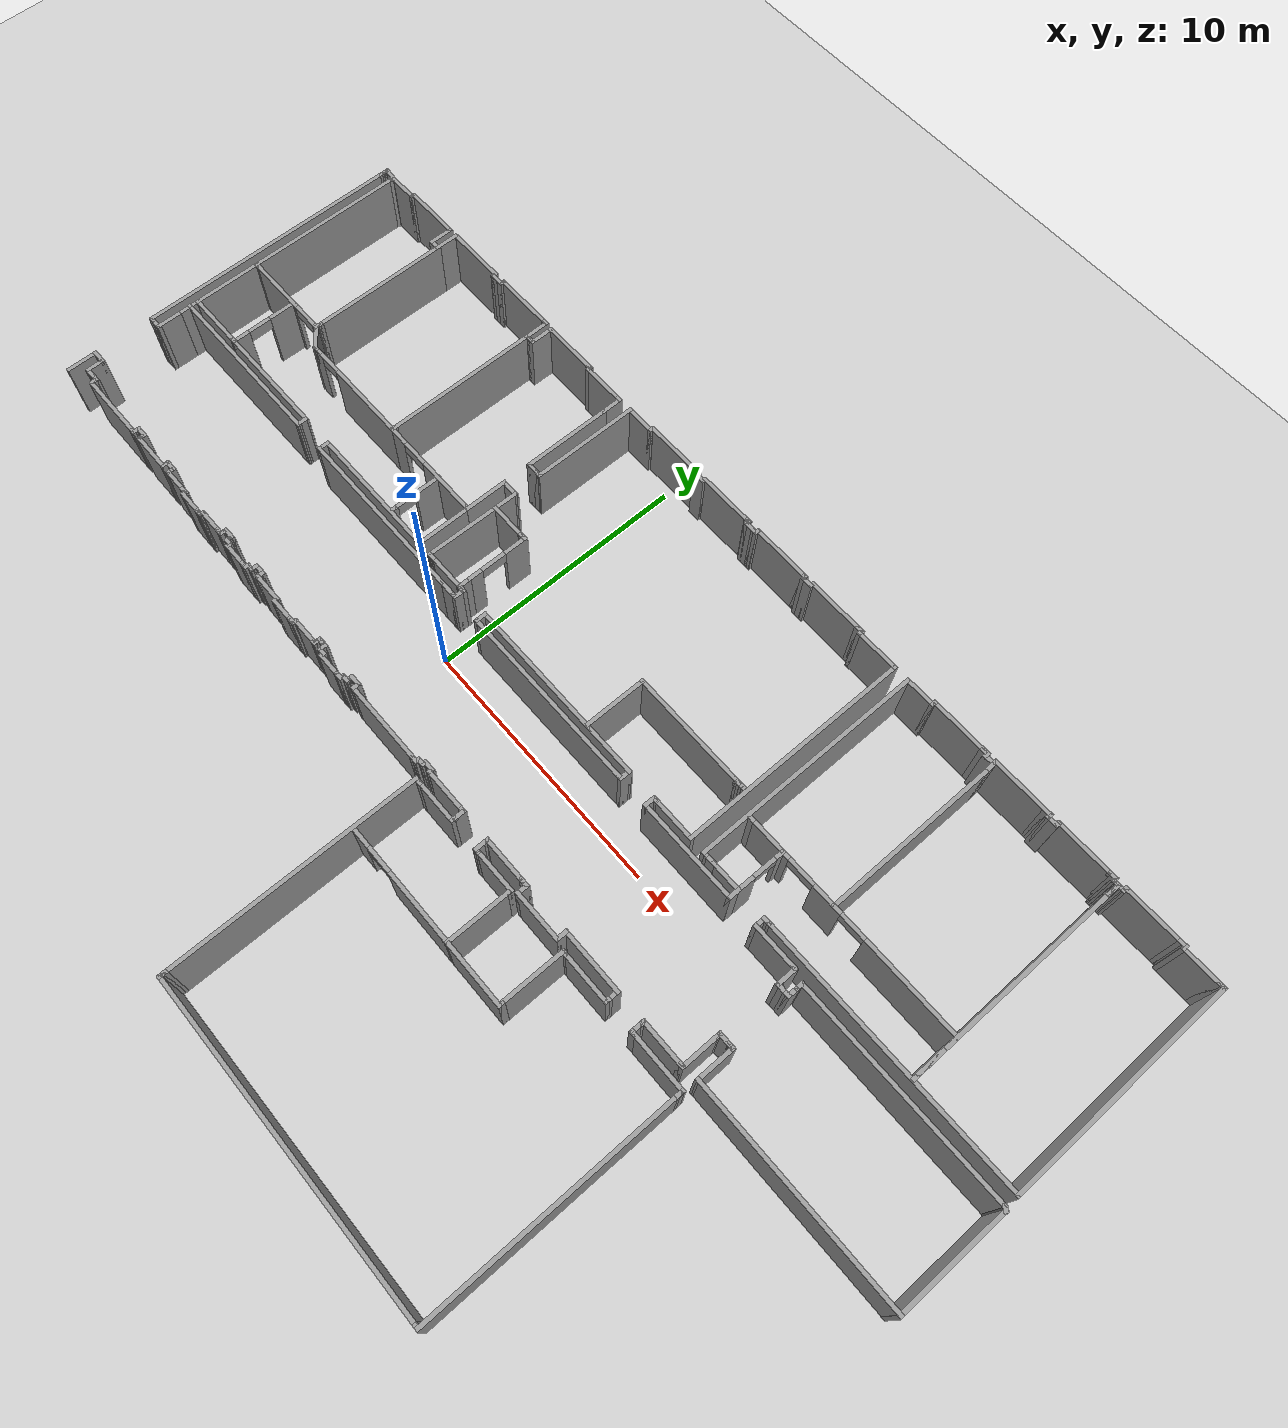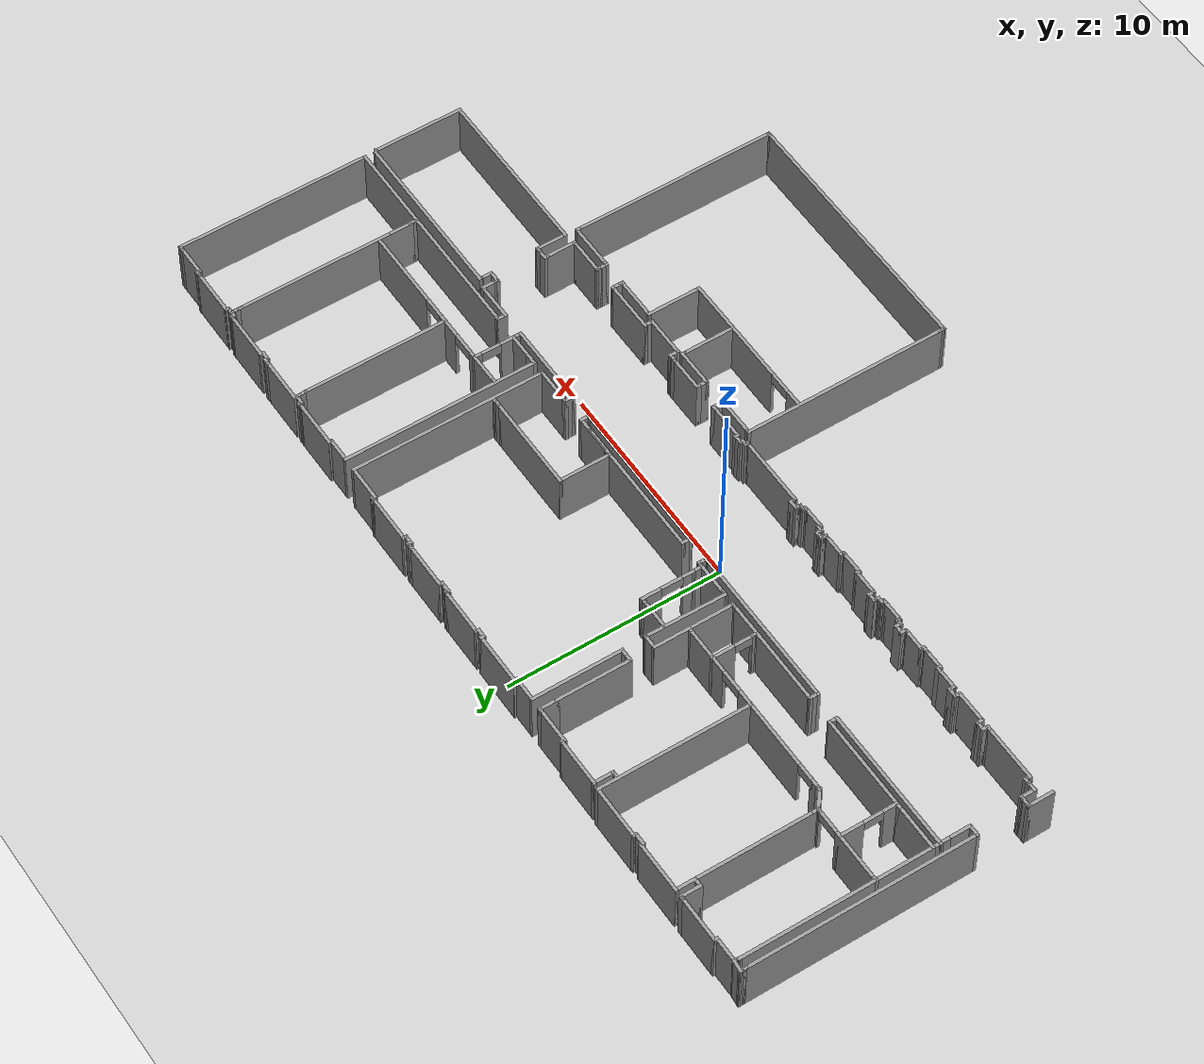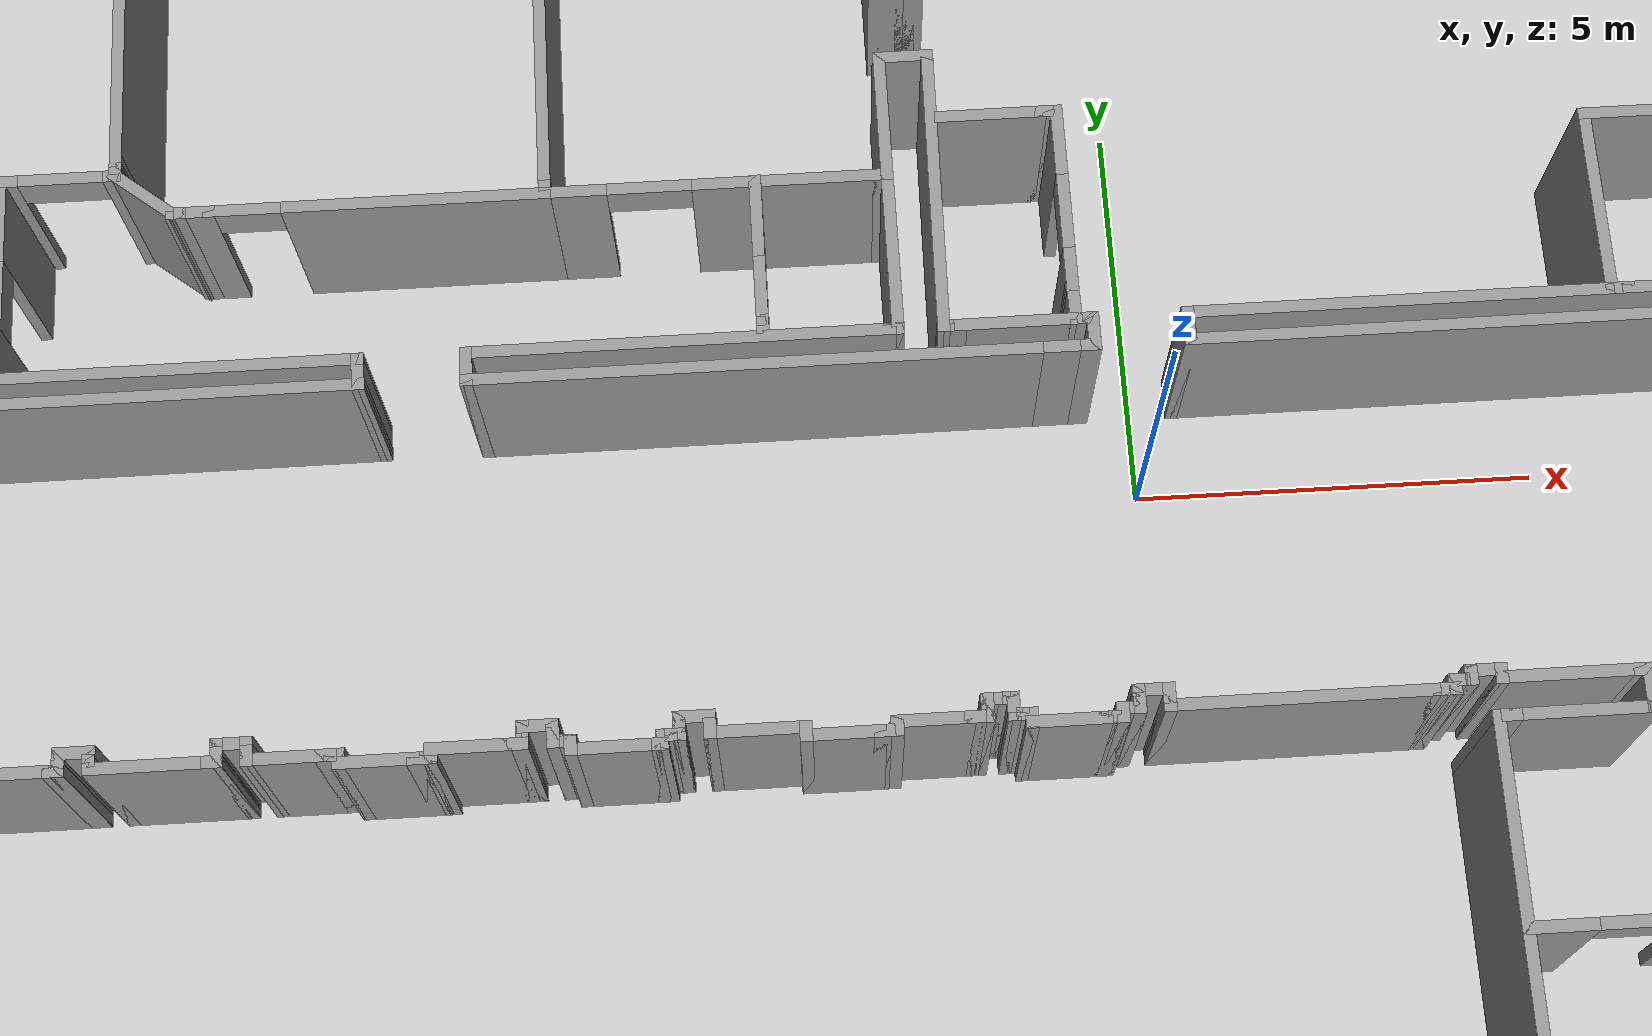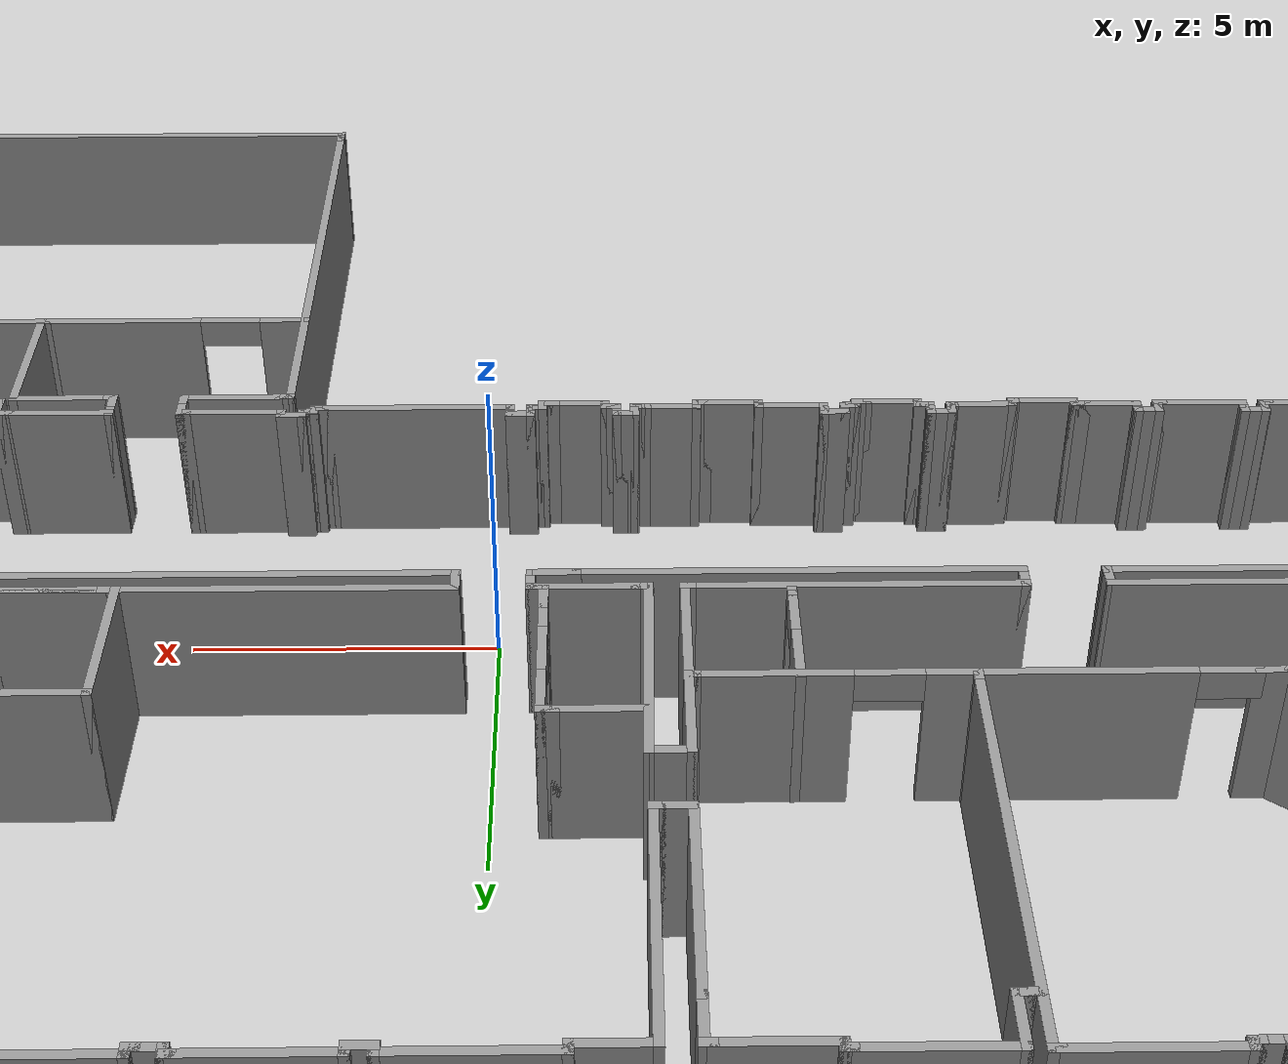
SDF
<sdf version="1.6">
 <world name="default">
  <light name="sun" type="directional">
   <pose>0 0 10 0 -0 0</pose>
   <diffuse>0.8 0.8 0.8 1</diffuse>
   <specular>0.1 0.1 0.1 1</specular>
   <attenuation>
    <range>1000</range>
    <constant>0.9</constant>
    <linear>0.01</linear>
    <quadratic>0.001</quadratic>
   </attenuation>
   <direction>-0.5 0.5 -1</direction>
  </light>
  <model name="ground_plane">
   <static>1</static>
   <link name="link">
    <collision name="collision">
     <geometry><plane><normal>0 0 1</normal><size>100 100</size></plane></geometry>
     <surface><friction><ode><mu>100</mu><mu2>50</mu2></ode></friction></surface>
    </collision>
    <visual name="visual">
     <cast_shadows>0</cast_shadows>
     <geometry><plane><normal>0 0 1</normal><size>100 100</size></plane></geometry>
     <material>
      <script><uri>file://media/materials/scripts/gazebo.material</uri><name>Gazebo/Grey</name></script>
     </material>
    </visual>
   </link>
  </model>
  <gravity>0 0 -9.8</gravity>
  <magnetic_field>6e-06 2.3e-05 -4.2e-05</magnetic_field>
  <atmosphere type="adiabatic"/>
  <physics name="default_physics" default="0" type="ode">
   <max_step_size>0.001</max_step_size>
   <real_time_factor>1</real_time_factor>
   <real_time_update_rate>1000</real_time_update_rate>
  </physics>
  <scene><ambient>0.4 0.4 0.4 1</ambient><background>0.7 0.7 0.7 1</background><shadows>1</shadows></scene>
  <spherical_coordinates>
   <surface_model>EARTH_WGS84</surface_model>
   <latitude_deg>0</latitude_deg>
   <longitude_deg>0</longitude_deg>
   <elevation>0</elevation>
   <heading_deg>0</heading_deg>
  </spherical_coordinates>
  <model name="office_full">
   <pose>3.85288 -1.38044 0 0 -0 0</pose>
   <link name="Wall_101">
    <collision name="Wall_101_Collision">
     <geometry><box><size>4.5 0.15 2.5</size></box></geometry>
     <pose>0 0 1.25 0 -0 0</pose>
    </collision>
    <visual name="Wall_101_Visual">
     <pose>0 0 1.25 0 -0 0</pose>
     <geometry><box><size>4.5 0.15 2.5</size></box></geometry>
     <material>
      <script><uri>file://media/materials/scripts/gazebo.material</uri><name>Gazebo/Grey</name></script>
      <ambient>1 1 1 1</ambient>
     </material>
    </visual>
    <pose>-15.4793 2.88121 0 0 -0 0</pose>
   </link>
   <link name="Wall_108">
    <collision name="Wall_108_Collision">
     <geometry><box><size>0.15 0.15 2.5</size></box></geometry>
     <pose>0 0 1.25 0 -0 0</pose>
    </collision>
    <visual name="Wall_108_Visual">
     <pose>0 0 1.25 0 -0 0</pose>
     <geometry><box><size>0.15 0.15 2.5</size></box></geometry>
     <material>
      <script><uri>file://media/materials/scripts/gazebo.material</uri><name>Gazebo/Grey</name></script>
      <ambient>1 1 1 1</ambient>
     </material>
    </visual>
    <pose>-19.9811 2.5471 0 0 -0 0</pose>
   </link>
   <link name="Wall_114">
    <collision name="Wall_114_Collision">
     <geometry><box><size>1 0.15 2.5</size></box></geometry>
     <pose>0 0 1.25 0 -0 0</pose>
    </collision>
    <visual name="Wall_114_Visual">
     <pose>0 0 1.25 0 -0 0</pose>
     <geometry><box><size>1 0.15 2.5</size></box></geometry>
     <material>
      <script><uri>file://media/materials/scripts/gazebo.material</uri><name>Gazebo/Grey</name></script>
      <ambient>1 1 1 1</ambient>
     </material>
    </visual>
    <pose>-19.9543 2.45621 0 0 0 -1.5708</pose>
   </link>
   <link name="Wall_117">
    <collision name="Wall_117_Collision">
     <geometry><box><size>6.83579 0.15 2.5</size></box></geometry>
     <pose>0 0 1.25 0 -0 0</pose>
    </collision>
    <visual name="Wall_117_Visual">
     <pose>0 0 1.25 0 -0 0</pose>
     <geometry><box><size>6.83579 0.15 2.5</size></box></geometry>
     <material>
      <script><uri>file://media/materials/scripts/gazebo.material</uri><name>Gazebo/Grey</name></script>
      <ambient>1 1 1 1</ambient>
     </material>
    </visual>
    <pose>-16.6382 2.55421 0 0 0 -3.14032</pose>
   </link>
   <link name="Wall_122">
    <collision name="Wall_122_Collision">
     <geometry><box><size>0.5 0.15 2.5</size></box></geometry>
     <pose>0 0 1.25 0 -0 0</pose>
    </collision>
    <visual name="Wall_122_Visual">
     <pose>0 0 1.25 0 -0 0</pose>
     <geometry><box><size>0.5 0.15 2.5</size></box></geometry>
     <material>
      <script><uri>file://media/materials/scripts/gazebo.material</uri><name>Gazebo/Grey</name></script>
      <ambient>1 1 1 1</ambient>
     </material>
    </visual>
    <pose>-12.0043 2.70621 0 0 0 -1.5708</pose>
   </link>
   <link name="Wall_124">
    <collision name="Wall_124_Collision">
     <geometry><box><size>5.25 0.15 2.5</size></box></geometry>
     <pose>0 0 1.25 0 -0 0</pose>
    </collision>
    <visual name="Wall_124_Visual">
     <pose>0 0 1.25 0 -0 0</pose>
     <geometry><box><size>5.25 0.15 2.5</size></box></geometry>
     <material>
      <script><uri>file://media/materials/scripts/gazebo.material</uri><name>Gazebo/Grey</name></script>
      <ambient>1 1 1 1</ambient>
     </material>
    </visual>
    <pose>-9.45432 2.88121 0 0 -0 0</pose>
   </link>
   <link name="Wall_125">
    <collision name="Wall_125_Collision">
     <geometry><box><size>0.25 0.15 2.5</size></box></geometry>
     <pose>0 0 1.25 0 -0 0</pose>
    </collision>
    <visual name="Wall_125_Visual">
     <pose>0 0 1.25 0 -0 0</pose>
     <geometry><box><size>0.25 0.15 2.5</size></box></geometry>
     <material>
      <script><uri>file://media/materials/scripts/gazebo.material</uri><name>Gazebo/Grey</name></script>
      <ambient>1 1 1 1</ambient>
     </material>
    </visual>
    <pose>-6.85432 2.88121 0 0 -0 0</pose>
   </link>
   <link name="Wall_126">
    <collision name="Wall_126_Collision">
     <geometry><box><size>2.2 0.15 2.5</size></box></geometry>
     <pose>0 0 1.25 0 -0 0</pose>
    </collision>
    <visual name="Wall_126_Visual">
     <pose>0 0 1.25 0 -0 0</pose>
     <geometry><box><size>2.2 0.15 2.5</size></box></geometry>
     <material>
      <script><uri>file://media/materials/scripts/gazebo.material</uri><name>Gazebo/Grey</name></script>
      <ambient>1 1 1 1</ambient>
     </material>
    </visual>
    <pose>-6.80432 3.90621 0 0 -0 1.5708</pose>
   </link>
   <link name="Wall_128">
    <pose>-8.4283 4.01499 0 0 0 -1.5708</pose>
    <visual name="Wall_128_Visual_0">
     <pose>-0.459037 0 1.25 0 -0 0</pose>
     <geometry><box><size>1.08193 0.15 2.5</size></box></geometry>
     <material>
      <script><uri>file://media/materials/scripts/gazebo.material</uri><name>Gazebo/Grey</name></script>
      <ambient>1 1 1 1</ambient>
     </material>
    </visual>
    <collision name="Wall_128_Collision_0">
     <geometry><box><size>1.08193 0.15 2.5</size></box></geometry>
     <pose>-0.459037 0 1.25 0 -0 0</pose>
    </collision>
    <visual name="Wall_128_Visual_1">
     <pose>0.93879 0 1.25 0 -0 0</pose>
     <geometry><box><size>0.122421 0.15 2.5</size></box></geometry>
     <material>
      <script><uri>file://media/materials/scripts/gazebo.material</uri><name>Gazebo/Grey</name></script>
      <ambient>1 1 1 1</ambient>
     </material>
    </visual>
    <collision name="Wall_128_Collision_1">
     <geometry><box><size>0.122421 0.15 2.5</size></box></geometry>
     <pose>0.93879 0 1.25 0 -0 0</pose>
    </collision>
    <visual name="Wall_128_Visual_2">
     <pose>0.479753 0 2.25 0 -0 0</pose>
     <geometry><box><size>0.795652 0.15 0.5</size></box></geometry>
     <material>
      <script><uri>file://media/materials/scripts/gazebo.material</uri><name>Gazebo/Grey</name></script>
      <ambient>1 1 1 1</ambient>
     </material>
    </visual>
    <collision name="Wall_128_Collision_2">
     <geometry><box><size>0.795652 0.15 0.5</size></box></geometry>
     <pose>0.479753 0 2.25 0 -0 0</pose>
    </collision>
   </link>
   <link name="Wall_129">
    <collision name="Wall_129_Collision">
     <geometry><box><size>0.25 0.15 2.5</size></box></geometry>
     <pose>0 0 1.25 0 -0 0</pose>
    </collision>
    <visual name="Wall_129_Visual">
     <pose>0 0 1.25 0 -0 0</pose>
     <geometry><box><size>0.25 0.15 2.5</size></box></geometry>
     <material>
      <script><uri>file://media/materials/scripts/gazebo.material</uri><name>Gazebo/Grey</name></script>
      <ambient>1 1 1 1</ambient>
     </material>
    </visual>
    <pose>-8.4283 3.03999 0 0 0 -1.5708</pose>
   </link>
   <link name="Wall_131">
    <collision name="Wall_131_Collision">
     <geometry><box><size>7 0.15 2.5</size></box></geometry>
     <pose>0 0 1.25 0 -0 0</pose>
    </collision>
    <visual name="Wall_131_Visual">
     <pose>0 0 1.25 0 -0 0</pose>
     <geometry><box><size>7 0.15 2.5</size></box></geometry>
     <material>
      <script><uri>file://media/materials/scripts/gazebo.material</uri><name>Gazebo/Grey</name></script>
      <ambient>1 1 1 1</ambient>
     </material>
    </visual>
    <pose>-8.57932 2.53121 0 0 -0 0</pose>
   </link>
   <link name="Wall_140">
    <collision name="Wall_140_Collision">
     <geometry><box><size>0.472867 0.15 2.5</size></box></geometry>
     <pose>0 0 1.25 0 -0 0</pose>
    </collision>
    <visual name="Wall_140_Visual">
     <pose>0 0 1.25 0 -0 0</pose>
     <geometry><box><size>0.472867 0.15 2.5</size></box></geometry>
     <material>
      <script><uri>file://media/materials/scripts/gazebo.material</uri><name>Gazebo/Grey</name></script>
      <ambient>1 1 1 1</ambient>
     </material>
    </visual>
    <pose>-13.2998 2.71984 0 0 0 -1.54281</pose>
   </link>
   <link name="Wall_143">
    <collision name="Wall_143_Collision">
     <geometry><box><size>1 0.15 2.5</size></box></geometry>
     <pose>0 0 1.25 0 -0 0</pose>
    </collision>
    <visual name="Wall_143_Visual">
     <pose>0 0 1.25 0 -0 0</pose>
     <geometry><box><size>1 0.15 2.5</size></box></geometry>
     <material>
      <script><uri>file://media/materials/scripts/gazebo.material</uri><name>Gazebo/Grey</name></script>
      <ambient>1 1 1 1</ambient>
     </material>
    </visual>
    <pose>-19.9543 1.60621 0 0 0 -1.5708</pose>
   </link>
   <link name="Wall_144">
    <collision name="Wall_144_Collision">
     <geometry><box><size>0.5 0.15 2.5</size></box></geometry>
     <pose>0 0 1.25 0 -0 0</pose>
    </collision>
    <visual name="Wall_144_Visual">
     <pose>0 0 1.25 0 -0 0</pose>
     <geometry><box><size>0.5 0.15 2.5</size></box></geometry>
     <material>
      <script><uri>file://media/materials/scripts/gazebo.material</uri><name>Gazebo/Grey</name></script>
      <ambient>1 1 1 1</ambient>
     </material>
    </visual>
    <pose>-20.1293 1.18121 0 0 -0 3.14159</pose>
   </link>
   <link name="Wall_145">
    <collision name="Wall_145_Collision">
     <geometry><box><size>0.25 0.15 2.5</size></box></geometry>
     <pose>0 0 1.25 0 -0 0</pose>
    </collision>
    <visual name="Wall_145_Visual">
     <pose>0 0 1.25 0 -0 0</pose>
     <geometry><box><size>0.25 0.15 2.5</size></box></geometry>
     <material>
      <script><uri>file://media/materials/scripts/gazebo.material</uri><name>Gazebo/Grey</name></script>
      <ambient>1 1 1 1</ambient>
     </material>
    </visual>
    <pose>-20.3543 1.18121 0 0 -0 3.14159</pose>
   </link>
   <link name="Wall_146">
    <collision name="Wall_146_Collision">
     <geometry><box><size>10.5 0.15 2.5</size></box></geometry>
     <pose>0 0 1.25 0 -0 0</pose>
    </collision>
    <visual name="Wall_146_Visual">
     <pose>0 0 1.25 0 -0 0</pose>
     <geometry><box><size>10.5 0.15 2.5</size></box></geometry>
     <material>
      <script><uri>file://media/materials/scripts/gazebo.material</uri><name>Gazebo/Grey</name></script>
      <ambient>1 1 1 1</ambient>
     </material>
    </visual>
    <pose>-20.4043 6.35621 0 0 -0 1.5708</pose>
   </link>
   <link name="Wall_147">
    <collision name="Wall_147_Collision">
     <geometry><box><size>0.25 0.15 2.5</size></box></geometry>
     <pose>0 0 1.25 0 -0 0</pose>
    </collision>
    <visual name="Wall_147_Visual">
     <pose>0 0 1.25 0 -0 0</pose>
     <geometry><box><size>0.25 0.15 2.5</size></box></geometry>
     <material>
      <script><uri>file://media/materials/scripts/gazebo.material</uri><name>Gazebo/Grey</name></script>
      <ambient>1 1 1 1</ambient>
     </material>
    </visual>
    <pose>-20.4043 11.5812 0 0 -0 1.5708</pose>
   </link>
   <link name="Wall_148">
    <collision name="Wall_148_Collision">
     <geometry><box><size>0.25 0.15 2.5</size></box></geometry>
     <pose>0 0 1.25 0 -0 0</pose>
    </collision>
    <visual name="Wall_148_Visual">
     <pose>0 0 1.25 0 -0 0</pose>
     <geometry><box><size>0.25 0.15 2.5</size></box></geometry>
     <material>
      <script><uri>file://media/materials/scripts/gazebo.material</uri><name>Gazebo/Grey</name></script>
      <ambient>1 1 1 1</ambient>
     </material>
    </visual>
    <pose>-20.4043 11.6812 0 0 -0 1.5708</pose>
   </link>
   <link name="Wall_149">
    <collision name="Wall_149_Collision">
     <geometry><box><size>0.25 0.15 2.5</size></box></geometry>
     <pose>0 0 1.25 0 -0 0</pose>
    </collision>
    <visual name="Wall_149_Visual">
     <pose>0 0 1.25 0 -0 0</pose>
     <geometry><box><size>0.25 0.15 2.5</size></box></geometry>
     <material>
      <script><uri>file://media/materials/scripts/gazebo.material</uri><name>Gazebo/Grey</name></script>
      <ambient>1 1 1 1</ambient>
     </material>
    </visual>
    <pose>-20.4043 11.6812 0 0 0 -1.5708</pose>
   </link>
   <link name="Wall_150">
    <collision name="Wall_150_Collision">
     <geometry><box><size>0.25 0.15 2.5</size></box></geometry>
     <pose>0 0 1.25 0 -0 0</pose>
    </collision>
    <visual name="Wall_150_Visual">
     <pose>0 0 1.25 0 -0 0</pose>
     <geometry><box><size>0.25 0.15 2.5</size></box></geometry>
     <material>
      <script><uri>file://media/materials/scripts/gazebo.material</uri><name>Gazebo/Grey</name></script>
      <ambient>1 1 1 1</ambient>
     </material>
    </visual>
    <pose>-20.4043 11.6812 0 0 -0 1.5708</pose>
   </link>
   <link name="Wall_151">
    <collision name="Wall_151_Collision">
     <geometry><box><size>0.25 0.15 2.5</size></box></geometry>
     <pose>0 0 1.25 0 -0 0</pose>
    </collision>
    <visual name="Wall_151_Visual">
     <pose>0 0 1.25 0 -0 0</pose>
     <geometry><box><size>0.25 0.15 2.5</size></box></geometry>
     <material>
      <script><uri>file://media/materials/scripts/gazebo.material</uri><name>Gazebo/Grey</name></script>
      <ambient>1 1 1 1</ambient>
     </material>
    </visual>
    <pose>-20.4043 11.7812 0 0 -0 1.5708</pose>
   </link>
   <link name="Wall_152">
    <collision name="Wall_152_Collision">
     <geometry><box><size>0.652494 0.15 2.5</size></box></geometry>
     <pose>0 0 1.25 0 -0 0</pose>
    </collision>
    <visual name="Wall_152_Visual">
     <pose>0 0 1.25 0 -0 0</pose>
     <geometry><box><size>0.652494 0.15 2.5</size></box></geometry>
     <material>
      <script><uri>file://media/materials/scripts/gazebo.material</uri><name>Gazebo/Grey</name></script>
      <ambient>1 1 1 1</ambient>
     </material>
    </visual>
    <pose>-20.1543 11.8062 0 0 0 -0.099669</pose>
   </link>
   <link name="Wall_154">
    <collision name="Wall_154_Collision">
     <geometry><box><size>1.25 0.15 2.5</size></box></geometry>
     <pose>0 0 1.25 0 -0 0</pose>
    </collision>
    <visual name="Wall_154_Visual">
     <pose>0 0 1.25 0 -0 0</pose>
     <geometry><box><size>1.25 0.15 2.5</size></box></geometry>
     <material>
      <script><uri>file://media/materials/scripts/gazebo.material</uri><name>Gazebo/Grey</name></script>
      <ambient>1 1 1 1</ambient>
     </material>
    </visual>
    <pose>-20.4403 -1.73121 0 0 -0 1.5708</pose>
   </link>
   <link name="Wall_155">
    <collision name="Wall_155_Collision">
     <geometry><box><size>0.5 0.15 2.5</size></box></geometry>
     <pose>0 0 1.25 0 -0 0</pose>
    </collision>
    <visual name="Wall_155_Visual">
     <pose>0 0 1.25 0 -0 0</pose>
     <geometry><box><size>0.5 0.15 2.5</size></box></geometry>
     <material>
      <script><uri>file://media/materials/scripts/gazebo.material</uri><name>Gazebo/Grey</name></script>
      <ambient>1 1 1 1</ambient>
     </material>
    </visual>
    <pose>-20.2653 -1.18121 0 0 -0 0</pose>
   </link>
   <link name="Wall_156">
    <collision name="Wall_156_Collision">
     <geometry><box><size>0.25 0.15 2.5</size></box></geometry>
     <pose>0 0 1.25 0 -0 0</pose>
    </collision>
    <visual name="Wall_156_Visual">
     <pose>0 0 1.25 0 -0 0</pose>
     <geometry><box><size>0.25 0.15 2.5</size></box></geometry>
     <material>
      <script><uri>file://media/materials/scripts/gazebo.material</uri><name>Gazebo/Grey</name></script>
      <ambient>1 1 1 1</ambient>
     </material>
    </visual>
    <pose>-20.0403 -1.18121 0 0 -0 0</pose>
   </link>
   <link name="Wall_157">
    <collision name="Wall_157_Collision">
     <geometry><box><size>0.75 0.15 2.5</size></box></geometry>
     <pose>0 0 1.25 0 -0 0</pose>
    </collision>
    <visual name="Wall_157_Visual">
     <pose>0 0 1.25 0 -0 0</pose>
     <geometry><box><size>0.75 0.15 2.5</size></box></geometry>
     <material>
      <script><uri>file://media/materials/scripts/gazebo.material</uri><name>Gazebo/Grey</name></script>
      <ambient>1 1 1 1</ambient>
     </material>
    </visual>
    <pose>-19.9903 -1.48121 0 0 0 -1.5708</pose>
   </link>
   <link name="Wall_158">
    <collision name="Wall_158_Collision">
     <geometry><box><size>0.5 0.15 2.5</size></box></geometry>
     <pose>0 0 1.25 0 -0 0</pose>
    </collision>
    <visual name="Wall_158_Visual">
     <pose>0 0 1.25 0 -0 0</pose>
     <geometry><box><size>0.5 0.15 2.5</size></box></geometry>
     <material>
      <script><uri>file://media/materials/scripts/gazebo.material</uri><name>Gazebo/Grey</name></script>
      <ambient>1 1 1 1</ambient>
     </material>
    </visual>
    <pose>-19.8153 -1.78121 0 0 -0 0</pose>
   </link>
   <link name="Wall_159">
    <collision name="Wall_159_Collision">
     <geometry><box><size>0.25 0.15 2.5</size></box></geometry>
     <pose>0 0 1.25 0 -0 0</pose>
    </collision>
    <visual name="Wall_159_Visual">
     <pose>0 0 1.25 0 -0 0</pose>
     <geometry><box><size>0.25 0.15 2.5</size></box></geometry>
     <material>
      <script><uri>file://media/materials/scripts/gazebo.material</uri><name>Gazebo/Grey</name></script>
      <ambient>1 1 1 1</ambient>
     </material>
    </visual>
    <pose>-19.5903 -1.78121 0 0 -0 0</pose>
   </link>
   <link name="Wall_160">
    <collision name="Wall_160_Collision">
     <geometry><box><size>0.25 0.15 2.5</size></box></geometry>
     <pose>0 0 1.25 0 -0 0</pose>
    </collision>
    <visual name="Wall_160_Visual">
     <pose>0 0 1.25 0 -0 0</pose>
     <geometry><box><size>0.25 0.15 2.5</size></box></geometry>
     <material>
      <script><uri>file://media/materials/scripts/gazebo.material</uri><name>Gazebo/Grey</name></script>
      <ambient>1 1 1 1</ambient>
     </material>
    </visual>
    <pose>-19.4903 -1.78121 0 0 -0 0</pose>
   </link>
   <link name="Wall_161">
    <collision name="Wall_161_Collision">
     <geometry><box><size>0.25 0.15 2.5</size></box></geometry>
     <pose>0 0 1.25 0 -0 0</pose>
    </collision>
    <visual name="Wall_161_Visual">
     <pose>0 0 1.25 0 -0 0</pose>
     <geometry><box><size>0.25 0.15 2.5</size></box></geometry>
     <material>
      <script><uri>file://media/materials/scripts/gazebo.material</uri><name>Gazebo/Grey</name></script>
      <ambient>1 1 1 1</ambient>
     </material>
    </visual>
    <pose>-19.4403 -1.83121 0 0 0 -1.5708</pose>
   </link>
   <link name="Wall_162">
    <collision name="Wall_162_Collision">
     <geometry><box><size>0.25 0.15 2.5</size></box></geometry>
     <pose>0 0 1.25 0 -0 0</pose>
    </collision>
    <visual name="Wall_162_Visual">
     <pose>0 0 1.25 0 -0 0</pose>
     <geometry><box><size>0.25 0.15 2.5</size></box></geometry>
     <material>
      <script><uri>file://media/materials/scripts/gazebo.material</uri><name>Gazebo/Grey</name></script>
      <ambient>1 1 1 1</ambient>
     </material>
    </visual>
    <pose>-19.4403 -1.93121 0 0 0 -1.5708</pose>
   </link>
   <link name="Wall_163">
    <collision name="Wall_163_Collision">
     <geometry><box><size>2.75 0.15 2.5</size></box></geometry>
     <pose>0 0 1.25 0 -0 0</pose>
    </collision>
    <visual name="Wall_163_Visual">
     <pose>0 0 1.25 0 -0 0</pose>
     <geometry><box><size>2.75 0.15 2.5</size></box></geometry>
     <material>
      <script><uri>file://media/materials/scripts/gazebo.material</uri><name>Gazebo/Grey</name></script>
      <ambient>1 1 1 1</ambient>
     </material>
    </visual>
    <pose>-18.1403 -1.98121 0 0 -0 0</pose>
   </link>
   <link name="Wall_164">
    <collision name="Wall_164_Collision">
     <geometry><box><size>0.25 0.15 2.5</size></box></geometry>
     <pose>0 0 1.25 0 -0 0</pose>
    </collision>
    <visual name="Wall_164_Visual">
     <pose>0 0 1.25 0 -0 0</pose>
     <geometry><box><size>0.25 0.15 2.5</size></box></geometry>
     <material>
      <script><uri>file://media/materials/scripts/gazebo.material</uri><name>Gazebo/Grey</name></script>
      <ambient>1 1 1 1</ambient>
     </material>
    </visual>
    <pose>-16.7903 -1.98121 0 0 -0 0</pose>
   </link>
   <link name="Wall_165">
    <collision name="Wall_165_Collision">
     <geometry><box><size>0.25 0.15 2.5</size></box></geometry>
     <pose>0 0 1.25 0 -0 0</pose>
    </collision>
    <visual name="Wall_165_Visual">
     <pose>0 0 1.25 0 -0 0</pose>
     <geometry><box><size>0.25 0.15 2.5</size></box></geometry>
     <material>
      <script><uri>file://media/materials/scripts/gazebo.material</uri><name>Gazebo/Grey</name></script>
      <ambient>1 1 1 1</ambient>
     </material>
    </visual>
    <pose>-16.7403 -1.93121 0 0 -0 1.5708</pose>
   </link>
   <link name="Wall_166">
    <collision name="Wall_166_Collision">
     <geometry><box><size>0.25 0.15 2.5</size></box></geometry>
     <pose>0 0 1.25 0 -0 0</pose>
    </collision>
    <visual name="Wall_166_Visual">
     <pose>0 0 1.25 0 -0 0</pose>
     <geometry><box><size>0.25 0.15 2.5</size></box></geometry>
     <material>
      <script><uri>file://media/materials/scripts/gazebo.material</uri><name>Gazebo/Grey</name></script>
      <ambient>1 1 1 1</ambient>
     </material>
    </visual>
    <pose>-16.7403 -1.83121 0 0 -0 1.5708</pose>
   </link>
   <link name="Wall_167">
    <collision name="Wall_167_Collision">
     <geometry><box><size>0.5 0.15 2.5</size></box></geometry>
     <pose>0 0 1.25 0 -0 0</pose>
    </collision>
    <visual name="Wall_167_Visual">
     <pose>0 0 1.25 0 -0 0</pose>
     <geometry><box><size>0.5 0.15 2.5</size></box></geometry>
     <material>
      <script><uri>file://media/materials/scripts/gazebo.material</uri><name>Gazebo/Grey</name></script>
      <ambient>1 1 1 1</ambient>
     </material>
    </visual>
    <pose>-16.5653 -1.78121 0 0 -0 0</pose>
   </link>
   <link name="Wall_168">
    <collision name="Wall_168_Collision">
     <geometry><box><size>0.25 0.15 2.5</size></box></geometry>
     <pose>0 0 1.25 0 -0 0</pose>
    </collision>
    <visual name="Wall_168_Visual">
     <pose>0 0 1.25 0 -0 0</pose>
     <geometry><box><size>0.25 0.15 2.5</size></box></geometry>
     <material>
      <script><uri>file://media/materials/scripts/gazebo.material</uri><name>Gazebo/Grey</name></script>
      <ambient>1 1 1 1</ambient>
     </material>
    </visual>
    <pose>-16.3903 -1.83121 0 0 0 -1.5708</pose>
   </link>
   <link name="Wall_169">
    <collision name="Wall_169_Collision">
     <geometry><box><size>0.25 0.15 2.5</size></box></geometry>
     <pose>0 0 1.25 0 -0 0</pose>
    </collision>
    <visual name="Wall_169_Visual">
     <pose>0 0 1.25 0 -0 0</pose>
     <geometry><box><size>0.25 0.15 2.5</size></box></geometry>
     <material>
      <script><uri>file://media/materials/scripts/gazebo.material</uri><name>Gazebo/Grey</name></script>
      <ambient>1 1 1 1</ambient>
     </material>
    </visual>
    <pose>-16.3903 -1.93121 0 0 0 -1.5708</pose>
   </link>
   <link name="Wall_170">
    <collision name="Wall_170_Collision">
     <geometry><box><size>1.5 0.15 2.5</size></box></geometry>
     <pose>0 0 1.25 0 -0 0</pose>
    </collision>
    <visual name="Wall_170_Visual">
     <pose>0 0 1.25 0 -0 0</pose>
     <geometry><box><size>1.5 0.15 2.5</size></box></geometry>
     <material>
      <script><uri>file://media/materials/scripts/gazebo.material</uri><name>Gazebo/Grey</name></script>
      <ambient>1 1 1 1</ambient>
     </material>
    </visual>
    <pose>-15.7153 -1.98121 0 0 -0 0</pose>
   </link>
   <link name="Wall_171">
    <collision name="Wall_171_Collision">
     <geometry><box><size>0.25 0.15 2.5</size></box></geometry>
     <pose>0 0 1.25 0 -0 0</pose>
    </collision>
    <visual name="Wall_171_Visual">
     <pose>0 0 1.25 0 -0 0</pose>
     <geometry><box><size>0.25 0.15 2.5</size></box></geometry>
     <material>
      <script><uri>file://media/materials/scripts/gazebo.material</uri><name>Gazebo/Grey</name></script>
      <ambient>1 1 1 1</ambient>
     </material>
    </visual>
    <pose>-14.9903 -1.98121 0 0 -0 0</pose>
   </link>
   <link name="Wall_172">
    <collision name="Wall_172_Collision">
     <geometry><box><size>0.25 0.15 2.5</size></box></geometry>
     <pose>0 0 1.25 0 -0 0</pose>
    </collision>
    <visual name="Wall_172_Visual">
     <pose>0 0 1.25 0 -0 0</pose>
     <geometry><box><size>0.25 0.15 2.5</size></box></geometry>
     <material>
      <script><uri>file://media/materials/scripts/gazebo.material</uri><name>Gazebo/Grey</name></script>
      <ambient>1 1 1 1</ambient>
     </material>
    </visual>
    <pose>-14.9403 -1.93121 0 0 -0 1.5708</pose>
   </link>
   <link name="Wall_173">
    <collision name="Wall_173_Collision">
     <geometry><box><size>0.25 0.15 2.5</size></box></geometry>
     <pose>0 0 1.25 0 -0 0</pose>
    </collision>
    <visual name="Wall_173_Visual">
     <pose>0 0 1.25 0 -0 0</pose>
     <geometry><box><size>0.25 0.15 2.5</size></box></geometry>
     <material>
      <script><uri>file://media/materials/scripts/gazebo.material</uri><name>Gazebo/Grey</name></script>
      <ambient>1 1 1 1</ambient>
     </material>
    </visual>
    <pose>-14.9403 -1.83121 0 0 -0 1.5708</pose>
   </link>
   <link name="Wall_174">
    <collision name="Wall_174_Collision">
     <geometry><box><size>0.5 0.15 2.5</size></box></geometry>
     <pose>0 0 1.25 0 -0 0</pose>
    </collision>
    <visual name="Wall_174_Visual">
     <pose>0 0 1.25 0 -0 0</pose>
     <geometry><box><size>0.5 0.15 2.5</size></box></geometry>
     <material>
      <script><uri>file://media/materials/scripts/gazebo.material</uri><name>Gazebo/Grey</name></script>
      <ambient>1 1 1 1</ambient>
     </material>
    </visual>
    <pose>-14.7653 -1.78121 0 0 -0 0</pose>
   </link>
   <link name="Wall_175">
    <collision name="Wall_175_Collision">
     <geometry><box><size>0.25 0.15 2.5</size></box></geometry>
     <pose>0 0 1.25 0 -0 0</pose>
    </collision>
    <visual name="Wall_175_Visual">
     <pose>0 0 1.25 0 -0 0</pose>
     <geometry><box><size>0.25 0.15 2.5</size></box></geometry>
     <material>
      <script><uri>file://media/materials/scripts/gazebo.material</uri><name>Gazebo/Grey</name></script>
      <ambient>1 1 1 1</ambient>
     </material>
    </visual>
    <pose>-14.5903 -1.83121 0 0 0 -1.5708</pose>
   </link>
   <link name="Wall_176">
    <collision name="Wall_176_Collision">
     <geometry><box><size>0.25 0.15 2.5</size></box></geometry>
     <pose>0 0 1.25 0 -0 0</pose>
    </collision>
    <visual name="Wall_176_Visual">
     <pose>0 0 1.25 0 -0 0</pose>
     <geometry><box><size>0.25 0.15 2.5</size></box></geometry>
     <material>
      <script><uri>file://media/materials/scripts/gazebo.material</uri><name>Gazebo/Grey</name></script>
      <ambient>1 1 1 1</ambient>
     </material>
    </visual>
    <pose>-14.5903 -1.93121 0 0 0 -1.5708</pose>
   </link>
   <link name="Wall_177">
    <collision name="Wall_177_Collision">
     <geometry><box><size>1 0.15 2.5</size></box></geometry>
     <pose>0 0 1.25 0 -0 0</pose>
    </collision>
    <visual name="Wall_177_Visual">
     <pose>0 0 1.25 0 -0 0</pose>
     <geometry><box><size>1 0.15 2.5</size></box></geometry>
     <material>
      <script><uri>file://media/materials/scripts/gazebo.material</uri><name>Gazebo/Grey</name></script>
      <ambient>1 1 1 1</ambient>
     </material>
    </visual>
    <pose>-14.1653 -1.98121 0 0 -0 0</pose>
   </link>
   <link name="Wall_178">
    <collision name="Wall_178_Collision">
     <geometry><box><size>0.25 0.15 2.5</size></box></geometry>
     <pose>0 0 1.25 0 -0 0</pose>
    </collision>
    <visual name="Wall_178_Visual">
     <pose>0 0 1.25 0 -0 0</pose>
     <geometry><box><size>0.25 0.15 2.5</size></box></geometry>
     <material>
      <script><uri>file://media/materials/scripts/gazebo.material</uri><name>Gazebo/Grey</name></script>
      <ambient>1 1 1 1</ambient>
     </material>
    </visual>
    <pose>-13.6903 -1.98121 0 0 -0 0</pose>
   </link>
   <link name="Wall_179">
    <collision name="Wall_179_Collision">
     <geometry><box><size>0.25 0.15 2.5</size></box></geometry>
     <pose>0 0 1.25 0 -0 0</pose>
    </collision>
    <visual name="Wall_179_Visual">
     <pose>0 0 1.25 0 -0 0</pose>
     <geometry><box><size>0.25 0.15 2.5</size></box></geometry>
     <material>
      <script><uri>file://media/materials/scripts/gazebo.material</uri><name>Gazebo/Grey</name></script>
      <ambient>1 1 1 1</ambient>
     </material>
    </visual>
    <pose>-13.5903 -1.98121 0 0 -0 0</pose>
   </link>
   <link name="Wall_180">
    <collision name="Wall_180_Collision">
     <geometry><box><size>0.25 0.15 2.5</size></box></geometry>
     <pose>0 0 1.25 0 -0 0</pose>
    </collision>
    <visual name="Wall_180_Visual">
     <pose>0 0 1.25 0 -0 0</pose>
     <geometry><box><size>0.25 0.15 2.5</size></box></geometry>
     <material>
      <script><uri>file://media/materials/scripts/gazebo.material</uri><name>Gazebo/Grey</name></script>
      <ambient>1 1 1 1</ambient>
     </material>
    </visual>
    <pose>-13.5403 -2.03121 0 0 0 -1.5708</pose>
   </link>
   <link name="Wall_181">
    <collision name="Wall_181_Collision">
     <geometry><box><size>1 0.15 2.5</size></box></geometry>
     <pose>0 0 1.25 0 -0 0</pose>
    </collision>
    <visual name="Wall_181_Visual">
     <pose>0 0 1.25 0 -0 0</pose>
     <geometry><box><size>1 0.15 2.5</size></box></geometry>
     <material>
      <script><uri>file://media/materials/scripts/gazebo.material</uri><name>Gazebo/Grey</name></script>
      <ambient>1 1 1 1</ambient>
     </material>
    </visual>
    <pose>-13.1153 -2.08121 0 0 -0 0</pose>
   </link>
   <link name="Wall_182">
    <collision name="Wall_182_Collision">
     <geometry><box><size>0.25 0.15 2.5</size></box></geometry>
     <pose>0 0 1.25 0 -0 0</pose>
    </collision>
    <visual name="Wall_182_Visual">
     <pose>0 0 1.25 0 -0 0</pose>
     <geometry><box><size>0.25 0.15 2.5</size></box></geometry>
     <material>
      <script><uri>file://media/materials/scripts/gazebo.material</uri><name>Gazebo/Grey</name></script>
      <ambient>1 1 1 1</ambient>
     </material>
    </visual>
    <pose>-12.6403 -2.08121 0 0 -0 0</pose>
   </link>
   <link name="Wall_183">
    <collision name="Wall_183_Collision">
     <geometry><box><size>0.25 0.15 2.5</size></box></geometry>
     <pose>0 0 1.25 0 -0 0</pose>
    </collision>
    <visual name="Wall_183_Visual">
     <pose>0 0 1.25 0 -0 0</pose>
     <geometry><box><size>0.25 0.15 2.5</size></box></geometry>
     <material>
      <script><uri>file://media/materials/scripts/gazebo.material</uri><name>Gazebo/Grey</name></script>
      <ambient>1 1 1 1</ambient>
     </material>
    </visual>
    <pose>-12.5403 -2.08121 0 0 -0 0</pose>
   </link>
   <link name="Wall_184">
    <collision name="Wall_184_Collision">
     <geometry><box><size>0.25 0.15 2.5</size></box></geometry>
     <pose>0 0 1.25 0 -0 0</pose>
    </collision>
    <visual name="Wall_184_Visual">
     <pose>0 0 1.25 0 -0 0</pose>
     <geometry><box><size>0.25 0.15 2.5</size></box></geometry>
     <material>
      <script><uri>file://media/materials/scripts/gazebo.material</uri><name>Gazebo/Grey</name></script>
      <ambient>1 1 1 1</ambient>
     </material>
    </visual>
    <pose>-12.4903 -2.03121 0 0 -0 1.5708</pose>
   </link>
   <link name="Wall_185">
    <collision name="Wall_185_Collision">
     <geometry><box><size>1 0.15 2.5</size></box></geometry>
     <pose>0 0 1.25 0 -0 0</pose>
    </collision>
    <visual name="Wall_185_Visual">
     <pose>0 0 1.25 0 -0 0</pose>
     <geometry><box><size>1 0.15 2.5</size></box></geometry>
     <material>
      <script><uri>file://media/materials/scripts/gazebo.material</uri><name>Gazebo/Grey</name></script>
      <ambient>1 1 1 1</ambient>
     </material>
    </visual>
    <pose>-12.0653 -1.98121 0 0 -0 0</pose>
   </link>
   <link name="Wall_186">
    <collision name="Wall_186_Collision">
     <geometry><box><size>0.25 0.15 2.5</size></box></geometry>
     <pose>0 0 1.25 0 -0 0</pose>
    </collision>
    <visual name="Wall_186_Visual">
     <pose>0 0 1.25 0 -0 0</pose>
     <geometry><box><size>0.25 0.15 2.5</size></box></geometry>
     <material>
      <script><uri>file://media/materials/scripts/gazebo.material</uri><name>Gazebo/Grey</name></script>
      <ambient>1 1 1 1</ambient>
     </material>
    </visual>
    <pose>-11.5903 -1.98121 0 0 -0 0</pose>
   </link>
   <link name="Wall_187">
    <collision name="Wall_187_Collision">
     <geometry><box><size>0.25 0.15 2.5</size></box></geometry>
     <pose>0 0 1.25 0 -0 0</pose>
    </collision>
    <visual name="Wall_187_Visual">
     <pose>0 0 1.25 0 -0 0</pose>
     <geometry><box><size>0.25 0.15 2.5</size></box></geometry>
     <material>
      <script><uri>file://media/materials/scripts/gazebo.material</uri><name>Gazebo/Grey</name></script>
      <ambient>1 1 1 1</ambient>
     </material>
    </visual>
    <pose>-11.4903 -1.98121 0 0 -0 0</pose>
   </link>
   <link name="Wall_188">
    <collision name="Wall_188_Collision">
     <geometry><box><size>0.25 0.15 2.5</size></box></geometry>
     <pose>0 0 1.25 0 -0 0</pose>
    </collision>
    <visual name="Wall_188_Visual">
     <pose>0 0 1.25 0 -0 0</pose>
     <geometry><box><size>0.25 0.15 2.5</size></box></geometry>
     <material>
      <script><uri>file://media/materials/scripts/gazebo.material</uri><name>Gazebo/Grey</name></script>
      <ambient>1 1 1 1</ambient>
     </material>
    </visual>
    <pose>-11.4403 -1.93121 0 0 -0 1.5708</pose>
   </link>
   <link name="Wall_189">
    <collision name="Wall_189_Collision">
     <geometry><box><size>0.25 0.15 2.5</size></box></geometry>
     <pose>0 0 1.25 0 -0 0</pose>
    </collision>
    <visual name="Wall_189_Visual">
     <pose>0 0 1.25 0 -0 0</pose>
     <geometry><box><size>0.25 0.15 2.5</size></box></geometry>
     <material>
      <script><uri>file://media/materials/scripts/gazebo.material</uri><name>Gazebo/Grey</name></script>
      <ambient>1 1 1 1</ambient>
     </material>
    </visual>
    <pose>-11.4403 -1.83121 0 0 -0 1.5708</pose>
   </link>
   <link name="Wall_190">
    <collision name="Wall_190_Collision">
     <geometry><box><size>0.5 0.15 2.5</size></box></geometry>
     <pose>0 0 1.25 0 -0 0</pose>
    </collision>
    <visual name="Wall_190_Visual">
     <pose>0 0 1.25 0 -0 0</pose>
     <geometry><box><size>0.5 0.15 2.5</size></box></geometry>
     <material>
      <script><uri>file://media/materials/scripts/gazebo.material</uri><name>Gazebo/Grey</name></script>
      <ambient>1 1 1 1</ambient>
     </material>
    </visual>
    <pose>-11.2653 -1.78121 0 0 -0 0</pose>
   </link>
   <link name="Wall_191">
    <collision name="Wall_191_Collision">
     <geometry><box><size>0.25 0.15 2.5</size></box></geometry>
     <pose>0 0 1.25 0 -0 0</pose>
    </collision>
    <visual name="Wall_191_Visual">
     <pose>0 0 1.25 0 -0 0</pose>
     <geometry><box><size>0.25 0.15 2.5</size></box></geometry>
     <material>
      <script><uri>file://media/materials/scripts/gazebo.material</uri><name>Gazebo/Grey</name></script>
      <ambient>1 1 1 1</ambient>
     </material>
    </visual>
    <pose>-11.0903 -1.83121 0 0 0 -1.5708</pose>
   </link>
   <link name="Wall_192">
    <collision name="Wall_192_Collision">
     <geometry><box><size>0.25 0.15 2.5</size></box></geometry>
     <pose>0 0 1.25 0 -0 0</pose>
    </collision>
    <visual name="Wall_192_Visual">
     <pose>0 0 1.25 0 -0 0</pose>
     <geometry><box><size>0.25 0.15 2.5</size></box></geometry>
     <material>
      <script><uri>file://media/materials/scripts/gazebo.material</uri><name>Gazebo/Grey</name></script>
      <ambient>1 1 1 1</ambient>
     </material>
    </visual>
    <pose>-11.0903 -1.93121 0 0 0 -1.5708</pose>
   </link>
   <link name="Wall_193">
    <collision name="Wall_193_Collision">
     <geometry><box><size>0.25 0.15 2.5</size></box></geometry>
     <pose>0 0 1.25 0 -0 0</pose>
    </collision>
    <visual name="Wall_193_Visual">
     <pose>0 0 1.25 0 -0 0</pose>
     <geometry><box><size>0.25 0.15 2.5</size></box></geometry>
     <material>
      <script><uri>file://media/materials/scripts/gazebo.material</uri><name>Gazebo/Grey</name></script>
      <ambient>1 1 1 1</ambient>
     </material>
    </visual>
    <pose>-11.0403 -1.98121 0 0 -0 0</pose>
   </link>
   <link name="Wall_194">
    <collision name="Wall_194_Collision">
     <geometry><box><size>0.25 0.15 2.5</size></box></geometry>
     <pose>0 0 1.25 0 -0 0</pose>
    </collision>
    <visual name="Wall_194_Visual">
     <pose>0 0 1.25 0 -0 0</pose>
     <geometry><box><size>0.25 0.15 2.5</size></box></geometry>
     <material>
      <script><uri>file://media/materials/scripts/gazebo.material</uri><name>Gazebo/Grey</name></script>
      <ambient>1 1 1 1</ambient>
     </material>
    </visual>
    <pose>-10.9403 -1.98121 0 0 -0 0</pose>
   </link>
   <link name="Wall_195">
    <collision name="Wall_195_Collision">
     <geometry><box><size>0.25 0.15 2.5</size></box></geometry>
     <pose>0 0 1.25 0 -0 0</pose>
    </collision>
    <visual name="Wall_195_Visual">
     <pose>0 0 1.25 0 -0 0</pose>
     <geometry><box><size>0.25 0.15 2.5</size></box></geometry>
     <material>
      <script><uri>file://media/materials/scripts/gazebo.material</uri><name>Gazebo/Grey</name></script>
      <ambient>1 1 1 1</ambient>
     </material>
    </visual>
    <pose>-10.8903 -2.03121 0 0 0 -1.5708</pose>
   </link>
   <link name="Wall_196">
    <collision name="Wall_196_Collision">
     <geometry><box><size>1 0.15 2.5</size></box></geometry>
     <pose>0 0 1.25 0 -0 0</pose>
    </collision>
    <visual name="Wall_196_Visual">
     <pose>0 0 1.25 0 -0 0</pose>
     <geometry><box><size>1 0.15 2.5</size></box></geometry>
     <material>
      <script><uri>file://media/materials/scripts/gazebo.material</uri><name>Gazebo/Grey</name></script>
      <ambient>1 1 1 1</ambient>
     </material>
    </visual>
    <pose>-10.4653 -2.08121 0 0 -0 0</pose>
   </link>
   <link name="Wall_197">
    <collision name="Wall_197_Collision">
     <geometry><box><size>0.25 0.15 2.5</size></box></geometry>
     <pose>0 0 1.25 0 -0 0</pose>
    </collision>
    <visual name="Wall_197_Visual">
     <pose>0 0 1.25 0 -0 0</pose>
     <geometry><box><size>0.25 0.15 2.5</size></box></geometry>
     <material>
      <script><uri>file://media/materials/scripts/gazebo.material</uri><name>Gazebo/Grey</name></script>
      <ambient>1 1 1 1</ambient>
     </material>
    </visual>
    <pose>-9.9903 -2.08121 0 0 -0 0</pose>
   </link>
   <link name="Wall_198">
    <collision name="Wall_198_Collision">
     <geometry><box><size>0.25 0.15 2.5</size></box></geometry>
     <pose>0 0 1.25 0 -0 0</pose>
    </collision>
    <visual name="Wall_198_Visual">
     <pose>0 0 1.25 0 -0 0</pose>
     <geometry><box><size>0.25 0.15 2.5</size></box></geometry>
     <material>
      <script><uri>file://media/materials/scripts/gazebo.material</uri><name>Gazebo/Grey</name></script>
      <ambient>1 1 1 1</ambient>
     </material>
    </visual>
    <pose>-9.8903 -2.08121 0 0 -0 0</pose>
   </link>
   <link name="Wall_199">
    <collision name="Wall_199_Collision">
     <geometry><box><size>0.25 0.15 2.5</size></box></geometry>
     <pose>0 0 1.25 0 -0 0</pose>
    </collision>
    <visual name="Wall_199_Visual">
     <pose>0 0 1.25 0 -0 0</pose>
     <geometry><box><size>0.25 0.15 2.5</size></box></geometry>
     <material>
      <script><uri>file://media/materials/scripts/gazebo.material</uri><name>Gazebo/Grey</name></script>
      <ambient>1 1 1 1</ambient>
     </material>
    </visual>
    <pose>-9.8403 -2.03121 0 0 -0 1.5708</pose>
   </link>
   <link name="Wall_200">
    <collision name="Wall_200_Collision">
     <geometry><box><size>0.25 0.15 2.5</size></box></geometry>
     <pose>0 0 1.25 0 -0 0</pose>
    </collision>
    <visual name="Wall_200_Visual">
     <pose>0 0 1.25 0 -0 0</pose>
     <geometry><box><size>0.25 0.15 2.5</size></box></geometry>
     <material>
      <script><uri>file://media/materials/scripts/gazebo.material</uri><name>Gazebo/Grey</name></script>
      <ambient>1 1 1 1</ambient>
     </material>
    </visual>
    <pose>-9.7903 -1.98121 0 0 -0 0</pose>
   </link>
   <link name="Wall_201">
    <collision name="Wall_201_Collision">
     <geometry><box><size>0.25 0.15 2.5</size></box></geometry>
     <pose>0 0 1.25 0 -0 0</pose>
    </collision>
    <visual name="Wall_201_Visual">
     <pose>0 0 1.25 0 -0 0</pose>
     <geometry><box><size>0.25 0.15 2.5</size></box></geometry>
     <material>
      <script><uri>file://media/materials/scripts/gazebo.material</uri><name>Gazebo/Grey</name></script>
      <ambient>1 1 1 1</ambient>
     </material>
    </visual>
    <pose>-9.6903 -1.98121 0 0 -0 0</pose>
   </link>
   <link name="Wall_202">
    <collision name="Wall_202_Collision">
     <geometry><box><size>0.25 0.15 2.5</size></box></geometry>
     <pose>0 0 1.25 0 -0 0</pose>
    </collision>
    <visual name="Wall_202_Visual">
     <pose>0 0 1.25 0 -0 0</pose>
     <geometry><box><size>0.25 0.15 2.5</size></box></geometry>
     <material>
      <script><uri>file://media/materials/scripts/gazebo.material</uri><name>Gazebo/Grey</name></script>
      <ambient>1 1 1 1</ambient>
     </material>
    </visual>
    <pose>-9.6403 -1.93121 0 0 -0 1.5708</pose>
   </link>
   <link name="Wall_203">
    <collision name="Wall_203_Collision">
     <geometry><box><size>0.25 0.15 2.5</size></box></geometry>
     <pose>0 0 1.25 0 -0 0</pose>
    </collision>
    <visual name="Wall_203_Visual">
     <pose>0 0 1.25 0 -0 0</pose>
     <geometry><box><size>0.25 0.15 2.5</size></box></geometry>
     <material>
      <script><uri>file://media/materials/scripts/gazebo.material</uri><name>Gazebo/Grey</name></script>
      <ambient>1 1 1 1</ambient>
     </material>
    </visual>
    <pose>-9.6403 -1.83121 0 0 -0 1.5708</pose>
   </link>
   <link name="Wall_204">
    <collision name="Wall_204_Collision">
     <geometry><box><size>0.5 0.15 2.5</size></box></geometry>
     <pose>0 0 1.25 0 -0 0</pose>
    </collision>
    <visual name="Wall_204_Visual">
     <pose>0 0 1.25 0 -0 0</pose>
     <geometry><box><size>0.5 0.15 2.5</size></box></geometry>
     <material>
      <script><uri>file://media/materials/scripts/gazebo.material</uri><name>Gazebo/Grey</name></script>
      <ambient>1 1 1 1</ambient>
     </material>
    </visual>
    <pose>-9.4653 -1.78121 0 0 -0 0</pose>
   </link>
   <link name="Wall_205">
    <collision name="Wall_205_Collision">
     <geometry><box><size>0.25 0.15 2.5</size></box></geometry>
     <pose>0 0 1.25 0 -0 0</pose>
    </collision>
    <visual name="Wall_205_Visual">
     <pose>0 0 1.25 0 -0 0</pose>
     <geometry><box><size>0.25 0.15 2.5</size></box></geometry>
     <material>
      <script><uri>file://media/materials/scripts/gazebo.material</uri><name>Gazebo/Grey</name></script>
      <ambient>1 1 1 1</ambient>
     </material>
    </visual>
    <pose>-9.2903 -1.83121 0 0 0 -1.5708</pose>
   </link>
   <link name="Wall_206">
    <collision name="Wall_206_Collision">
     <geometry><box><size>0.25 0.15 2.5</size></box></geometry>
     <pose>0 0 1.25 0 -0 0</pose>
    </collision>
    <visual name="Wall_206_Visual">
     <pose>0 0 1.25 0 -0 0</pose>
     <geometry><box><size>0.25 0.15 2.5</size></box></geometry>
     <material>
      <script><uri>file://media/materials/scripts/gazebo.material</uri><name>Gazebo/Grey</name></script>
      <ambient>1 1 1 1</ambient>
     </material>
    </visual>
    <pose>-9.2903 -1.93121 0 0 0 -1.5708</pose>
   </link>
   <link name="Wall_207">
    <collision name="Wall_207_Collision">
     <geometry><box><size>1.25 0.15 2.5</size></box></geometry>
     <pose>0 0 1.25 0 -0 0</pose>
    </collision>
    <visual name="Wall_207_Visual">
     <pose>0 0 1.25 0 -0 0</pose>
     <geometry><box><size>1.25 0.15 2.5</size></box></geometry>
     <material>
      <script><uri>file://media/materials/scripts/gazebo.material</uri><name>Gazebo/Grey</name></script>
      <ambient>1 1 1 1</ambient>
     </material>
    </visual>
    <pose>-8.7403 -1.98121 0 0 -0 0</pose>
   </link>
   <link name="Wall_208">
    <collision name="Wall_208_Collision">
     <geometry><box><size>0.25 0.15 2.5</size></box></geometry>
     <pose>0 0 1.25 0 -0 0</pose>
    </collision>
    <visual name="Wall_208_Visual">
     <pose>0 0 1.25 0 -0 0</pose>
     <geometry><box><size>0.25 0.15 2.5</size></box></geometry>
     <material>
      <script><uri>file://media/materials/scripts/gazebo.material</uri><name>Gazebo/Grey</name></script>
      <ambient>1 1 1 1</ambient>
     </material>
    </visual>
    <pose>-8.1903 -2.03121 0 0 0 -1.5708</pose>
   </link>
   <link name="Wall_209">
    <collision name="Wall_209_Collision">
     <geometry><box><size>1 0.15 2.5</size></box></geometry>
     <pose>0 0 1.25 0 -0 0</pose>
    </collision>
    <visual name="Wall_209_Visual">
     <pose>0 0 1.25 0 -0 0</pose>
     <geometry><box><size>1 0.15 2.5</size></box></geometry>
     <material>
      <script><uri>file://media/materials/scripts/gazebo.material</uri><name>Gazebo/Grey</name></script>
      <ambient>1 1 1 1</ambient>
     </material>
    </visual>
    <pose>-7.7653 -2.08121 0 0 -0 0</pose>
   </link>
   <link name="Wall_210">
    <collision name="Wall_210_Collision">
     <geometry><box><size>0.25 0.15 2.5</size></box></geometry>
     <pose>0 0 1.25 0 -0 0</pose>
    </collision>
    <visual name="Wall_210_Visual">
     <pose>0 0 1.25 0 -0 0</pose>
     <geometry><box><size>0.25 0.15 2.5</size></box></geometry>
     <material>
      <script><uri>file://media/materials/scripts/gazebo.material</uri><name>Gazebo/Grey</name></script>
      <ambient>1 1 1 1</ambient>
     </material>
    </visual>
    <pose>-7.2903 -2.08121 0 0 -0 0</pose>
   </link>
   <link name="Wall_211">
    <collision name="Wall_211_Collision">
     <geometry><box><size>0.25 0.15 2.5</size></box></geometry>
     <pose>0 0 1.25 0 -0 0</pose>
    </collision>
    <visual name="Wall_211_Visual">
     <pose>0 0 1.25 0 -0 0</pose>
     <geometry><box><size>0.25 0.15 2.5</size></box></geometry>
     <material>
      <script><uri>file://media/materials/scripts/gazebo.material</uri><name>Gazebo/Grey</name></script>
      <ambient>1 1 1 1</ambient>
     </material>
    </visual>
    <pose>-7.1903 -2.08121 0 0 -0 0</pose>
   </link>
   <link name="Wall_212">
    <collision name="Wall_212_Collision">
     <geometry><box><size>0.25 0.15 2.5</size></box></geometry>
     <pose>0 0 1.25 0 -0 0</pose>
    </collision>
    <visual name="Wall_212_Visual">
     <pose>0 0 1.25 0 -0 0</pose>
     <geometry><box><size>0.25 0.15 2.5</size></box></geometry>
     <material>
      <script><uri>file://media/materials/scripts/gazebo.material</uri><name>Gazebo/Grey</name></script>
      <ambient>1 1 1 1</ambient>
     </material>
    </visual>
    <pose>-7.1403 -2.03121 0 0 -0 1.5708</pose>
   </link>
   <link name="Wall_213">
    <collision name="Wall_213_Collision">
     <geometry><box><size>1 0.15 2.5</size></box></geometry>
     <pose>0 0 1.25 0 -0 0</pose>
    </collision>
    <visual name="Wall_213_Visual">
     <pose>0 0 1.25 0 -0 0</pose>
     <geometry><box><size>1 0.15 2.5</size></box></geometry>
     <material>
      <script><uri>file://media/materials/scripts/gazebo.material</uri><name>Gazebo/Grey</name></script>
      <ambient>1 1 1 1</ambient>
     </material>
    </visual>
    <pose>-6.7153 -1.98121 0 0 -0 0</pose>
   </link>
   <link name="Wall_214">
    <collision name="Wall_214_Collision">
     <geometry><box><size>0.25 0.15 2.5</size></box></geometry>
     <pose>0 0 1.25 0 -0 0</pose>
    </collision>
    <visual name="Wall_214_Visual">
     <pose>0 0 1.25 0 -0 0</pose>
     <geometry><box><size>0.25 0.15 2.5</size></box></geometry>
     <material>
      <script><uri>file://media/materials/scripts/gazebo.material</uri><name>Gazebo/Grey</name></script>
      <ambient>1 1 1 1</ambient>
     </material>
    </visual>
    <pose>-6.2403 -1.98121 0 0 -0 0</pose>
   </link>
   <link name="Wall_215">
    <collision name="Wall_215_Collision">
     <geometry><box><size>0.25 0.15 2.5</size></box></geometry>
     <pose>0 0 1.25 0 -0 0</pose>
    </collision>
    <visual name="Wall_215_Visual">
     <pose>0 0 1.25 0 -0 0</pose>
     <geometry><box><size>0.25 0.15 2.5</size></box></geometry>
     <material>
      <script><uri>file://media/materials/scripts/gazebo.material</uri><name>Gazebo/Grey</name></script>
      <ambient>1 1 1 1</ambient>
     </material>
    </visual>
    <pose>-6.1403 -1.98121 0 0 -0 0</pose>
   </link>
   <link name="Wall_216">
    <collision name="Wall_216_Collision">
     <geometry><box><size>0.25 0.15 2.5</size></box></geometry>
     <pose>0 0 1.25 0 -0 0</pose>
    </collision>
    <visual name="Wall_216_Visual">
     <pose>0 0 1.25 0 -0 0</pose>
     <geometry><box><size>0.25 0.15 2.5</size></box></geometry>
     <material>
      <script><uri>file://media/materials/scripts/gazebo.material</uri><name>Gazebo/Grey</name></script>
      <ambient>1 1 1 1</ambient>
     </material>
    </visual>
    <pose>-6.0903 -1.93121 0 0 -0 1.5708</pose>
   </link>
   <link name="Wall_217">
    <collision name="Wall_217_Collision">
     <geometry><box><size>0.25 0.15 2.5</size></box></geometry>
     <pose>0 0 1.25 0 -0 0</pose>
    </collision>
    <visual name="Wall_217_Visual">
     <pose>0 0 1.25 0 -0 0</pose>
     <geometry><box><size>0.25 0.15 2.5</size></box></geometry>
     <material>
      <script><uri>file://media/materials/scripts/gazebo.material</uri><name>Gazebo/Grey</name></script>
      <ambient>1 1 1 1</ambient>
     </material>
    </visual>
    <pose>-6.0903 -1.83121 0 0 -0 1.5708</pose>
   </link>
   <link name="Wall_218">
    <collision name="Wall_218_Collision">
     <geometry><box><size>0.25 0.15 2.5</size></box></geometry>
     <pose>0 0 1.25 0 -0 0</pose>
    </collision>
    <visual name="Wall_218_Visual">
     <pose>0 0 1.25 0 -0 0</pose>
     <geometry><box><size>0.25 0.15 2.5</size></box></geometry>
     <material>
      <script><uri>file://media/materials/scripts/gazebo.material</uri><name>Gazebo/Grey</name></script>
      <ambient>1 1 1 1</ambient>
     </material>
    </visual>
    <pose>-6.0403 -1.78121 0 0 -0 0</pose>
   </link>
   <link name="Wall_219">
    <collision name="Wall_219_Collision">
     <geometry><box><size>0.25 0.15 2.5</size></box></geometry>
     <pose>0 0 1.25 0 -0 0</pose>
    </collision>
    <visual name="Wall_219_Visual">
     <pose>0 0 1.25 0 -0 0</pose>
     <geometry><box><size>0.25 0.15 2.5</size></box></geometry>
     <material>
      <script><uri>file://media/materials/scripts/gazebo.material</uri><name>Gazebo/Grey</name></script>
      <ambient>1 1 1 1</ambient>
     </material>
    </visual>
    <pose>-5.9403 -1.78121 0 0 -0 0</pose>
   </link>
   <link name="Wall_220">
    <collision name="Wall_220_Collision">
     <geometry><box><size>0.25 0.15 2.5</size></box></geometry>
     <pose>0 0 1.25 0 -0 0</pose>
    </collision>
    <visual name="Wall_220_Visual">
     <pose>0 0 1.25 0 -0 0</pose>
     <geometry><box><size>0.25 0.15 2.5</size></box></geometry>
     <material>
      <script><uri>file://media/materials/scripts/gazebo.material</uri><name>Gazebo/Grey</name></script>
      <ambient>1 1 1 1</ambient>
     </material>
    </visual>
    <pose>-5.8403 -1.78121 0 0 -0 0</pose>
   </link>
   <link name="Wall_224">
    <collision name="Wall_224_Collision">
     <geometry><box><size>0.25 0.15 2.5</size></box></geometry>
     <pose>0 0 1.25 0 -0 0</pose>
    </collision>
    <visual name="Wall_224_Visual">
     <pose>0 0 1.25 0 -0 0</pose>
     <geometry><box><size>0.25 0.15 2.5</size></box></geometry>
     <material>
      <script><uri>file://media/materials/scripts/gazebo.material</uri><name>Gazebo/Grey</name></script>
      <ambient>1 1 1 1</ambient>
     </material>
    </visual>
    <pose>-5.8403 -1.78121 0 0 -0 0</pose>
   </link>
   <link name="Wall_225">
    <collision name="Wall_225_Collision">
     <geometry><box><size>0.25 0.15 2.5</size></box></geometry>
     <pose>0 0 1.25 0 -0 0</pose>
    </collision>
    <visual name="Wall_225_Visual">
     <pose>0 0 1.25 0 -0 0</pose>
     <geometry><box><size>0.25 0.15 2.5</size></box></geometry>
     <material>
      <script><uri>file://media/materials/scripts/gazebo.material</uri><name>Gazebo/Grey</name></script>
      <ambient>1 1 1 1</ambient>
     </material>
    </visual>
    <pose>-5.7903 -1.83121 0 0 0 -1.5708</pose>
   </link>
   <link name="Wall_226">
    <collision name="Wall_226_Collision">
     <geometry><box><size>0.25 0.15 2.5</size></box></geometry>
     <pose>0 0 1.25 0 -0 0</pose>
    </collision>
    <visual name="Wall_226_Visual">
     <pose>0 0 1.25 0 -0 0</pose>
     <geometry><box><size>0.25 0.15 2.5</size></box></geometry>
     <material>
      <script><uri>file://media/materials/scripts/gazebo.material</uri><name>Gazebo/Grey</name></script>
      <ambient>1 1 1 1</ambient>
     </material>
    </visual>
    <pose>-5.7903 -1.93121 0 0 0 -1.5708</pose>
   </link>
   <link name="Wall_227">
    <collision name="Wall_227_Collision">
     <geometry><box><size>0.25 0.15 2.5</size></box></geometry>
     <pose>0 0 1.25 0 -0 0</pose>
    </collision>
    <visual name="Wall_227_Visual">
     <pose>0 0 1.25 0 -0 0</pose>
     <geometry><box><size>0.25 0.15 2.5</size></box></geometry>
     <material>
      <script><uri>file://media/materials/scripts/gazebo.material</uri><name>Gazebo/Grey</name></script>
      <ambient>1 1 1 1</ambient>
     </material>
    </visual>
    <pose>-5.7403 -1.98121 0 0 -0 0</pose>
   </link>
   <link name="Wall_228">
    <collision name="Wall_228_Collision">
     <geometry><box><size>0.25 0.15 2.5</size></box></geometry>
     <pose>0 0 1.25 0 -0 0</pose>
    </collision>
    <visual name="Wall_228_Visual">
     <pose>0 0 1.25 0 -0 0</pose>
     <geometry><box><size>0.25 0.15 2.5</size></box></geometry>
     <material>
      <script><uri>file://media/materials/scripts/gazebo.material</uri><name>Gazebo/Grey</name></script>
      <ambient>1 1 1 1</ambient>
     </material>
    </visual>
    <pose>-5.6403 -1.98121 0 0 -0 0</pose>
   </link>
   <link name="Wall_229">
    <collision name="Wall_229_Collision">
     <geometry><box><size>0.25 0.15 2.5</size></box></geometry>
     <pose>0 0 1.25 0 -0 0</pose>
    </collision>
    <visual name="Wall_229_Visual">
     <pose>0 0 1.25 0 -0 0</pose>
     <geometry><box><size>0.25 0.15 2.5</size></box></geometry>
     <material>
      <script><uri>file://media/materials/scripts/gazebo.material</uri><name>Gazebo/Grey</name></script>
      <ambient>1 1 1 1</ambient>
     </material>
    </visual>
    <pose>-5.5903 -2.03121 0 0 0 -1.5708</pose>
   </link>
   <link name="Wall_230">
    <collision name="Wall_230_Collision">
     <geometry><box><size>1 0.15 2.5</size></box></geometry>
     <pose>0 0 1.25 0 -0 0</pose>
    </collision>
    <visual name="Wall_230_Visual">
     <pose>0 0 1.25 0 -0 0</pose>
     <geometry><box><size>1 0.15 2.5</size></box></geometry>
     <material>
      <script><uri>file://media/materials/scripts/gazebo.material</uri><name>Gazebo/Grey</name></script>
      <ambient>1 1 1 1</ambient>
     </material>
    </visual>
    <pose>-5.1653 -2.08121 0 0 -0 0</pose>
   </link>
   <link name="Wall_231">
    <collision name="Wall_231_Collision">
     <geometry><box><size>0.25 0.15 2.5</size></box></geometry>
     <pose>0 0 1.25 0 -0 0</pose>
    </collision>
    <visual name="Wall_231_Visual">
     <pose>0 0 1.25 0 -0 0</pose>
     <geometry><box><size>0.25 0.15 2.5</size></box></geometry>
     <material>
      <script><uri>file://media/materials/scripts/gazebo.material</uri><name>Gazebo/Grey</name></script>
      <ambient>1 1 1 1</ambient>
     </material>
    </visual>
    <pose>-4.6903 -2.08121 0 0 -0 0</pose>
   </link>
   <link name="Wall_232">
    <collision name="Wall_232_Collision">
     <geometry><box><size>0.25 0.15 2.5</size></box></geometry>
     <pose>0 0 1.25 0 -0 0</pose>
    </collision>
    <visual name="Wall_232_Visual">
     <pose>0 0 1.25 0 -0 0</pose>
     <geometry><box><size>0.25 0.15 2.5</size></box></geometry>
     <material>
      <script><uri>file://media/materials/scripts/gazebo.material</uri><name>Gazebo/Grey</name></script>
      <ambient>1 1 1 1</ambient>
     </material>
    </visual>
    <pose>-4.5903 -2.08121 0 0 -0 0</pose>
   </link>
   <link name="Wall_233">
    <collision name="Wall_233_Collision">
     <geometry><box><size>0.25 0.15 2.5</size></box></geometry>
     <pose>0 0 1.25 0 -0 0</pose>
    </collision>
    <visual name="Wall_233_Visual">
     <pose>0 0 1.25 0 -0 0</pose>
     <geometry><box><size>0.25 0.15 2.5</size></box></geometry>
     <material>
      <script><uri>file://media/materials/scripts/gazebo.material</uri><name>Gazebo/Grey</name></script>
      <ambient>1 1 1 1</ambient>
     </material>
    </visual>
    <pose>-4.5403 -2.03121 0 0 -0 1.5708</pose>
   </link>
   <link name="Wall_234">
    <collision name="Wall_234_Collision">
     <geometry><box><size>0.25 0.15 2.5</size></box></geometry>
     <pose>0 0 1.25 0 -0 0</pose>
    </collision>
    <visual name="Wall_234_Visual">
     <pose>0 0 1.25 0 -0 0</pose>
     <geometry><box><size>0.25 0.15 2.5</size></box></geometry>
     <material>
      <script><uri>file://media/materials/scripts/gazebo.material</uri><name>Gazebo/Grey</name></script>
      <ambient>1 1 1 1</ambient>
     </material>
    </visual>
    <pose>-4.4903 -1.98121 0 0 -0 0</pose>
   </link>
   <link name="Wall_235">
    <collision name="Wall_235_Collision">
     <geometry><box><size>0.25 0.15 2.5</size></box></geometry>
     <pose>0 0 1.25 0 -0 0</pose>
    </collision>
    <visual name="Wall_235_Visual">
     <pose>0 0 1.25 0 -0 0</pose>
     <geometry><box><size>0.25 0.15 2.5</size></box></geometry>
     <material>
      <script><uri>file://media/materials/scripts/gazebo.material</uri><name>Gazebo/Grey</name></script>
      <ambient>1 1 1 1</ambient>
     </material>
    </visual>
    <pose>-4.3903 -1.98121 0 0 -0 0</pose>
   </link>
   <link name="Wall_236">
    <collision name="Wall_236_Collision">
     <geometry><box><size>0.25 0.15 2.5</size></box></geometry>
     <pose>0 0 1.25 0 -0 0</pose>
    </collision>
    <visual name="Wall_236_Visual">
     <pose>0 0 1.25 0 -0 0</pose>
     <geometry><box><size>0.25 0.15 2.5</size></box></geometry>
     <material>
      <script><uri>file://media/materials/scripts/gazebo.material</uri><name>Gazebo/Grey</name></script>
      <ambient>1 1 1 1</ambient>
     </material>
    </visual>
    <pose>-4.3403 -1.93121 0 0 -0 1.5708</pose>
   </link>
   <link name="Wall_237">
    <collision name="Wall_237_Collision">
     <geometry><box><size>0.25 0.15 2.5</size></box></geometry>
     <pose>0 0 1.25 0 -0 0</pose>
    </collision>
    <visual name="Wall_237_Visual">
     <pose>0 0 1.25 0 -0 0</pose>
     <geometry><box><size>0.25 0.15 2.5</size></box></geometry>
     <material>
      <script><uri>file://media/materials/scripts/gazebo.material</uri><name>Gazebo/Grey</name></script>
      <ambient>1 1 1 1</ambient>
     </material>
    </visual>
    <pose>-4.3403 -1.83121 0 0 -0 1.5708</pose>
   </link>
   <link name="Wall_238">
    <collision name="Wall_238_Collision">
     <geometry><box><size>0.5 0.15 2.5</size></box></geometry>
     <pose>0 0 1.25 0 -0 0</pose>
    </collision>
    <visual name="Wall_238_Visual">
     <pose>0 0 1.25 0 -0 0</pose>
     <geometry><box><size>0.5 0.15 2.5</size></box></geometry>
     <material>
      <script><uri>file://media/materials/scripts/gazebo.material</uri><name>Gazebo/Grey</name></script>
      <ambient>1 1 1 1</ambient>
     </material>
    </visual>
    <pose>-4.1653 -1.78121 0 0 -0 0</pose>
   </link>
   <link name="Wall_239">
    <collision name="Wall_239_Collision">
     <geometry><box><size>0.25 0.15 2.5</size></box></geometry>
     <pose>0 0 1.25 0 -0 0</pose>
    </collision>
    <visual name="Wall_239_Visual">
     <pose>0 0 1.25 0 -0 0</pose>
     <geometry><box><size>0.25 0.15 2.5</size></box></geometry>
     <material>
      <script><uri>file://media/materials/scripts/gazebo.material</uri><name>Gazebo/Grey</name></script>
      <ambient>1 1 1 1</ambient>
     </material>
    </visual>
    <pose>-3.9903 -1.83121 0 0 0 -1.5708</pose>
   </link>
   <link name="Wall_240">
    <collision name="Wall_240_Collision">
     <geometry><box><size>0.25 0.15 2.5</size></box></geometry>
     <pose>0 0 1.25 0 -0 0</pose>
    </collision>
    <visual name="Wall_240_Visual">
     <pose>0 0 1.25 0 -0 0</pose>
     <geometry><box><size>0.25 0.15 2.5</size></box></geometry>
     <material>
      <script><uri>file://media/materials/scripts/gazebo.material</uri><name>Gazebo/Grey</name></script>
      <ambient>1 1 1 1</ambient>
     </material>
    </visual>
    <pose>-3.9903 -1.93121 0 0 0 -1.5708</pose>
   </link>
   <link name="Wall_241">
    <collision name="Wall_241_Collision">
     <geometry><box><size>3.25 0.15 2.5</size></box></geometry>
     <pose>0 0 1.25 0 -0 0</pose>
    </collision>
    <visual name="Wall_241_Visual">
     <pose>0 0 1.25 0 -0 0</pose>
     <geometry><box><size>3.25 0.15 2.5</size></box></geometry>
     <material>
      <script><uri>file://media/materials/scripts/gazebo.material</uri><name>Gazebo/Grey</name></script>
      <ambient>1 1 1 1</ambient>
     </material>
    </visual>
    <pose>-2.4403 -1.98121 0 0 -0 0</pose>
   </link>
   <link name="Wall_242">
    <collision name="Wall_242_Collision">
     <geometry><box><size>0.25 0.15 2.5</size></box></geometry>
     <pose>0 0 1.25 0 -0 0</pose>
    </collision>
    <visual name="Wall_242_Visual">
     <pose>0 0 1.25 0 -0 0</pose>
     <geometry><box><size>0.25 0.15 2.5</size></box></geometry>
     <material>
      <script><uri>file://media/materials/scripts/gazebo.material</uri><name>Gazebo/Grey</name></script>
      <ambient>1 1 1 1</ambient>
     </material>
    </visual>
    <pose>-0.8403 -1.98121 0 0 -0 0</pose>
   </link>
   <link name="Wall_243">
    <collision name="Wall_243_Collision">
     <geometry><box><size>0.25 0.15 2.5</size></box></geometry>
     <pose>0 0 1.25 0 -0 0</pose>
    </collision>
    <visual name="Wall_243_Visual">
     <pose>0 0 1.25 0 -0 0</pose>
     <geometry><box><size>0.25 0.15 2.5</size></box></geometry>
     <material>
      <script><uri>file://media/materials/scripts/gazebo.material</uri><name>Gazebo/Grey</name></script>
      <ambient>1 1 1 1</ambient>
     </material>
    </visual>
    <pose>-0.740299 -1.98121 0 0 -0 0</pose>
   </link>
   <link name="Wall_244">
    <collision name="Wall_244_Collision">
     <geometry><box><size>0.25 0.15 2.5</size></box></geometry>
     <pose>0 0 1.25 0 -0 0</pose>
    </collision>
    <visual name="Wall_244_Visual">
     <pose>0 0 1.25 0 -0 0</pose>
     <geometry><box><size>0.25 0.15 2.5</size></box></geometry>
     <material>
      <script><uri>file://media/materials/scripts/gazebo.material</uri><name>Gazebo/Grey</name></script>
      <ambient>1 1 1 1</ambient>
     </material>
    </visual>
    <pose>-0.6903 -1.93121 0 0 -0 1.5708</pose>
   </link>
   <link name="Wall_245">
    <collision name="Wall_245_Collision">
     <geometry><box><size>0.25 0.15 2.5</size></box></geometry>
     <pose>0 0 1.25 0 -0 0</pose>
    </collision>
    <visual name="Wall_245_Visual">
     <pose>0 0 1.25 0 -0 0</pose>
     <geometry><box><size>0.25 0.15 2.5</size></box></geometry>
     <material>
      <script><uri>file://media/materials/scripts/gazebo.material</uri><name>Gazebo/Grey</name></script>
      <ambient>1 1 1 1</ambient>
     </material>
    </visual>
    <pose>-0.640299 -1.88121 0 0 -0 0</pose>
   </link>
   <link name="Wall_246">
    <collision name="Wall_246_Collision">
     <geometry><box><size>0.25 0.15 2.5</size></box></geometry>
     <pose>0 0 1.25 0 -0 0</pose>
    </collision>
    <visual name="Wall_246_Visual">
     <pose>0 0 1.25 0 -0 0</pose>
     <geometry><box><size>0.25 0.15 2.5</size></box></geometry>
     <material>
      <script><uri>file://media/materials/scripts/gazebo.material</uri><name>Gazebo/Grey</name></script>
      <ambient>1 1 1 1</ambient>
     </material>
    </visual>
    <pose>-0.540299 -1.88121 0 0 -0 0</pose>
   </link>
   <link name="Wall_247">
    <collision name="Wall_247_Collision">
     <geometry><box><size>0.25 0.15 2.5</size></box></geometry>
     <pose>0 0 1.25 0 -0 0</pose>
    </collision>
    <visual name="Wall_247_Visual">
     <pose>0 0 1.25 0 -0 0</pose>
     <geometry><box><size>0.25 0.15 2.5</size></box></geometry>
     <material>
      <script><uri>file://media/materials/scripts/gazebo.material</uri><name>Gazebo/Grey</name></script>
      <ambient>1 1 1 1</ambient>
     </material>
    </visual>
    <pose>-0.490299 -1.83121 0 0 -0 1.5708</pose>
   </link>
   <link name="Wall_248">
    <collision name="Wall_248_Collision">
     <geometry><box><size>0.5 0.15 2.5</size></box></geometry>
     <pose>0 0 1.25 0 -0 0</pose>
    </collision>
    <visual name="Wall_248_Visual">
     <pose>0 0 1.25 0 -0 0</pose>
     <geometry><box><size>0.5 0.15 2.5</size></box></geometry>
     <material>
      <script><uri>file://media/materials/scripts/gazebo.material</uri><name>Gazebo/Grey</name></script>
      <ambient>1 1 1 1</ambient>
     </material>
    </visual>
    <pose>-0.3153 -1.78121 0 0 -0 0</pose>
   </link>
   <link name="Wall_249">
    <collision name="Wall_249_Collision">
     <geometry><box><size>0.25 0.15 2.5</size></box></geometry>
     <pose>0 0 1.25 0 -0 0</pose>
    </collision>
    <visual name="Wall_249_Visual">
     <pose>0 0 1.25 0 -0 0</pose>
     <geometry><box><size>0.25 0.15 2.5</size></box></geometry>
     <material>
      <script><uri>file://media/materials/scripts/gazebo.material</uri><name>Gazebo/Grey</name></script>
      <ambient>1 1 1 1</ambient>
     </material>
    </visual>
    <pose>-0.140299 -1.83121 0 0 0 -1.5708</pose>
   </link>
   <link name="Wall_250">
    <collision name="Wall_250_Collision">
     <geometry><box><size>1.75 0.15 2.5</size></box></geometry>
     <pose>0 0 1.25 0 -0 0</pose>
    </collision>
    <visual name="Wall_250_Visual">
     <pose>0 0 1.25 0 -0 0</pose>
     <geometry><box><size>1.75 0.15 2.5</size></box></geometry>
     <material>
      <script><uri>file://media/materials/scripts/gazebo.material</uri><name>Gazebo/Grey</name></script>
      <ambient>1 1 1 1</ambient>
     </material>
    </visual>
    <pose>0.659701 -1.88121 0 0 -0 0</pose>
   </link>
   <link name="Wall_251">
    <collision name="Wall_251_Collision">
     <geometry><box><size>0.25 0.15 2.5</size></box></geometry>
     <pose>0 0 1.25 0 -0 0</pose>
    </collision>
    <visual name="Wall_251_Visual">
     <pose>0 0 1.25 0 -0 0</pose>
     <geometry><box><size>0.25 0.15 2.5</size></box></geometry>
     <material>
      <script><uri>file://media/materials/scripts/gazebo.material</uri><name>Gazebo/Grey</name></script>
      <ambient>1 1 1 1</ambient>
     </material>
    </visual>
    <pose>1.5097 -1.88121 0 0 -0 0</pose>
   </link>
   <link name="Wall_252">
    <collision name="Wall_252_Collision">
     <geometry><box><size>0.5 0.15 2.5</size></box></geometry>
     <pose>0 0 1.25 0 -0 0</pose>
    </collision>
    <visual name="Wall_252_Visual">
     <pose>0 0 1.25 0 -0 0</pose>
     <geometry><box><size>0.5 0.15 2.5</size></box></geometry>
     <material>
      <script><uri>file://media/materials/scripts/gazebo.material</uri><name>Gazebo/Grey</name></script>
      <ambient>1 1 1 1</ambient>
     </material>
    </visual>
    <pose>1.5597 -2.05621 0 0 0 -1.5708</pose>
   </link>
   <link name="Wall_253">
    <collision name="Wall_253_Collision">
     <geometry><box><size>0.25 0.15 2.5</size></box></geometry>
     <pose>0 0 1.25 0 -0 0</pose>
    </collision>
    <visual name="Wall_253_Visual">
     <pose>0 0 1.25 0 -0 0</pose>
     <geometry><box><size>0.25 0.15 2.5</size></box></geometry>
     <material>
      <script><uri>file://media/materials/scripts/gazebo.material</uri><name>Gazebo/Grey</name></script>
      <ambient>1 1 1 1</ambient>
     </material>
    </visual>
    <pose>1.5597 -2.28121 0 0 0 -1.5708</pose>
   </link>
   <link name="Wall_254">
    <collision name="Wall_254_Collision">
     <geometry><box><size>1.75 0.15 2.5</size></box></geometry>
     <pose>0 0 1.25 0 -0 0</pose>
    </collision>
    <visual name="Wall_254_Visual">
     <pose>0 0 1.25 0 -0 0</pose>
     <geometry><box><size>1.75 0.15 2.5</size></box></geometry>
     <material>
      <script><uri>file://media/materials/scripts/gazebo.material</uri><name>Gazebo/Grey</name></script>
      <ambient>1 1 1 1</ambient>
     </material>
    </visual>
    <pose>0.7597 -2.33121 0 0 -0 3.14159</pose>
   </link>
   <link name="Wall_255">
    <collision name="Wall_255_Collision">
     <geometry><box><size>0.25 0.15 2.5</size></box></geometry>
     <pose>0 0 1.25 0 -0 0</pose>
    </collision>
    <visual name="Wall_255_Visual">
     <pose>0 0 1.25 0 -0 0</pose>
     <geometry><box><size>0.25 0.15 2.5</size></box></geometry>
     <material>
      <script><uri>file://media/materials/scripts/gazebo.material</uri><name>Gazebo/Grey</name></script>
      <ambient>1 1 1 1</ambient>
     </material>
    </visual>
    <pose>-0.0903 -2.33121 0 0 -0 3.14159</pose>
   </link>
   <link name="Wall_256">
    <collision name="Wall_256_Collision">
     <geometry><box><size>0.25 0.15 2.5</size></box></geometry>
     <pose>0 0 1.25 0 -0 0</pose>
    </collision>
    <visual name="Wall_256_Visual">
     <pose>0 0 1.25 0 -0 0</pose>
     <geometry><box><size>0.25 0.15 2.5</size></box></geometry>
     <material>
      <script><uri>file://media/materials/scripts/gazebo.material</uri><name>Gazebo/Grey</name></script>
      <ambient>1 1 1 1</ambient>
     </material>
    </visual>
    <pose>-0.1903 -2.33121 0 0 -0 3.14159</pose>
   </link>
   <link name="Wall_257">
    <collision name="Wall_257_Collision">
     <geometry><box><size>9.5 0.15 2.5</size></box></geometry>
     <pose>0 0 1.25 0 -0 0</pose>
    </collision>
    <visual name="Wall_257_Visual">
     <pose>0 0 1.25 0 -0 0</pose>
     <geometry><box><size>9.5 0.15 2.5</size></box></geometry>
     <material>
      <script><uri>file://media/materials/scripts/gazebo.material</uri><name>Gazebo/Grey</name></script>
      <ambient>1 1 1 1</ambient>
     </material>
    </visual>
    <pose>-0.240299 -7.00621 0 0 0 -1.5708</pose>
   </link>
   <link name="Wall_258">
    <collision name="Wall_258_Collision">
     <geometry><box><size>0.25 0.15 2.5</size></box></geometry>
     <pose>0 0 1.25 0 -0 0</pose>
    </collision>
    <visual name="Wall_258_Visual">
     <pose>0 0 1.25 0 -0 0</pose>
     <geometry><box><size>0.25 0.15 2.5</size></box></geometry>
     <material>
      <script><uri>file://media/materials/scripts/gazebo.material</uri><name>Gazebo/Grey</name></script>
      <ambient>1 1 1 1</ambient>
     </material>
    </visual>
    <pose>-0.240299 -11.7312 0 0 0 -1.5708</pose>
   </link>
   <link name="Wall_259">
    <collision name="Wall_259_Collision">
     <geometry><box><size>0.25 0.15 2.5</size></box></geometry>
     <pose>0 0 1.25 0 -0 0</pose>
    </collision>
    <visual name="Wall_259_Visual">
     <pose>0 0 1.25 0 -0 0</pose>
     <geometry><box><size>0.25 0.15 2.5</size></box></geometry>
     <material>
      <script><uri>file://media/materials/scripts/gazebo.material</uri><name>Gazebo/Grey</name></script>
      <ambient>1 1 1 1</ambient>
     </material>
    </visual>
    <pose>-0.240299 -11.8312 0 0 0 -1.5708</pose>
   </link>
   <link name="Wall_260">
    <collision name="Wall_260_Collision">
     <geometry><box><size>12.5 0.15 2.5</size></box></geometry>
     <pose>0 0 1.25 0 -0 0</pose>
    </collision>
    <visual name="Wall_260_Visual">
     <pose>0 0 1.25 0 -0 0</pose>
     <geometry><box><size>12.5 0.15 2.5</size></box></geometry>
     <material>
      <script><uri>file://media/materials/scripts/gazebo.material</uri><name>Gazebo/Grey</name></script>
      <ambient>1 1 1 1</ambient>
     </material>
    </visual>
    <pose>5.9347 -11.8812 0 0 -0 0</pose>
   </link>
   <link name="Wall_261">
    <collision name="Wall_261_Collision">
     <geometry><box><size>0.25 0.15 2.5</size></box></geometry>
     <pose>0 0 1.25 0 -0 0</pose>
    </collision>
    <visual name="Wall_261_Visual">
     <pose>0 0 1.25 0 -0 0</pose>
     <geometry><box><size>0.25 0.15 2.5</size></box></geometry>
     <material>
      <script><uri>file://media/materials/scripts/gazebo.material</uri><name>Gazebo/Grey</name></script>
      <ambient>1 1 1 1</ambient>
     </material>
    </visual>
    <pose>12.1597 -11.8812 0 0 -0 0</pose>
   </link>
   <link name="Wall_262">
    <collision name="Wall_262_Collision">
     <geometry><box><size>9.5 0.15 2.5</size></box></geometry>
     <pose>0 0 1.25 0 -0 0</pose>
    </collision>
    <visual name="Wall_262_Visual">
     <pose>0 0 1.25 0 -0 0</pose>
     <geometry><box><size>9.5 0.15 2.5</size></box></geometry>
     <material>
      <script><uri>file://media/materials/scripts/gazebo.material</uri><name>Gazebo/Grey</name></script>
      <ambient>1 1 1 1</ambient>
     </material>
    </visual>
    <pose>12.2097 -7.20621 0 0 -0 1.5708</pose>
   </link>
   <link name="Wall_263">
    <collision name="Wall_263_Collision">
     <geometry><box><size>0.25 0.15 2.5</size></box></geometry>
     <pose>0 0 1.25 0 -0 0</pose>
    </collision>
    <visual name="Wall_263_Visual">
     <pose>0 0 1.25 0 -0 0</pose>
     <geometry><box><size>0.25 0.15 2.5</size></box></geometry>
     <material>
      <script><uri>file://media/materials/scripts/gazebo.material</uri><name>Gazebo/Grey</name></script>
      <ambient>1 1 1 1</ambient>
     </material>
    </visual>
    <pose>12.2097 -2.48121 0 0 -0 1.5708</pose>
   </link>
   <link name="Wall_264">
    <collision name="Wall_264_Collision">
     <geometry><box><size>0.25 0.15 2.5</size></box></geometry>
     <pose>0 0 1.25 0 -0 0</pose>
    </collision>
    <visual name="Wall_264_Visual">
     <pose>0 0 1.25 0 -0 0</pose>
     <geometry><box><size>0.25 0.15 2.5</size></box></geometry>
     <material>
      <script><uri>file://media/materials/scripts/gazebo.material</uri><name>Gazebo/Grey</name></script>
      <ambient>1 1 1 1</ambient>
     </material>
    </visual>
    <pose>12.2097 -2.38121 0 0 -0 1.5708</pose>
   </link>
   <link name="Wall_265">
    <collision name="Wall_265_Collision">
     <geometry><box><size>2.25 0.15 2.5</size></box></geometry>
     <pose>0 0 1.25 0 -0 0</pose>
    </collision>
    <visual name="Wall_265_Visual">
     <pose>0 0 1.25 0 -0 0</pose>
     <geometry><box><size>2.25 0.15 2.5</size></box></geometry>
     <material>
      <script><uri>file://media/materials/scripts/gazebo.material</uri><name>Gazebo/Grey</name></script>
      <ambient>1 1 1 1</ambient>
     </material>
    </visual>
    <pose>11.1597 -2.33121 0 0 -0 3.14159</pose>
   </link>
   <link name="Wall_266">
    <collision name="Wall_266_Collision">
     <geometry><box><size>0.25 0.15 2.5</size></box></geometry>
     <pose>0 0 1.25 0 -0 0</pose>
    </collision>
    <visual name="Wall_266_Visual">
     <pose>0 0 1.25 0 -0 0</pose>
     <geometry><box><size>0.25 0.15 2.5</size></box></geometry>
     <material>
      <script><uri>file://media/materials/scripts/gazebo.material</uri><name>Gazebo/Grey</name></script>
      <ambient>1 1 1 1</ambient>
     </material>
    </visual>
    <pose>10.0597 -2.33121 0 0 -0 3.14159</pose>
   </link>
   <link name="Wall_267">
    <collision name="Wall_267_Collision">
     <geometry><box><size>0.5 0.15 2.5</size></box></geometry>
     <pose>0 0 1.25 0 -0 0</pose>
    </collision>
    <visual name="Wall_267_Visual">
     <pose>0 0 1.25 0 -0 0</pose>
     <geometry><box><size>0.5 0.15 2.5</size></box></geometry>
     <material>
      <script><uri>file://media/materials/scripts/gazebo.material</uri><name>Gazebo/Grey</name></script>
      <ambient>1 1 1 1</ambient>
     </material>
    </visual>
    <pose>10.0097 -2.15621 0 0 -0 1.5708</pose>
   </link>
   <link name="Wall_268">
    <collision name="Wall_268_Collision">
     <geometry><box><size>0.25 0.15 2.5</size></box></geometry>
     <pose>0 0 1.25 0 -0 0</pose>
    </collision>
    <visual name="Wall_268_Visual">
     <pose>0 0 1.25 0 -0 0</pose>
     <geometry><box><size>0.25 0.15 2.5</size></box></geometry>
     <material>
      <script><uri>file://media/materials/scripts/gazebo.material</uri><name>Gazebo/Grey</name></script>
      <ambient>1 1 1 1</ambient>
     </material>
    </visual>
    <pose>10.0097 -1.93121 0 0 -0 1.5708</pose>
   </link>
   <link name="Wall_269">
    <collision name="Wall_269_Collision">
     <geometry><box><size>1.75 0.15 2.5</size></box></geometry>
     <pose>0 0 1.25 0 -0 0</pose>
    </collision>
    <visual name="Wall_269_Visual">
     <pose>0 0 1.25 0 -0 0</pose>
     <geometry><box><size>1.75 0.15 2.5</size></box></geometry>
     <material>
      <script><uri>file://media/materials/scripts/gazebo.material</uri><name>Gazebo/Grey</name></script>
      <ambient>1 1 1 1</ambient>
     </material>
    </visual>
    <pose>10.8097 -1.88121 0 0 -0 0</pose>
   </link>
   <link name="Wall_270">
    <collision name="Wall_270_Collision">
     <geometry><box><size>0.25 0.15 2.5</size></box></geometry>
     <pose>0 0 1.25 0 -0 0</pose>
    </collision>
    <visual name="Wall_270_Visual">
     <pose>0 0 1.25 0 -0 0</pose>
     <geometry><box><size>0.25 0.15 2.5</size></box></geometry>
     <material>
      <script><uri>file://media/materials/scripts/gazebo.material</uri><name>Gazebo/Grey</name></script>
      <ambient>1 1 1 1</ambient>
     </material>
    </visual>
    <pose>11.6597 -1.88121 0 0 -0 0</pose>
   </link>
   <link name="Wall_271">
    <collision name="Wall_271_Collision">
     <geometry><box><size>1.5 0.15 2.5</size></box></geometry>
     <pose>0 0 1.25 0 -0 0</pose>
    </collision>
    <visual name="Wall_271_Visual">
     <pose>0 0 1.25 0 -0 0</pose>
     <geometry><box><size>1.5 0.15 2.5</size></box></geometry>
     <material>
      <script><uri>file://media/materials/scripts/gazebo.material</uri><name>Gazebo/Grey</name></script>
      <ambient>1 1 1 1</ambient>
     </material>
    </visual>
    <pose>11.7097 -1.20621 0 0 -0 1.5708</pose>
   </link>
   <link name="Wall_272">
    <collision name="Wall_272_Collision">
     <geometry><box><size>0.25 0.15 2.5</size></box></geometry>
     <pose>0 0 1.25 0 -0 0</pose>
    </collision>
    <visual name="Wall_272_Visual">
     <pose>0 0 1.25 0 -0 0</pose>
     <geometry><box><size>0.25 0.15 2.5</size></box></geometry>
     <material>
      <script><uri>file://media/materials/scripts/gazebo.material</uri><name>Gazebo/Grey</name></script>
      <ambient>1 1 1 1</ambient>
     </material>
    </visual>
    <pose>11.7097 -0.48121 0 0 -0 1.5708</pose>
   </link>
   <link name="Wall_273">
    <collision name="Wall_273_Collision">
     <geometry><box><size>0.5 0.15 2.5</size></box></geometry>
     <pose>0 0 1.25 0 -0 0</pose>
    </collision>
    <visual name="Wall_273_Visual">
     <pose>0 0 1.25 0 -0 0</pose>
     <geometry><box><size>0.5 0.15 2.5</size></box></geometry>
     <material>
      <script><uri>file://media/materials/scripts/gazebo.material</uri><name>Gazebo/Grey</name></script>
      <ambient>1 1 1 1</ambient>
     </material>
    </visual>
    <pose>11.8847 -0.43121 0 0 -0 0</pose>
   </link>
   <link name="Wall_274">
    <collision name="Wall_274_Collision">
     <geometry><box><size>0.25 0.15 2.5</size></box></geometry>
     <pose>0 0 1.25 0 -0 0</pose>
    </collision>
    <visual name="Wall_274_Visual">
     <pose>0 0 1.25 0 -0 0</pose>
     <geometry><box><size>0.25 0.15 2.5</size></box></geometry>
     <material>
      <script><uri>file://media/materials/scripts/gazebo.material</uri><name>Gazebo/Grey</name></script>
      <ambient>1 1 1 1</ambient>
     </material>
    </visual>
    <pose>12.1097 -0.43121 0 0 -0 0</pose>
   </link>
   <link name="Wall_275">
    <collision name="Wall_275_Collision">
     <geometry><box><size>0.25 0.15 2.5</size></box></geometry>
     <pose>0 0 1.25 0 -0 0</pose>
    </collision>
    <visual name="Wall_275_Visual">
     <pose>0 0 1.25 0 -0 0</pose>
     <geometry><box><size>0.25 0.15 2.5</size></box></geometry>
     <material>
      <script><uri>file://media/materials/scripts/gazebo.material</uri><name>Gazebo/Grey</name></script>
      <ambient>1 1 1 1</ambient>
     </material>
    </visual>
    <pose>12.2097 -0.43121 0 0 -0 0</pose>
   </link>
   <link name="Wall_276">
    <collision name="Wall_276_Collision">
     <geometry><box><size>1.5 0.15 2.5</size></box></geometry>
     <pose>0 0 1.25 0 -0 0</pose>
    </collision>
    <visual name="Wall_276_Visual">
     <pose>0 0 1.25 0 -0 0</pose>
     <geometry><box><size>1.5 0.15 2.5</size></box></geometry>
     <material>
      <script><uri>file://media/materials/scripts/gazebo.material</uri><name>Gazebo/Grey</name></script>
      <ambient>1 1 1 1</ambient>
     </material>
    </visual>
    <pose>12.2597 -1.10621 0 0 0 -1.5708</pose>
   </link>
   <link name="Wall_278">
    <pose>2.0603 -4.79261 0 0 -0 0</pose>
    <visual name="Wall_278_Visual_0">
     <pose>-1.93341 0 1.25 0 -0 0</pose>
     <geometry><box><size>0.883173 0.15 2.5</size></box></geometry>
     <material>
      <script><uri>file://media/materials/scripts/gazebo.material</uri><name>Gazebo/Grey</name></script>
      <ambient>1 1 1 1</ambient>
     </material>
    </visual>
    <collision name="Wall_278_Collision_0">
     <geometry><box><size>0.883173 0.15 2.5</size></box></geometry>
     <pose>-1.93341 0 1.25 0 -0 0</pose>
    </collision>
    <visual name="Wall_278_Visual_1">
     <pose>0.966586 0 1.25 0 -0 0</pose>
     <geometry><box><size>2.81683 0.15 2.5</size></box></geometry>
     <material>
      <script><uri>file://media/materials/scripts/gazebo.material</uri><name>Gazebo/Grey</name></script>
      <ambient>1 1 1 1</ambient>
     </material>
    </visual>
    <collision name="Wall_278_Collision_1">
     <geometry><box><size>2.81683 0.15 2.5</size></box></geometry>
     <pose>0.966586 0 1.25 0 -0 0</pose>
    </collision>
    <visual name="Wall_278_Visual_2">
     <pose>-0.966827 0 2.25 0 -0 0</pose>
     <geometry><box><size>1.05 0.15 0.5</size></box></geometry>
     <material>
      <script><uri>file://media/materials/scripts/gazebo.material</uri><name>Gazebo/Grey</name></script>
      <ambient>1 1 1 1</ambient>
     </material>
    </visual>
    <collision name="Wall_278_Collision_2">
     <geometry><box><size>1.05 0.15 0.5</size></box></geometry>
     <pose>-0.966827 0 2.25 0 -0 0</pose>
    </collision>
   </link>
   <link name="Wall_279">
    <collision name="Wall_279_Collision">
     <geometry><box><size>0.25 0.15 2.5</size></box></geometry>
     <pose>0 0 1.25 0 -0 0</pose>
    </collision>
    <visual name="Wall_279_Visual">
     <pose>0 0 1.25 0 -0 0</pose>
     <geometry><box><size>0.25 0.15 2.5</size></box></geometry>
     <material>
      <script><uri>file://media/materials/scripts/gazebo.material</uri><name>Gazebo/Grey</name></script>
      <ambient>1 1 1 1</ambient>
     </material>
    </visual>
    <pose>4.4103 -4.79261 0 0 -0 0</pose>
   </link>
   <link name="Wall_280">
    <collision name="Wall_280_Collision">
     <geometry><box><size>2.5 0.15 2.5</size></box></geometry>
     <pose>0 0 1.25 0 -0 0</pose>
    </collision>
    <visual name="Wall_280_Visual">
     <pose>0 0 1.25 0 -0 0</pose>
     <geometry><box><size>2.5 0.15 2.5</size></box></geometry>
     <material>
      <script><uri>file://media/materials/scripts/gazebo.material</uri><name>Gazebo/Grey</name></script>
      <ambient>1 1 1 1</ambient>
     </material>
    </visual>
    <pose>4.4603 -3.61761 0 0 -0 1.5708</pose>
   </link>
   <link name="Wall_281">
    <collision name="Wall_281_Collision">
     <geometry><box><size>0.25 0.15 2.5</size></box></geometry>
     <pose>0 0 1.25 0 -0 0</pose>
    </collision>
    <visual name="Wall_281_Visual">
     <pose>0 0 1.25 0 -0 0</pose>
     <geometry><box><size>0.25 0.15 2.5</size></box></geometry>
     <material>
      <script><uri>file://media/materials/scripts/gazebo.material</uri><name>Gazebo/Grey</name></script>
      <ambient>1 1 1 1</ambient>
     </material>
    </visual>
    <pose>4.4603 -2.39261 0 0 -0 1.5708</pose>
   </link>
   <link name="Wall_282">
    <collision name="Wall_282_Collision">
     <geometry><box><size>1.75 0.15 2.5</size></box></geometry>
     <pose>0 0 1.25 0 -0 0</pose>
    </collision>
    <visual name="Wall_282_Visual">
     <pose>0 0 1.25 0 -0 0</pose>
     <geometry><box><size>1.75 0.15 2.5</size></box></geometry>
     <material>
      <script><uri>file://media/materials/scripts/gazebo.material</uri><name>Gazebo/Grey</name></script>
      <ambient>1 1 1 1</ambient>
     </material>
    </visual>
    <pose>3.6603 -2.34261 0 0 -0 3.14159</pose>
   </link>
   <link name="Wall_283">
    <collision name="Wall_283_Collision">
     <geometry><box><size>0.25 0.15 2.5</size></box></geometry>
     <pose>0 0 1.25 0 -0 0</pose>
    </collision>
    <visual name="Wall_283_Visual">
     <pose>0 0 1.25 0 -0 0</pose>
     <geometry><box><size>0.25 0.15 2.5</size></box></geometry>
     <material>
      <script><uri>file://media/materials/scripts/gazebo.material</uri><name>Gazebo/Grey</name></script>
      <ambient>1 1 1 1</ambient>
     </material>
    </visual>
    <pose>2.8103 -2.34261 0 0 -0 3.14159</pose>
   </link>
   <link name="Wall_284">
    <collision name="Wall_284_Collision">
     <geometry><box><size>0.5 0.15 2.5</size></box></geometry>
     <pose>0 0 1.25 0 -0 0</pose>
    </collision>
    <visual name="Wall_284_Visual">
     <pose>0 0 1.25 0 -0 0</pose>
     <geometry><box><size>0.5 0.15 2.5</size></box></geometry>
     <material>
      <script><uri>file://media/materials/scripts/gazebo.material</uri><name>Gazebo/Grey</name></script>
      <ambient>1 1 1 1</ambient>
     </material>
    </visual>
    <pose>2.7603 -2.16761 0 0 -0 1.5708</pose>
   </link>
   <link name="Wall_285">
    <collision name="Wall_285_Collision">
     <geometry><box><size>0.25 0.15 2.5</size></box></geometry>
     <pose>0 0 1.25 0 -0 0</pose>
    </collision>
    <visual name="Wall_285_Visual">
     <pose>0 0 1.25 0 -0 0</pose>
     <geometry><box><size>0.25 0.15 2.5</size></box></geometry>
     <material>
      <script><uri>file://media/materials/scripts/gazebo.material</uri><name>Gazebo/Grey</name></script>
      <ambient>1 1 1 1</ambient>
     </material>
    </visual>
    <pose>2.7603 -1.94261 0 0 -0 1.5708</pose>
   </link>
   <link name="Wall_286">
    <collision name="Wall_286_Collision">
     <geometry><box><size>1.75 0.15 2.5</size></box></geometry>
     <pose>0 0 1.25 0 -0 0</pose>
    </collision>
    <visual name="Wall_286_Visual">
     <pose>0 0 1.25 0 -0 0</pose>
     <geometry><box><size>1.75 0.15 2.5</size></box></geometry>
     <material>
      <script><uri>file://media/materials/scripts/gazebo.material</uri><name>Gazebo/Grey</name></script>
      <ambient>1 1 1 1</ambient>
     </material>
    </visual>
    <pose>3.5603 -1.89261 0 0 -0 0</pose>
   </link>
   <link name="Wall_287">
    <collision name="Wall_287_Collision">
     <geometry><box><size>0.25 0.15 2.5</size></box></geometry>
     <pose>0 0 1.25 0 -0 0</pose>
    </collision>
    <visual name="Wall_287_Visual">
     <pose>0 0 1.25 0 -0 0</pose>
     <geometry><box><size>0.25 0.15 2.5</size></box></geometry>
     <material>
      <script><uri>file://media/materials/scripts/gazebo.material</uri><name>Gazebo/Grey</name></script>
      <ambient>1 1 1 1</ambient>
     </material>
    </visual>
    <pose>4.4103 -1.89261 0 0 -0 0</pose>
   </link>
   <link name="Wall_288">
    <collision name="Wall_288_Collision">
     <geometry><box><size>0.25 0.15 2.5</size></box></geometry>
     <pose>0 0 1.25 0 -0 0</pose>
    </collision>
    <visual name="Wall_288_Visual">
     <pose>0 0 1.25 0 -0 0</pose>
     <geometry><box><size>0.25 0.15 2.5</size></box></geometry>
     <material>
      <script><uri>file://media/materials/scripts/gazebo.material</uri><name>Gazebo/Grey</name></script>
      <ambient>1 1 1 1</ambient>
     </material>
    </visual>
    <pose>4.5103 -1.89261 0 0 -0 0</pose>
   </link>
   <link name="Wall_289">
    <collision name="Wall_289_Collision">
     <geometry><box><size>0.25 0.15 2.5</size></box></geometry>
     <pose>0 0 1.25 0 -0 0</pose>
    </collision>
    <visual name="Wall_289_Visual">
     <pose>0 0 1.25 0 -0 0</pose>
     <geometry><box><size>0.25 0.15 2.5</size></box></geometry>
     <material>
      <script><uri>file://media/materials/scripts/gazebo.material</uri><name>Gazebo/Grey</name></script>
      <ambient>1 1 1 1</ambient>
     </material>
    </visual>
    <pose>4.6103 -1.89261 0 0 -0 0</pose>
   </link>
   <link name="Wall_290">
    <collision name="Wall_290_Collision">
     <geometry><box><size>0.5 0.15 2.5</size></box></geometry>
     <pose>0 0 1.25 0 -0 0</pose>
    </collision>
    <visual name="Wall_290_Visual">
     <pose>0 0 1.25 0 -0 0</pose>
     <geometry><box><size>0.5 0.15 2.5</size></box></geometry>
     <material>
      <script><uri>file://media/materials/scripts/gazebo.material</uri><name>Gazebo/Grey</name></script>
      <ambient>1 1 1 1</ambient>
     </material>
    </visual>
    <pose>4.6603 -2.06761 0 0 0 -1.5708</pose>
   </link>
   <link name="Wall_291">
    <collision name="Wall_291_Collision">
     <geometry><box><size>2 0.15 2.5</size></box></geometry>
     <pose>0 0 1.25 0 -0 0</pose>
    </collision>
    <visual name="Wall_291_Visual">
     <pose>0 0 1.25 0 -0 0</pose>
     <geometry><box><size>2 0.15 2.5</size></box></geometry>
     <material>
      <script><uri>file://media/materials/scripts/gazebo.material</uri><name>Gazebo/Grey</name></script>
      <ambient>1 1 1 1</ambient>
     </material>
    </visual>
    <pose>5.5853 -2.24261 0 0 -0 0</pose>
   </link>
   <link name="Wall_292">
    <collision name="Wall_292_Collision">
     <geometry><box><size>0.5 0.15 2.5</size></box></geometry>
     <pose>0 0 1.25 0 -0 0</pose>
    </collision>
    <visual name="Wall_292_Visual">
     <pose>0 0 1.25 0 -0 0</pose>
     <geometry><box><size>0.5 0.15 2.5</size></box></geometry>
     <material>
      <script><uri>file://media/materials/scripts/gazebo.material</uri><name>Gazebo/Grey</name></script>
      <ambient>1 1 1 1</ambient>
     </material>
    </visual>
    <pose>6.5103 -2.06761 0 0 -0 1.5708</pose>
   </link>
   <link name="Wall_293">
    <collision name="Wall_293_Collision">
     <geometry><box><size>2.5 0.15 2.5</size></box></geometry>
     <pose>0 0 1.25 0 -0 0</pose>
    </collision>
    <visual name="Wall_293_Visual">
     <pose>0 0 1.25 0 -0 0</pose>
     <geometry><box><size>2.5 0.15 2.5</size></box></geometry>
     <material>
      <script><uri>file://media/materials/scripts/gazebo.material</uri><name>Gazebo/Grey</name></script>
      <ambient>1 1 1 1</ambient>
     </material>
    </visual>
    <pose>7.6853 -1.89261 0 0 -0 0</pose>
   </link>
   <link name="Wall_294">
    <collision name="Wall_294_Collision">
     <geometry><box><size>0.5 0.15 2.5</size></box></geometry>
     <pose>0 0 1.25 0 -0 0</pose>
    </collision>
    <visual name="Wall_294_Visual">
     <pose>0 0 1.25 0 -0 0</pose>
     <geometry><box><size>0.5 0.15 2.5</size></box></geometry>
     <material>
      <script><uri>file://media/materials/scripts/gazebo.material</uri><name>Gazebo/Grey</name></script>
      <ambient>1 1 1 1</ambient>
     </material>
    </visual>
    <pose>8.8603 -2.06761 0 0 0 -1.5708</pose>
   </link>
   <link name="Wall_295">
    <collision name="Wall_295_Collision">
     <geometry><box><size>0.25 0.15 2.5</size></box></geometry>
     <pose>0 0 1.25 0 -0 0</pose>
    </collision>
    <visual name="Wall_295_Visual">
     <pose>0 0 1.25 0 -0 0</pose>
     <geometry><box><size>0.25 0.15 2.5</size></box></geometry>
     <material>
      <script><uri>file://media/materials/scripts/gazebo.material</uri><name>Gazebo/Grey</name></script>
      <ambient>1 1 1 1</ambient>
     </material>
    </visual>
    <pose>8.8603 -2.29261 0 0 0 -1.5708</pose>
   </link>
   <link name="Wall_296">
    <collision name="Wall_296_Collision">
     <geometry><box><size>2 0.15 2.5</size></box></geometry>
     <pose>0 0 1.25 0 -0 0</pose>
    </collision>
    <visual name="Wall_296_Visual">
     <pose>0 0 1.25 0 -0 0</pose>
     <geometry><box><size>2 0.15 2.5</size></box></geometry>
     <material>
      <script><uri>file://media/materials/scripts/gazebo.material</uri><name>Gazebo/Grey</name></script>
      <ambient>1 1 1 1</ambient>
     </material>
    </visual>
    <pose>7.9353 -2.34261 0 0 -0 3.14159</pose>
   </link>
   <link name="Wall_297">
    <collision name="Wall_297_Collision">
     <geometry><box><size>0.25 0.15 2.5</size></box></geometry>
     <pose>0 0 1.25 0 -0 0</pose>
    </collision>
    <visual name="Wall_297_Visual">
     <pose>0 0 1.25 0 -0 0</pose>
     <geometry><box><size>0.25 0.15 2.5</size></box></geometry>
     <material>
      <script><uri>file://media/materials/scripts/gazebo.material</uri><name>Gazebo/Grey</name></script>
      <ambient>1 1 1 1</ambient>
     </material>
    </visual>
    <pose>6.9603 -2.34261 0 0 -0 3.14159</pose>
   </link>
   <link name="Wall_298">
    <collision name="Wall_298_Collision">
     <geometry><box><size>0.25 0.15 2.5</size></box></geometry>
     <pose>0 0 1.25 0 -0 0</pose>
    </collision>
    <visual name="Wall_298_Visual">
     <pose>0 0 1.25 0 -0 0</pose>
     <geometry><box><size>0.25 0.15 2.5</size></box></geometry>
     <material>
      <script><uri>file://media/materials/scripts/gazebo.material</uri><name>Gazebo/Grey</name></script>
      <ambient>1 1 1 1</ambient>
     </material>
    </visual>
    <pose>6.9603 -2.34261 0 0 -0 0</pose>
   </link>
   <link name="Wall_299">
    <collision name="Wall_299_Collision">
     <geometry><box><size>0.25 0.15 2.5</size></box></geometry>
     <pose>0 0 1.25 0 -0 0</pose>
    </collision>
    <visual name="Wall_299_Visual">
     <pose>0 0 1.25 0 -0 0</pose>
     <geometry><box><size>0.25 0.15 2.5</size></box></geometry>
     <material>
      <script><uri>file://media/materials/scripts/gazebo.material</uri><name>Gazebo/Grey</name></script>
      <ambient>1 1 1 1</ambient>
     </material>
    </visual>
    <pose>6.9603 -2.34261 0 0 -0 3.14159</pose>
   </link>
   <link name="Wall_300">
    <collision name="Wall_300_Collision">
     <geometry><box><size>0.25 0.15 2.5</size></box></geometry>
     <pose>0 0 1.25 0 -0 0</pose>
    </collision>
    <visual name="Wall_300_Visual">
     <pose>0 0 1.25 0 -0 0</pose>
     <geometry><box><size>0.25 0.15 2.5</size></box></geometry>
     <material>
      <script><uri>file://media/materials/scripts/gazebo.material</uri><name>Gazebo/Grey</name></script>
      <ambient>1 1 1 1</ambient>
     </material>
    </visual>
    <pose>6.9603 -2.34261 0 0 -0 0</pose>
   </link>
   <link name="Wall_301">
    <collision name="Wall_301_Collision">
     <geometry><box><size>0.25 0.15 2.5</size></box></geometry>
     <pose>0 0 1.25 0 -0 0</pose>
    </collision>
    <visual name="Wall_301_Visual">
     <pose>0 0 1.25 0 -0 0</pose>
     <geometry><box><size>0.25 0.15 2.5</size></box></geometry>
     <material>
      <script><uri>file://media/materials/scripts/gazebo.material</uri><name>Gazebo/Grey</name></script>
      <ambient>1 1 1 1</ambient>
     </material>
    </visual>
    <pose>6.9603 -2.34261 0 0 -0 3.14159</pose>
   </link>
   <link name="Wall_302">
    <collision name="Wall_302_Collision">
     <geometry><box><size>0.25 0.15 2.5</size></box></geometry>
     <pose>0 0 1.25 0 -0 0</pose>
    </collision>
    <visual name="Wall_302_Visual">
     <pose>0 0 1.25 0 -0 0</pose>
     <geometry><box><size>0.25 0.15 2.5</size></box></geometry>
     <material>
      <script><uri>file://media/materials/scripts/gazebo.material</uri><name>Gazebo/Grey</name></script>
      <ambient>1 1 1 1</ambient>
     </material>
    </visual>
    <pose>6.9603 -2.34261 0 0 -0 0</pose>
   </link>
   <link name="Wall_303">
    <collision name="Wall_303_Collision">
     <geometry><box><size>0.25 0.15 2.5</size></box></geometry>
     <pose>0 0 1.25 0 -0 0</pose>
    </collision>
    <visual name="Wall_303_Visual">
     <pose>0 0 1.25 0 -0 0</pose>
     <geometry><box><size>0.25 0.15 2.5</size></box></geometry>
     <material>
      <script><uri>file://media/materials/scripts/gazebo.material</uri><name>Gazebo/Grey</name></script>
      <ambient>1 1 1 1</ambient>
     </material>
    </visual>
    <pose>6.9603 -2.34261 0 0 -0 3.14159</pose>
   </link>
   <link name="Wall_304">
    <collision name="Wall_304_Collision">
     <geometry><box><size>2.5 0.15 2.5</size></box></geometry>
     <pose>0 0 1.25 0 -0 0</pose>
    </collision>
    <visual name="Wall_304_Visual">
     <pose>0 0 1.25 0 -0 0</pose>
     <geometry><box><size>2.5 0.15 2.5</size></box></geometry>
     <material>
      <script><uri>file://media/materials/scripts/gazebo.material</uri><name>Gazebo/Grey</name></script>
      <ambient>1 1 1 1</ambient>
     </material>
    </visual>
    <pose>6.9103 -3.51761 0 0 0 -1.5708</pose>
   </link>
   <link name="Wall_305">
    <collision name="Wall_305_Collision">
     <geometry><box><size>0.25 0.15 2.5</size></box></geometry>
     <pose>0 0 1.25 0 -0 0</pose>
    </collision>
    <visual name="Wall_305_Visual">
     <pose>0 0 1.25 0 -0 0</pose>
     <geometry><box><size>0.25 0.15 2.5</size></box></geometry>
     <material>
      <script><uri>file://media/materials/scripts/gazebo.material</uri><name>Gazebo/Grey</name></script>
      <ambient>1 1 1 1</ambient>
     </material>
    </visual>
    <pose>6.9103 -4.74261 0 0 0 -1.5708</pose>
   </link>
   <link name="Wall_308">
    <collision name="Wall_308_Collision">
     <geometry><box><size>0.25 0.15 2.5</size></box></geometry>
     <pose>0 0 1.25 0 -0 0</pose>
    </collision>
    <visual name="Wall_308_Visual">
     <pose>0 0 1.25 0 -0 0</pose>
     <geometry><box><size>0.25 0.15 2.5</size></box></geometry>
     <material>
      <script><uri>file://media/materials/scripts/gazebo.material</uri><name>Gazebo/Grey</name></script>
      <ambient>1 1 1 1</ambient>
     </material>
    </visual>
    <pose>6.9103 -4.74261 0 0 0 -1.5708</pose>
   </link>
   <link name="Wall_309">
    <collision name="Wall_309_Collision">
     <geometry><box><size>2.6 0.15 2.5</size></box></geometry>
     <pose>0 0 1.25 0 -0 0</pose>
    </collision>
    <visual name="Wall_309_Visual">
     <pose>0 0 1.25 0 -0 0</pose>
     <geometry><box><size>2.6 0.15 2.5</size></box></geometry>
     <material>
      <script><uri>file://media/materials/scripts/gazebo.material</uri><name>Gazebo/Grey</name></script>
      <ambient>1 1 1 1</ambient>
     </material>
    </visual>
    <pose>5.6853 -4.79261 0 0 -0 3.14159</pose>
   </link>
   <link name="Wall_311">
    <collision name="Wall_311_Collision">
     <geometry><box><size>3.5 0.15 2.5</size></box></geometry>
     <pose>0 0 1.25 0 -0 0</pose>
    </collision>
    <visual name="Wall_311_Visual">
     <pose>0 0 1.25 0 -0 0</pose>
     <geometry><box><size>3.5 0.15 2.5</size></box></geometry>
     <material>
      <script><uri>file://media/materials/scripts/gazebo.material</uri><name>Gazebo/Grey</name></script>
      <ambient>1 1 1 1</ambient>
     </material>
    </visual>
    <pose>-6.79202 9.31471 0 0 0 -1.5708</pose>
   </link>
   <link name="Wall_312">
    <collision name="Wall_312_Collision">
     <geometry><box><size>0.5 0.15 2.5</size></box></geometry>
     <pose>0 0 1.25 0 -0 0</pose>
    </collision>
    <visual name="Wall_312_Visual">
     <pose>0 0 1.25 0 -0 0</pose>
     <geometry><box><size>0.5 0.15 2.5</size></box></geometry>
     <material>
      <script><uri>file://media/materials/scripts/gazebo.material</uri><name>Gazebo/Grey</name></script>
      <ambient>1 1 1 1</ambient>
     </material>
    </visual>
    <pose>-6.61702 7.63971 0 0 -0 0</pose>
   </link>
   <link name="Wall_313">
    <collision name="Wall_313_Collision">
     <geometry><box><size>0.25 0.15 2.5</size></box></geometry>
     <pose>0 0 1.25 0 -0 0</pose>
    </collision>
    <visual name="Wall_313_Visual">
     <pose>0 0 1.25 0 -0 0</pose>
     <geometry><box><size>0.25 0.15 2.5</size></box></geometry>
     <material>
      <script><uri>file://media/materials/scripts/gazebo.material</uri><name>Gazebo/Grey</name></script>
      <ambient>1 1 1 1</ambient>
     </material>
    </visual>
    <pose>-6.39202 7.63971 0 0 -0 0</pose>
   </link>
   <link name="Wall_314">
    <collision name="Wall_314_Collision">
     <geometry><box><size>0.25 0.15 2.5</size></box></geometry>
     <pose>0 0 1.25 0 -0 0</pose>
    </collision>
    <visual name="Wall_314_Visual">
     <pose>0 0 1.25 0 -0 0</pose>
     <geometry><box><size>0.25 0.15 2.5</size></box></geometry>
     <material>
      <script><uri>file://media/materials/scripts/gazebo.material</uri><name>Gazebo/Grey</name></script>
      <ambient>1 1 1 1</ambient>
     </material>
    </visual>
    <pose>-6.29202 7.63971 0 0 -0 0</pose>
   </link>
   <link name="Wall_315">
    <collision name="Wall_315_Collision">
     <geometry><box><size>4.25 0.15 2.5</size></box></geometry>
     <pose>0 0 1.25 0 -0 0</pose>
    </collision>
    <visual name="Wall_315_Visual">
     <pose>0 0 1.25 0 -0 0</pose>
     <geometry><box><size>4.25 0.15 2.5</size></box></geometry>
     <material>
      <script><uri>file://media/materials/scripts/gazebo.material</uri><name>Gazebo/Grey</name></script>
      <ambient>1 1 1 1</ambient>
     </material>
    </visual>
    <pose>-6.24202 9.68971 0 0 -0 1.5708</pose>
   </link>
   <link name="Wall_316">
    <collision name="Wall_316_Collision">
     <geometry><box><size>1.25 0.15 2.5</size></box></geometry>
     <pose>0 0 1.25 0 -0 0</pose>
    </collision>
    <visual name="Wall_316_Visual">
     <pose>0 0 1.25 0 -0 0</pose>
     <geometry><box><size>1.25 0.15 2.5</size></box></geometry>
     <material>
      <script><uri>file://media/materials/scripts/gazebo.material</uri><name>Gazebo/Grey</name></script>
      <ambient>1 1 1 1</ambient>
     </material>
    </visual>
    <pose>-5.69202 11.7397 0 0 -0 0</pose>
   </link>
   <link name="Wall_317">
    <collision name="Wall_317_Collision">
     <geometry><box><size>0.25 0.15 2.5</size></box></geometry>
     <pose>0 0 1.25 0 -0 0</pose>
    </collision>
    <visual name="Wall_317_Visual">
     <pose>0 0 1.25 0 -0 0</pose>
     <geometry><box><size>0.25 0.15 2.5</size></box></geometry>
     <material>
      <script><uri>file://media/materials/scripts/gazebo.material</uri><name>Gazebo/Grey</name></script>
      <ambient>1 1 1 1</ambient>
     </material>
    </visual>
    <pose>-5.14202 11.7897 0 0 -0 1.5708</pose>
   </link>
   <link name="Wall_318">
    <collision name="Wall_318_Collision">
     <geometry><box><size>2.5 0.15 2.5</size></box></geometry>
     <pose>0 0 1.25 0 -0 0</pose>
    </collision>
    <visual name="Wall_318_Visual">
     <pose>0 0 1.25 0 -0 0</pose>
     <geometry><box><size>2.5 0.15 2.5</size></box></geometry>
     <material>
      <script><uri>file://media/materials/scripts/gazebo.material</uri><name>Gazebo/Grey</name></script>
      <ambient>1 1 1 1</ambient>
     </material>
    </visual>
    <pose>-3.96702 11.8397 0 0 -0 0</pose>
   </link>
   <link name="Wall_319">
    <collision name="Wall_319_Collision">
     <geometry><box><size>0.25 0.15 2.5</size></box></geometry>
     <pose>0 0 1.25 0 -0 0</pose>
    </collision>
    <visual name="Wall_319_Visual">
     <pose>0 0 1.25 0 -0 0</pose>
     <geometry><box><size>0.25 0.15 2.5</size></box></geometry>
     <material>
      <script><uri>file://media/materials/scripts/gazebo.material</uri><name>Gazebo/Grey</name></script>
      <ambient>1 1 1 1</ambient>
     </material>
    </visual>
    <pose>-2.79202 11.7897 0 0 0 -1.5708</pose>
   </link>
   <link name="Wall_320">
    <collision name="Wall_320_Collision">
     <geometry><box><size>0.5 0.15 2.5</size></box></geometry>
     <pose>0 0 1.25 0 -0 0</pose>
    </collision>
    <visual name="Wall_320_Visual">
     <pose>0 0 1.25 0 -0 0</pose>
     <geometry><box><size>0.5 0.15 2.5</size></box></geometry>
     <material>
      <script><uri>file://media/materials/scripts/gazebo.material</uri><name>Gazebo/Grey</name></script>
      <ambient>1 1 1 1</ambient>
     </material>
    </visual>
    <pose>-2.61702 11.7397 0 0 -0 0</pose>
   </link>
   <link name="Wall_321">
    <collision name="Wall_321_Collision">
     <geometry><box><size>0.25 0.15 2.5</size></box></geometry>
     <pose>0 0 1.25 0 -0 0</pose>
    </collision>
    <visual name="Wall_321_Visual">
     <pose>0 0 1.25 0 -0 0</pose>
     <geometry><box><size>0.25 0.15 2.5</size></box></geometry>
     <material>
      <script><uri>file://media/materials/scripts/gazebo.material</uri><name>Gazebo/Grey</name></script>
      <ambient>1 1 1 1</ambient>
     </material>
    </visual>
    <pose>-2.44202 11.7897 0 0 -0 1.5708</pose>
   </link>
   <link name="Wall_322">
    <collision name="Wall_322_Collision">
     <geometry><box><size>2.25 0.15 2.5</size></box></geometry>
     <pose>0 0 1.25 0 -0 0</pose>
    </collision>
    <visual name="Wall_322_Visual">
     <pose>0 0 1.25 0 -0 0</pose>
     <geometry><box><size>2.25 0.15 2.5</size></box></geometry>
     <material>
      <script><uri>file://media/materials/scripts/gazebo.material</uri><name>Gazebo/Grey</name></script>
      <ambient>1 1 1 1</ambient>
     </material>
    </visual>
    <pose>-1.39202 11.8397 0 0 -0 0</pose>
   </link>
   <link name="Wall_323">
    <collision name="Wall_323_Collision">
     <geometry><box><size>0.25 0.15 2.5</size></box></geometry>
     <pose>0 0 1.25 0 -0 0</pose>
    </collision>
    <visual name="Wall_323_Visual">
     <pose>0 0 1.25 0 -0 0</pose>
     <geometry><box><size>0.25 0.15 2.5</size></box></geometry>
     <material>
      <script><uri>file://media/materials/scripts/gazebo.material</uri><name>Gazebo/Grey</name></script>
      <ambient>1 1 1 1</ambient>
     </material>
    </visual>
    <pose>-0.29202 11.8397 0 0 -0 0</pose>
   </link>
   <link name="Wall_324">
    <collision name="Wall_324_Collision">
     <geometry><box><size>0.25 0.15 2.5</size></box></geometry>
     <pose>0 0 1.25 0 -0 0</pose>
    </collision>
    <visual name="Wall_324_Visual">
     <pose>0 0 1.25 0 -0 0</pose>
     <geometry><box><size>0.25 0.15 2.5</size></box></geometry>
     <material>
      <script><uri>file://media/materials/scripts/gazebo.material</uri><name>Gazebo/Grey</name></script>
      <ambient>1 1 1 1</ambient>
     </material>
    </visual>
    <pose>-0.24202 11.7897 0 0 0 -1.5708</pose>
   </link>
   <link name="Wall_325">
    <collision name="Wall_325_Collision">
     <geometry><box><size>0.5 0.15 2.5</size></box></geometry>
     <pose>0 0 1.25 0 -0 0</pose>
    </collision>
    <visual name="Wall_325_Visual">
     <pose>0 0 1.25 0 -0 0</pose>
     <geometry><box><size>0.5 0.15 2.5</size></box></geometry>
     <material>
      <script><uri>file://media/materials/scripts/gazebo.material</uri><name>Gazebo/Grey</name></script>
      <ambient>1 1 1 1</ambient>
     </material>
    </visual>
    <pose>-0.06702 11.7397 0 0 -0 0</pose>
   </link>
   <link name="Wall_326">
    <collision name="Wall_326_Collision">
     <geometry><box><size>0.25 0.15 2.5</size></box></geometry>
     <pose>0 0 1.25 0 -0 0</pose>
    </collision>
    <visual name="Wall_326_Visual">
     <pose>0 0 1.25 0 -0 0</pose>
     <geometry><box><size>0.25 0.15 2.5</size></box></geometry>
     <material>
      <script><uri>file://media/materials/scripts/gazebo.material</uri><name>Gazebo/Grey</name></script>
      <ambient>1 1 1 1</ambient>
     </material>
    </visual>
    <pose>0.157979 11.7397 0 0 -0 0</pose>
   </link>
   <link name="Wall_327">
    <collision name="Wall_327_Collision">
     <geometry><box><size>0.25 0.15 2.5</size></box></geometry>
     <pose>0 0 1.25 0 -0 0</pose>
    </collision>
    <visual name="Wall_327_Visual">
     <pose>0 0 1.25 0 -0 0</pose>
     <geometry><box><size>0.25 0.15 2.5</size></box></geometry>
     <material>
      <script><uri>file://media/materials/scripts/gazebo.material</uri><name>Gazebo/Grey</name></script>
      <ambient>1 1 1 1</ambient>
     </material>
    </visual>
    <pose>0.20798 11.7897 0 0 -0 1.5708</pose>
   </link>
   <link name="Wall_328">
    <collision name="Wall_328_Collision">
     <geometry><box><size>2.25 0.15 2.5</size></box></geometry>
     <pose>0 0 1.25 0 -0 0</pose>
    </collision>
    <visual name="Wall_328_Visual">
     <pose>0 0 1.25 0 -0 0</pose>
     <geometry><box><size>2.25 0.15 2.5</size></box></geometry>
     <material>
      <script><uri>file://media/materials/scripts/gazebo.material</uri><name>Gazebo/Grey</name></script>
      <ambient>1 1 1 1</ambient>
     </material>
    </visual>
    <pose>1.25798 11.8397 0 0 -0 0</pose>
   </link>
   <link name="Wall_329">
    <collision name="Wall_329_Collision">
     <geometry><box><size>0.25 0.15 2.5</size></box></geometry>
     <pose>0 0 1.25 0 -0 0</pose>
    </collision>
    <visual name="Wall_329_Visual">
     <pose>0 0 1.25 0 -0 0</pose>
     <geometry><box><size>0.25 0.15 2.5</size></box></geometry>
     <material>
      <script><uri>file://media/materials/scripts/gazebo.material</uri><name>Gazebo/Grey</name></script>
      <ambient>1 1 1 1</ambient>
     </material>
    </visual>
    <pose>2.35798 11.8397 0 0 -0 0</pose>
   </link>
   <link name="Wall_330">
    <collision name="Wall_330_Collision">
     <geometry><box><size>0.25 0.15 2.5</size></box></geometry>
     <pose>0 0 1.25 0 -0 0</pose>
    </collision>
    <visual name="Wall_330_Visual">
     <pose>0 0 1.25 0 -0 0</pose>
     <geometry><box><size>0.25 0.15 2.5</size></box></geometry>
     <material>
      <script><uri>file://media/materials/scripts/gazebo.material</uri><name>Gazebo/Grey</name></script>
      <ambient>1 1 1 1</ambient>
     </material>
    </visual>
    <pose>2.45798 11.8397 0 0 -0 0</pose>
   </link>
   <link name="Wall_331">
    <collision name="Wall_331_Collision">
     <geometry><box><size>0.25 0.15 2.5</size></box></geometry>
     <pose>0 0 1.25 0 -0 0</pose>
    </collision>
    <visual name="Wall_331_Visual">
     <pose>0 0 1.25 0 -0 0</pose>
     <geometry><box><size>0.25 0.15 2.5</size></box></geometry>
     <material>
      <script><uri>file://media/materials/scripts/gazebo.material</uri><name>Gazebo/Grey</name></script>
      <ambient>1 1 1 1</ambient>
     </material>
    </visual>
    <pose>2.50798 11.7897 0 0 0 -1.5708</pose>
   </link>
   <link name="Wall_332">
    <collision name="Wall_332_Collision">
     <geometry><box><size>0.5 0.15 2.5</size></box></geometry>
     <pose>0 0 1.25 0 -0 0</pose>
    </collision>
    <visual name="Wall_332_Visual">
     <pose>0 0 1.25 0 -0 0</pose>
     <geometry><box><size>0.5 0.15 2.5</size></box></geometry>
     <material>
      <script><uri>file://media/materials/scripts/gazebo.material</uri><name>Gazebo/Grey</name></script>
      <ambient>1 1 1 1</ambient>
     </material>
    </visual>
    <pose>2.68298 11.7397 0 0 -0 0</pose>
   </link>
   <link name="Wall_333">
    <collision name="Wall_333_Collision">
     <geometry><box><size>0.25 0.15 2.5</size></box></geometry>
     <pose>0 0 1.25 0 -0 0</pose>
    </collision>
    <visual name="Wall_333_Visual">
     <pose>0 0 1.25 0 -0 0</pose>
     <geometry><box><size>0.25 0.15 2.5</size></box></geometry>
     <material>
      <script><uri>file://media/materials/scripts/gazebo.material</uri><name>Gazebo/Grey</name></script>
      <ambient>1 1 1 1</ambient>
     </material>
    </visual>
    <pose>2.85798 11.7897 0 0 -0 1.5708</pose>
   </link>
   <link name="Wall_334">
    <collision name="Wall_334_Collision">
     <geometry><box><size>2.25 0.15 2.5</size></box></geometry>
     <pose>0 0 1.25 0 -0 0</pose>
    </collision>
    <visual name="Wall_334_Visual">
     <pose>0 0 1.25 0 -0 0</pose>
     <geometry><box><size>2.25 0.15 2.5</size></box></geometry>
     <material>
      <script><uri>file://media/materials/scripts/gazebo.material</uri><name>Gazebo/Grey</name></script>
      <ambient>1 1 1 1</ambient>
     </material>
    </visual>
    <pose>3.90798 11.8397 0 0 -0 0</pose>
   </link>
   <link name="Wall_335">
    <collision name="Wall_335_Collision">
     <geometry><box><size>0.25 0.15 2.5</size></box></geometry>
     <pose>0 0 1.25 0 -0 0</pose>
    </collision>
    <visual name="Wall_335_Visual">
     <pose>0 0 1.25 0 -0 0</pose>
     <geometry><box><size>0.25 0.15 2.5</size></box></geometry>
     <material>
      <script><uri>file://media/materials/scripts/gazebo.material</uri><name>Gazebo/Grey</name></script>
      <ambient>1 1 1 1</ambient>
     </material>
    </visual>
    <pose>5.00798 11.8397 0 0 -0 0</pose>
   </link>
   <link name="Wall_338">
    <collision name="Wall_338_Collision">
     <geometry><box><size>0.25 0.15 2.5</size></box></geometry>
     <pose>0 0 1.25 0 -0 0</pose>
    </collision>
    <visual name="Wall_338_Visual">
     <pose>0 0 1.25 0 -0 0</pose>
     <geometry><box><size>0.25 0.15 2.5</size></box></geometry>
     <material>
      <script><uri>file://media/materials/scripts/gazebo.material</uri><name>Gazebo/Grey</name></script>
      <ambient>1 1 1 1</ambient>
     </material>
    </visual>
    <pose>5.00798 11.8397 0 0 -0 0</pose>
   </link>
   <link name="Wall_339">
    <collision name="Wall_339_Collision">
     <geometry><box><size>0.25 0.15 2.5</size></box></geometry>
     <pose>0 0 1.25 0 -0 0</pose>
    </collision>
    <visual name="Wall_339_Visual">
     <pose>0 0 1.25 0 -0 0</pose>
     <geometry><box><size>0.25 0.15 2.5</size></box></geometry>
     <material>
      <script><uri>file://media/materials/scripts/gazebo.material</uri><name>Gazebo/Grey</name></script>
      <ambient>1 1 1 1</ambient>
     </material>
    </visual>
    <pose>5.10798 11.8397 0 0 -0 0</pose>
   </link>
   <link name="Wall_340">
    <collision name="Wall_340_Collision">
     <geometry><box><size>0.25 0.15 2.5</size></box></geometry>
     <pose>0 0 1.25 0 -0 0</pose>
    </collision>
    <visual name="Wall_340_Visual">
     <pose>0 0 1.25 0 -0 0</pose>
     <geometry><box><size>0.25 0.15 2.5</size></box></geometry>
     <material>
      <script><uri>file://media/materials/scripts/gazebo.material</uri><name>Gazebo/Grey</name></script>
      <ambient>1 1 1 1</ambient>
     </material>
    </visual>
    <pose>5.15798 11.7897 0 0 0 -1.5708</pose>
   </link>
   <link name="Wall_341">
    <collision name="Wall_341_Collision">
     <geometry><box><size>1.75 0.15 2.5</size></box></geometry>
     <pose>0 0 1.25 0 -0 0</pose>
    </collision>
    <visual name="Wall_341_Visual">
     <pose>0 0 1.25 0 -0 0</pose>
     <geometry><box><size>1.75 0.15 2.5</size></box></geometry>
     <material>
      <script><uri>file://media/materials/scripts/gazebo.material</uri><name>Gazebo/Grey</name></script>
      <ambient>1 1 1 1</ambient>
     </material>
    </visual>
    <pose>5.95798 11.7397 0 0 -0 0</pose>
   </link>
   <link name="Wall_342">
    <collision name="Wall_342_Collision">
     <geometry><box><size>9 0.15 2.5</size></box></geometry>
     <pose>0 0 1.25 0 -0 0</pose>
    </collision>
    <visual name="Wall_342_Visual">
     <pose>0 0 1.25 0 -0 0</pose>
     <geometry><box><size>9 0.15 2.5</size></box></geometry>
     <material>
      <script><uri>file://media/materials/scripts/gazebo.material</uri><name>Gazebo/Grey</name></script>
      <ambient>1 1 1 1</ambient>
     </material>
    </visual>
    <pose>6.75798 7.31471 0 0 0 -1.5708</pose>
   </link>
   <link name="Wall_343">
    <collision name="Wall_343_Collision">
     <geometry><box><size>1.75 0.15 2.5</size></box></geometry>
     <pose>0 0 1.25 0 -0 0</pose>
    </collision>
    <visual name="Wall_343_Visual">
     <pose>0 0 1.25 0 -0 0</pose>
     <geometry><box><size>1.75 0.15 2.5</size></box></geometry>
     <material>
      <script><uri>file://media/materials/scripts/gazebo.material</uri><name>Gazebo/Grey</name></script>
      <ambient>1 1 1 1</ambient>
     </material>
    </visual>
    <pose>5.95798 2.88971 0 0 -0 3.14159</pose>
   </link>
   <link name="Wall_344">
    <collision name="Wall_344_Collision">
     <geometry><box><size>0.25 0.15 2.5</size></box></geometry>
     <pose>0 0 1.25 0 -0 0</pose>
    </collision>
    <visual name="Wall_344_Visual">
     <pose>0 0 1.25 0 -0 0</pose>
     <geometry><box><size>0.25 0.15 2.5</size></box></geometry>
     <material>
      <script><uri>file://media/materials/scripts/gazebo.material</uri><name>Gazebo/Grey</name></script>
      <ambient>1 1 1 1</ambient>
     </material>
    </visual>
    <pose>5.10798 2.88971 0 0 -0 3.14159</pose>
   </link>
   <link name="Wall_345">
    <collision name="Wall_345_Collision">
     <geometry><box><size>0.5 0.15 2.5</size></box></geometry>
     <pose>0 0 1.25 0 -0 0</pose>
    </collision>
    <visual name="Wall_345_Visual">
     <pose>0 0 1.25 0 -0 0</pose>
     <geometry><box><size>0.5 0.15 2.5</size></box></geometry>
     <material>
      <script><uri>file://media/materials/scripts/gazebo.material</uri><name>Gazebo/Grey</name></script>
      <ambient>1 1 1 1</ambient>
     </material>
    </visual>
    <pose>5.05798 2.71471 0 0 0 -1.5708</pose>
   </link>
   <link name="Wall_347">
    <collision name="Wall_347_Collision">
     <geometry><box><size>1.75 0.15 2.5</size></box></geometry>
     <pose>0 0 1.25 0 -0 0</pose>
    </collision>
    <visual name="Wall_347_Visual">
     <pose>0 0 1.25 0 -0 0</pose>
     <geometry><box><size>1.75 0.15 2.5</size></box></geometry>
     <material>
      <script><uri>file://media/materials/scripts/gazebo.material</uri><name>Gazebo/Grey</name></script>
      <ambient>1 1 1 1</ambient>
     </material>
    </visual>
    <pose>-6.80432 5.73121 0 0 -0 1.5708</pose>
   </link>
   <link name="Wall_348">
    <collision name="Wall_348_Collision">
     <geometry><box><size>0.75 0.15 2.5</size></box></geometry>
     <pose>0 0 1.25 0 -0 0</pose>
    </collision>
    <visual name="Wall_348_Visual">
     <pose>0 0 1.25 0 -0 0</pose>
     <geometry><box><size>0.75 0.15 2.5</size></box></geometry>
     <material>
      <script><uri>file://media/materials/scripts/gazebo.material</uri><name>Gazebo/Grey</name></script>
      <ambient>1 1 1 1</ambient>
     </material>
    </visual>
    <pose>-6.50432 6.53121 0 0 -0 0</pose>
   </link>
   <link name="Wall_359">
    <collision name="Wall_359_Collision">
     <geometry><box><size>0.75 0.15 2.5</size></box></geometry>
     <pose>0 0 1.25 0 -0 0</pose>
    </collision>
    <visual name="Wall_359_Visual">
     <pose>0 0 1.25 0 -0 0</pose>
     <geometry><box><size>0.75 0.15 2.5</size></box></geometry>
     <material>
      <script><uri>file://media/materials/scripts/gazebo.material</uri><name>Gazebo/Grey</name></script>
      <ambient>1 1 1 1</ambient>
     </material>
    </visual>
    <pose>-4.85432 2.53121 0 0 -0 0</pose>
   </link>
   <link name="Wall_360">
    <collision name="Wall_360_Collision">
     <geometry><box><size>0.25 0.15 2.5</size></box></geometry>
     <pose>0 0 1.25 0 -0 0</pose>
    </collision>
    <visual name="Wall_360_Visual">
     <pose>0 0 1.25 0 -0 0</pose>
     <geometry><box><size>0.25 0.15 2.5</size></box></geometry>
     <material>
      <script><uri>file://media/materials/scripts/gazebo.material</uri><name>Gazebo/Grey</name></script>
      <ambient>1 1 1 1</ambient>
     </material>
    </visual>
    <pose>-4.50432 2.53121 0 0 -0 0</pose>
   </link>
   <link name="Wall_362">
    <collision name="Wall_362_Collision">
     <geometry><box><size>0.25 0.15 2.5</size></box></geometry>
     <pose>0 0 1.25 0 -0 0</pose>
    </collision>
    <visual name="Wall_362_Visual">
     <pose>0 0 1.25 0 -0 0</pose>
     <geometry><box><size>0.25 0.15 2.5</size></box></geometry>
     <material>
      <script><uri>file://media/materials/scripts/gazebo.material</uri><name>Gazebo/Grey</name></script>
      <ambient>1 1 1 1</ambient>
     </material>
    </visual>
    <pose>-4.50432 2.53121 0 0 -0 0</pose>
   </link>
   <link name="Wall_363">
    <collision name="Wall_363_Collision">
     <geometry><box><size>0.5 0.15 2.5</size></box></geometry>
     <pose>0 0 1.25 0 -0 0</pose>
    </collision>
    <visual name="Wall_363_Visual">
     <pose>0 0 1.25 0 -0 0</pose>
     <geometry><box><size>0.5 0.15 2.5</size></box></geometry>
     <material>
      <script><uri>file://media/materials/scripts/gazebo.material</uri><name>Gazebo/Grey</name></script>
      <ambient>1 1 1 1</ambient>
     </material>
    </visual>
    <pose>-4.45432 2.70621 0 0 -0 1.5708</pose>
   </link>
   <link name="Wall_364">
    <collision name="Wall_364_Collision">
     <geometry><box><size>1.75 0.15 2.5</size></box></geometry>
     <pose>0 0 1.25 0 -0 0</pose>
    </collision>
    <visual name="Wall_364_Visual">
     <pose>0 0 1.25 0 -0 0</pose>
     <geometry><box><size>1.75 0.15 2.5</size></box></geometry>
     <material>
      <script><uri>file://media/materials/scripts/gazebo.material</uri><name>Gazebo/Grey</name></script>
      <ambient>1 1 1 1</ambient>
     </material>
    </visual>
    <pose>-5.25432 2.88121 0 0 -0 3.14159</pose>
   </link>
   <link name="Wall_365">
    <collision name="Wall_365_Collision">
     <geometry><box><size>0.25 0.15 2.5</size></box></geometry>
     <pose>0 0 1.25 0 -0 0</pose>
    </collision>
    <visual name="Wall_365_Visual">
     <pose>0 0 1.25 0 -0 0</pose>
     <geometry><box><size>0.25 0.15 2.5</size></box></geometry>
     <material>
      <script><uri>file://media/materials/scripts/gazebo.material</uri><name>Gazebo/Grey</name></script>
      <ambient>1 1 1 1</ambient>
     </material>
    </visual>
    <pose>-6.10432 2.88121 0 0 -0 3.14159</pose>
   </link>
   <link name="Wall_366">
    <collision name="Wall_366_Collision">
     <geometry><box><size>0.25 0.15 2.5</size></box></geometry>
     <pose>0 0 1.25 0 -0 0</pose>
    </collision>
    <visual name="Wall_366_Visual">
     <pose>0 0 1.25 0 -0 0</pose>
     <geometry><box><size>0.25 0.15 2.5</size></box></geometry>
     <material>
      <script><uri>file://media/materials/scripts/gazebo.material</uri><name>Gazebo/Grey</name></script>
      <ambient>1 1 1 1</ambient>
     </material>
    </visual>
    <pose>-6.20432 2.88121 0 0 -0 3.14159</pose>
   </link>
   <link name="Wall_367">
    <collision name="Wall_367_Collision">
     <geometry><box><size>3.80034 0.15 2.5</size></box></geometry>
     <pose>0 0 1.25 0 -0 0</pose>
    </collision>
    <visual name="Wall_367_Visual">
     <pose>0 0 1.25 0 -0 0</pose>
     <geometry><box><size>3.80034 0.15 2.5</size></box></geometry>
     <material>
      <script><uri>file://media/materials/scripts/gazebo.material</uri><name>Gazebo/Grey</name></script>
      <ambient>1 1 1 1</ambient>
     </material>
    </visual>
    <pose>-6.22932 4.70621 0 0 -0 1.5571</pose>
   </link>
   <link name="Wall_369">
    <collision name="Wall_369_Collision">
     <geometry><box><size>1.5 0.15 2.5</size></box></geometry>
     <pose>0 0 1.25 0 -0 0</pose>
    </collision>
    <visual name="Wall_369_Visual">
     <pose>0 0 1.25 0 -0 0</pose>
     <geometry><box><size>1.5 0.15 2.5</size></box></geometry>
     <material>
      <script><uri>file://media/materials/scripts/gazebo.material</uri><name>Gazebo/Grey</name></script>
      <ambient>1 1 1 1</ambient>
     </material>
    </visual>
    <pose>-5.53646 5.66764 0 0 -0 0</pose>
   </link>
   <link name="Wall_37">
    <collision name="Wall_37_Collision">
     <geometry><box><size>1.25 0.15 2.5</size></box></geometry>
     <pose>0 0 1.25 0 -0 0</pose>
    </collision>
    <visual name="Wall_37_Visual">
     <pose>0 0 1.25 0 -0 0</pose>
     <geometry><box><size>1.25 0.15 2.5</size></box></geometry>
     <material>
      <script><uri>file://media/materials/scripts/gazebo.material</uri><name>Gazebo/Grey</name></script>
      <ambient>1 1 1 1</ambient>
     </material>
    </visual>
    <pose>-19.3543 11.7812 0 0 -0 0</pose>
   </link>
   <link name="Wall_370">
    <collision name="Wall_370_Collision">
     <geometry><box><size>0.25 0.15 2.5</size></box></geometry>
     <pose>0 0 1.25 0 -0 0</pose>
    </collision>
    <visual name="Wall_370_Visual">
     <pose>0 0 1.25 0 -0 0</pose>
     <geometry><box><size>0.25 0.15 2.5</size></box></geometry>
     <material>
      <script><uri>file://media/materials/scripts/gazebo.material</uri><name>Gazebo/Grey</name></script>
      <ambient>1 1 1 1</ambient>
     </material>
    </visual>
    <pose>-4.81146 5.66764 0 0 -0 0</pose>
   </link>
   <link name="Wall_371">
    <collision name="Wall_371_Collision">
     <geometry><box><size>0.25 0.15 2.5</size></box></geometry>
     <pose>0 0 1.25 0 -0 0</pose>
    </collision>
    <visual name="Wall_371_Visual">
     <pose>0 0 1.25 0 -0 0</pose>
     <geometry><box><size>0.25 0.15 2.5</size></box></geometry>
     <material>
      <script><uri>file://media/materials/scripts/gazebo.material</uri><name>Gazebo/Grey</name></script>
      <ambient>1 1 1 1</ambient>
     </material>
    </visual>
    <pose>-4.71146 5.66764 0 0 -0 0</pose>
   </link>
   <link name="Wall_372">
    <pose>-4.66146 4.49264 0 0 0 -1.5708</pose>
    <visual name="Wall_372_Visual_0">
     <pose>-0.778286 0 1.25 0 -0 0</pose>
     <geometry><box><size>0.943429 0.15 2.5</size></box></geometry>
     <material>
      <script><uri>file://media/materials/scripts/gazebo.material</uri><name>Gazebo/Grey</name></script>
      <ambient>1 1 1 1</ambient>
     </material>
    </visual>
    <collision name="Wall_372_Collision_0">
     <geometry><box><size>0.943429 0.15 2.5</size></box></geometry>
     <pose>-0.778286 0 1.25 0 -0 0</pose>
    </collision>
    <visual name="Wall_372_Visual_1">
     <pose>0.961714 0 1.25 0 -0 0</pose>
     <geometry><box><size>0.576571 0.15 2.5</size></box></geometry>
     <material>
      <script><uri>file://media/materials/scripts/gazebo.material</uri><name>Gazebo/Grey</name></script>
      <ambient>1 1 1 1</ambient>
     </material>
    </visual>
    <collision name="Wall_372_Collision_1">
     <geometry><box><size>0.576571 0.15 2.5</size></box></geometry>
     <pose>0.961714 0 1.25 0 -0 0</pose>
    </collision>
    <visual name="Wall_372_Visual_2">
     <pose>0.183429 0 2.25 0 -0 0</pose>
     <geometry><box><size>0.98 0.15 0.5</size></box></geometry>
     <material>
      <script><uri>file://media/materials/scripts/gazebo.material</uri><name>Gazebo/Grey</name></script>
      <ambient>1 1 1 1</ambient>
     </material>
    </visual>
    <collision name="Wall_372_Collision_2">
     <geometry><box><size>0.98 0.15 0.5</size></box></geometry>
     <pose>0.183429 0 2.25 0 -0 0</pose>
    </collision>
   </link>
   <link name="Wall_374">
    <collision name="Wall_374_Collision">
     <geometry><box><size>0.25 0.15 2.5</size></box></geometry>
     <pose>0 0 1.25 0 -0 0</pose>
    </collision>
    <visual name="Wall_374_Visual">
     <pose>0 0 1.25 0 -0 0</pose>
     <geometry><box><size>0.25 0.15 2.5</size></box></geometry>
     <material>
      <script><uri>file://media/materials/scripts/gazebo.material</uri><name>Gazebo/Grey</name></script>
      <ambient>1 1 1 1</ambient>
     </material>
    </visual>
    <pose>-4.50432 2.88121 0 0 -0 3.14159</pose>
   </link>
   <link name="Wall_375">
    <collision name="Wall_375_Collision">
     <geometry><box><size>0.25 0.15 2.5</size></box></geometry>
     <pose>0 0 1.25 0 -0 0</pose>
    </collision>
    <visual name="Wall_375_Visual">
     <pose>0 0 1.25 0 -0 0</pose>
     <geometry><box><size>0.25 0.15 2.5</size></box></geometry>
     <material>
      <script><uri>file://media/materials/scripts/gazebo.material</uri><name>Gazebo/Grey</name></script>
      <ambient>1 1 1 1</ambient>
     </material>
    </visual>
    <pose>-4.60432 2.88121 0 0 -0 3.14159</pose>
   </link>
   <link name="Wall_376">
    <collision name="Wall_376_Collision">
     <geometry><box><size>0.586489 0.15 2.5</size></box></geometry>
     <pose>0 0 1.25 0 -0 0</pose>
    </collision>
    <visual name="Wall_376_Visual">
     <pose>0 0 1.25 0 -0 0</pose>
     <geometry><box><size>0.586489 0.15 2.5</size></box></geometry>
     <material>
      <script><uri>file://media/materials/scripts/gazebo.material</uri><name>Gazebo/Grey</name></script>
      <ambient>1 1 1 1</ambient>
     </material>
    </visual>
    <pose>-4.65789 3.09943 0 0 -0 1.58715</pose>
   </link>
   <link name="Wall_379">
    <collision name="Wall_379_Collision">
     <geometry><box><size>0.5 0.15 2.5</size></box></geometry>
     <pose>0 0 1.25 0 -0 0</pose>
    </collision>
    <visual name="Wall_379_Visual">
     <pose>0 0 1.25 0 -0 0</pose>
     <geometry><box><size>0.5 0.15 2.5</size></box></geometry>
     <material>
      <script><uri>file://media/materials/scripts/gazebo.material</uri><name>Gazebo/Grey</name></script>
      <ambient>1 1 1 1</ambient>
     </material>
    </visual>
    <pose>-3.30432 2.70621 0 0 0 -1.5708</pose>
   </link>
   <link name="Wall_38">
    <collision name="Wall_38_Collision">
     <geometry><box><size>0.25 0.15 2.5</size></box></geometry>
     <pose>0 0 1.25 0 -0 0</pose>
    </collision>
    <visual name="Wall_38_Visual">
     <pose>0 0 1.25 0 -0 0</pose>
     <geometry><box><size>0.25 0.15 2.5</size></box></geometry>
     <material>
      <script><uri>file://media/materials/scripts/gazebo.material</uri><name>Gazebo/Grey</name></script>
      <ambient>1 1 1 1</ambient>
     </material>
    </visual>
    <pose>-18.8043 11.8312 0 0 -0 1.5708</pose>
   </link>
   <link name="Wall_380">
    <collision name="Wall_380_Collision">
     <geometry><box><size>7.25 0.15 2.5</size></box></geometry>
     <pose>0 0 1.25 0 -0 0</pose>
    </collision>
    <visual name="Wall_380_Visual">
     <pose>0 0 1.25 0 -0 0</pose>
     <geometry><box><size>7.25 0.15 2.5</size></box></geometry>
     <material>
      <script><uri>file://media/materials/scripts/gazebo.material</uri><name>Gazebo/Grey</name></script>
      <ambient>1 1 1 1</ambient>
     </material>
    </visual>
    <pose>0.24568 2.53121 0 0 -0 0</pose>
   </link>
   <link name="Wall_381">
    <collision name="Wall_381_Collision">
     <geometry><box><size>0.25 0.15 2.5</size></box></geometry>
     <pose>0 0 1.25 0 -0 0</pose>
    </collision>
    <visual name="Wall_381_Visual">
     <pose>0 0 1.25 0 -0 0</pose>
     <geometry><box><size>0.25 0.15 2.5</size></box></geometry>
     <material>
      <script><uri>file://media/materials/scripts/gazebo.material</uri><name>Gazebo/Grey</name></script>
      <ambient>1 1 1 1</ambient>
     </material>
    </visual>
    <pose>3.84568 2.53121 0 0 -0 0</pose>
   </link>
   <link name="Wall_382">
    <collision name="Wall_382_Collision">
     <geometry><box><size>0.5 0.15 2.5</size></box></geometry>
     <pose>0 0 1.25 0 -0 0</pose>
    </collision>
    <visual name="Wall_382_Visual">
     <pose>0 0 1.25 0 -0 0</pose>
     <geometry><box><size>0.5 0.15 2.5</size></box></geometry>
     <material>
      <script><uri>file://media/materials/scripts/gazebo.material</uri><name>Gazebo/Grey</name></script>
      <ambient>1 1 1 1</ambient>
     </material>
    </visual>
    <pose>3.89568 2.70621 0 0 -0 1.5708</pose>
   </link>
   <link name="Wall_383">
    <collision name="Wall_383_Collision">
     <geometry><box><size>7.35 0.15 2.5</size></box></geometry>
     <pose>0 0 1.25 0 -0 0</pose>
    </collision>
    <visual name="Wall_383_Visual">
     <pose>0 0 1.25 0 -0 0</pose>
     <geometry><box><size>7.35 0.15 2.5</size></box></geometry>
     <material>
      <script><uri>file://media/materials/scripts/gazebo.material</uri><name>Gazebo/Grey</name></script>
      <ambient>1 1 1 1</ambient>
     </material>
    </visual>
    <pose>0.29568 2.88121 0 0 -0 3.14159</pose>
   </link>
   <link name="Wall_385">
    <collision name="Wall_385_Collision">
     <geometry><box><size>2 0.15 2.5</size></box></geometry>
     <pose>0 0 1.25 0 -0 0</pose>
    </collision>
    <visual name="Wall_385_Visual">
     <pose>0 0 1.25 0 -0 0</pose>
     <geometry><box><size>2 0.15 2.5</size></box></geometry>
     <material>
      <script><uri>file://media/materials/scripts/gazebo.material</uri><name>Gazebo/Grey</name></script>
      <ambient>1 1 1 1</ambient>
     </material>
    </visual>
    <pose>2.97068 2.88121 0 0 -0 3.14159</pose>
   </link>
   <link name="Wall_386">
    <collision name="Wall_386_Collision">
     <geometry><box><size>0.25 0.15 2.5</size></box></geometry>
     <pose>0 0 1.25 0 -0 0</pose>
    </collision>
    <visual name="Wall_386_Visual">
     <pose>0 0 1.25 0 -0 0</pose>
     <geometry><box><size>0.25 0.15 2.5</size></box></geometry>
     <material>
      <script><uri>file://media/materials/scripts/gazebo.material</uri><name>Gazebo/Grey</name></script>
      <ambient>1 1 1 1</ambient>
     </material>
    </visual>
    <pose>1.99568 2.88121 0 0 -0 3.14159</pose>
   </link>
   <link name="Wall_387">
    <collision name="Wall_387_Collision">
     <geometry><box><size>0.25 0.15 2.5</size></box></geometry>
     <pose>0 0 1.25 0 -0 0</pose>
    </collision>
    <visual name="Wall_387_Visual">
     <pose>0 0 1.25 0 -0 0</pose>
     <geometry><box><size>0.25 0.15 2.5</size></box></geometry>
     <material>
      <script><uri>file://media/materials/scripts/gazebo.material</uri><name>Gazebo/Grey</name></script>
      <ambient>1 1 1 1</ambient>
     </material>
    </visual>
    <pose>1.89568 2.88121 0 0 -0 3.14159</pose>
   </link>
   <link name="Wall_388">
    <collision name="Wall_388_Collision">
     <geometry><box><size>2.5 0.15 2.5</size></box></geometry>
     <pose>0 0 1.25 0 -0 0</pose>
    </collision>
    <visual name="Wall_388_Visual">
     <pose>0 0 1.25 0 -0 0</pose>
     <geometry><box><size>2.5 0.15 2.5</size></box></geometry>
     <material>
      <script><uri>file://media/materials/scripts/gazebo.material</uri><name>Gazebo/Grey</name></script>
      <ambient>1 1 1 1</ambient>
     </material>
    </visual>
    <pose>1.84568 4.05621 0 0 -0 1.5708</pose>
   </link>
   <link name="Wall_389">
    <collision name="Wall_389_Collision">
     <geometry><box><size>4.5 0.15 2.5</size></box></geometry>
     <pose>0 0 1.25 0 -0 0</pose>
    </collision>
    <visual name="Wall_389_Visual">
     <pose>0 0 1.25 0 -0 0</pose>
     <geometry><box><size>4.5 0.15 2.5</size></box></geometry>
     <material>
      <script><uri>file://media/materials/scripts/gazebo.material</uri><name>Gazebo/Grey</name></script>
      <ambient>1 1 1 1</ambient>
     </material>
    </visual>
    <pose>4.02068 5.23121 0 0 -0 0</pose>
   </link>
   <link name="Wall_39">
    <collision name="Wall_39_Collision">
     <geometry><box><size>2.25 0.15 2.5</size></box></geometry>
     <pose>0 0 1.25 0 -0 0</pose>
    </collision>
    <visual name="Wall_39_Visual">
     <pose>0 0 1.25 0 -0 0</pose>
     <geometry><box><size>2.25 0.15 2.5</size></box></geometry>
     <material>
      <script><uri>file://media/materials/scripts/gazebo.material</uri><name>Gazebo/Grey</name></script>
      <ambient>1 1 1 1</ambient>
     </material>
    </visual>
    <pose>-17.7543 11.8812 0 0 -0 0</pose>
   </link>
   <link name="Wall_390">
    <collision name="Wall_390_Collision">
     <geometry><box><size>0.25 0.15 2.5</size></box></geometry>
     <pose>0 0 1.25 0 -0 0</pose>
    </collision>
    <visual name="Wall_390_Visual">
     <pose>0 0 1.25 0 -0 0</pose>
     <geometry><box><size>0.25 0.15 2.5</size></box></geometry>
     <material>
      <script><uri>file://media/materials/scripts/gazebo.material</uri><name>Gazebo/Grey</name></script>
      <ambient>1 1 1 1</ambient>
     </material>
    </visual>
    <pose>6.24568 5.23121 0 0 -0 0</pose>
   </link>
   <link name="Wall_391">
    <collision name="Wall_391_Collision">
     <geometry><box><size>0.25 0.15 2.5</size></box></geometry>
     <pose>0 0 1.25 0 -0 0</pose>
    </collision>
    <visual name="Wall_391_Visual">
     <pose>0 0 1.25 0 -0 0</pose>
     <geometry><box><size>0.25 0.15 2.5</size></box></geometry>
     <material>
      <script><uri>file://media/materials/scripts/gazebo.material</uri><name>Gazebo/Grey</name></script>
      <ambient>1 1 1 1</ambient>
     </material>
    </visual>
    <pose>6.34568 5.23121 0 0 -0 0</pose>
   </link>
   <link name="Wall_392">
    <collision name="Wall_392_Collision">
     <geometry><box><size>0.25 0.15 2.5</size></box></geometry>
     <pose>0 0 1.25 0 -0 0</pose>
    </collision>
    <visual name="Wall_392_Visual">
     <pose>0 0 1.25 0 -0 0</pose>
     <geometry><box><size>0.25 0.15 2.5</size></box></geometry>
     <material>
      <script><uri>file://media/materials/scripts/gazebo.material</uri><name>Gazebo/Grey</name></script>
      <ambient>1 1 1 1</ambient>
     </material>
    </visual>
    <pose>6.44568 5.23121 0 0 -0 0</pose>
   </link>
   <link name="Wall_393">
    <collision name="Wall_393_Collision">
     <geometry><box><size>0.25 0.15 2.5</size></box></geometry>
     <pose>0 0 1.25 0 -0 0</pose>
    </collision>
    <visual name="Wall_393_Visual">
     <pose>0 0 1.25 0 -0 0</pose>
     <geometry><box><size>0.25 0.15 2.5</size></box></geometry>
     <material>
      <script><uri>file://media/materials/scripts/gazebo.material</uri><name>Gazebo/Grey</name></script>
      <ambient>1 1 1 1</ambient>
     </material>
    </visual>
    <pose>6.54568 5.23121 0 0 -0 0</pose>
   </link>
   <link name="Wall_394">
    <collision name="Wall_394_Collision">
     <geometry><box><size>0.25 0.15 2.5</size></box></geometry>
     <pose>0 0 1.25 0 -0 0</pose>
    </collision>
    <visual name="Wall_394_Visual">
     <pose>0 0 1.25 0 -0 0</pose>
     <geometry><box><size>0.25 0.15 2.5</size></box></geometry>
     <material>
      <script><uri>file://media/materials/scripts/gazebo.material</uri><name>Gazebo/Grey</name></script>
      <ambient>1 1 1 1</ambient>
     </material>
    </visual>
    <pose>6.64568 5.23121 0 0 -0 0</pose>
   </link>
   <link name="Wall_396">
    <collision name="Wall_396_Collision">
     <geometry><box><size>4 0.15 2.5</size></box></geometry>
     <pose>0 0 1.25 0 -0 0</pose>
    </collision>
    <visual name="Wall_396_Visual">
     <pose>0 0 1.25 0 -0 0</pose>
     <geometry><box><size>4 0.15 2.5</size></box></geometry>
     <material>
      <script><uri>file://media/materials/scripts/gazebo.material</uri><name>Gazebo/Grey</name></script>
      <ambient>1 1 1 1</ambient>
     </material>
    </visual>
    <pose>6.98298 2.53971 0 0 -0 0</pose>
   </link>
   <link name="Wall_397">
    <collision name="Wall_397_Collision">
     <geometry><box><size>0.5 0.15 2.5</size></box></geometry>
     <pose>0 0 1.25 0 -0 0</pose>
    </collision>
    <visual name="Wall_397_Visual">
     <pose>0 0 1.25 0 -0 0</pose>
     <geometry><box><size>0.5 0.15 2.5</size></box></geometry>
     <material>
      <script><uri>file://media/materials/scripts/gazebo.material</uri><name>Gazebo/Grey</name></script>
      <ambient>1 1 1 1</ambient>
     </material>
    </visual>
    <pose>8.90798 2.71471 0 0 -0 1.5708</pose>
   </link>
   <link name="Wall_398">
    <collision name="Wall_398_Collision">
     <geometry><box><size>1.25 0.15 2.5</size></box></geometry>
     <pose>0 0 1.25 0 -0 0</pose>
    </collision>
    <visual name="Wall_398_Visual">
     <pose>0 0 1.25 0 -0 0</pose>
     <geometry><box><size>1.25 0.15 2.5</size></box></geometry>
     <material>
      <script><uri>file://media/materials/scripts/gazebo.material</uri><name>Gazebo/Grey</name></script>
      <ambient>1 1 1 1</ambient>
     </material>
    </visual>
    <pose>8.35798 2.88971 0 0 -0 3.14159</pose>
   </link>
   <link name="Wall_399">
    <collision name="Wall_399_Collision">
     <geometry><box><size>0.5 0.15 2.5</size></box></geometry>
     <pose>0 0 1.25 0 -0 0</pose>
    </collision>
    <visual name="Wall_399_Visual">
     <pose>0 0 1.25 0 -0 0</pose>
     <geometry><box><size>0.5 0.15 2.5</size></box></geometry>
     <material>
      <script><uri>file://media/materials/scripts/gazebo.material</uri><name>Gazebo/Grey</name></script>
      <ambient>1 1 1 1</ambient>
     </material>
    </visual>
    <pose>7.63298 2.88971 0 0 -0 3.14159</pose>
   </link>
   <link name="Wall_40">
    <collision name="Wall_40_Collision">
     <geometry><box><size>0.25 0.15 2.5</size></box></geometry>
     <pose>0 0 1.25 0 -0 0</pose>
    </collision>
    <visual name="Wall_40_Visual">
     <pose>0 0 1.25 0 -0 0</pose>
     <geometry><box><size>0.25 0.15 2.5</size></box></geometry>
     <material>
      <script><uri>file://media/materials/scripts/gazebo.material</uri><name>Gazebo/Grey</name></script>
      <ambient>1 1 1 1</ambient>
     </material>
    </visual>
    <pose>-16.6543 11.8812 0 0 -0 0</pose>
   </link>
   <link name="Wall_400">
    <collision name="Wall_400_Collision">
     <geometry><box><size>0.25 0.15 2.5</size></box></geometry>
     <pose>0 0 1.25 0 -0 0</pose>
    </collision>
    <visual name="Wall_400_Visual">
     <pose>0 0 1.25 0 -0 0</pose>
     <geometry><box><size>0.25 0.15 2.5</size></box></geometry>
     <material>
      <script><uri>file://media/materials/scripts/gazebo.material</uri><name>Gazebo/Grey</name></script>
      <ambient>1 1 1 1</ambient>
     </material>
    </visual>
    <pose>7.40798 2.88971 0 0 -0 3.14159</pose>
   </link>
   <link name="Wall_401">
    <collision name="Wall_401_Collision">
     <geometry><box><size>9 0.15 2.5</size></box></geometry>
     <pose>0 0 1.25 0 -0 0</pose>
    </collision>
    <visual name="Wall_401_Visual">
     <pose>0 0 1.25 0 -0 0</pose>
     <geometry><box><size>9 0.15 2.5</size></box></geometry>
     <material>
      <script><uri>file://media/materials/scripts/gazebo.material</uri><name>Gazebo/Grey</name></script>
      <ambient>1 1 1 1</ambient>
     </material>
    </visual>
    <pose>7.35798 7.31471 0 0 -0 1.5708</pose>
   </link>
   <link name="Wall_402">
    <collision name="Wall_402_Collision">
     <geometry><box><size>1.25 0.15 2.5</size></box></geometry>
     <pose>0 0 1.25 0 -0 0</pose>
    </collision>
    <visual name="Wall_402_Visual">
     <pose>0 0 1.25 0 -0 0</pose>
     <geometry><box><size>1.25 0.15 2.5</size></box></geometry>
     <material>
      <script><uri>file://media/materials/scripts/gazebo.material</uri><name>Gazebo/Grey</name></script>
      <ambient>1 1 1 1</ambient>
     </material>
    </visual>
    <pose>7.90798 11.7397 0 0 -0 0</pose>
   </link>
   <link name="Wall_403">
    <collision name="Wall_403_Collision">
     <geometry><box><size>0.25 0.15 2.5</size></box></geometry>
     <pose>0 0 1.25 0 -0 0</pose>
    </collision>
    <visual name="Wall_403_Visual">
     <pose>0 0 1.25 0 -0 0</pose>
     <geometry><box><size>0.25 0.15 2.5</size></box></geometry>
     <material>
      <script><uri>file://media/materials/scripts/gazebo.material</uri><name>Gazebo/Grey</name></script>
      <ambient>1 1 1 1</ambient>
     </material>
    </visual>
    <pose>8.45798 11.7897 0 0 -0 1.5708</pose>
   </link>
   <link name="Wall_404">
    <collision name="Wall_404_Collision">
     <geometry><box><size>2.25 0.15 2.5</size></box></geometry>
     <pose>0 0 1.25 0 -0 0</pose>
    </collision>
    <visual name="Wall_404_Visual">
     <pose>0 0 1.25 0 -0 0</pose>
     <geometry><box><size>2.25 0.15 2.5</size></box></geometry>
     <material>
      <script><uri>file://media/materials/scripts/gazebo.material</uri><name>Gazebo/Grey</name></script>
      <ambient>1 1 1 1</ambient>
     </material>
    </visual>
    <pose>9.50798 11.8397 0 0 -0 0</pose>
   </link>
   <link name="Wall_405">
    <collision name="Wall_405_Collision">
     <geometry><box><size>0.25 0.15 2.5</size></box></geometry>
     <pose>0 0 1.25 0 -0 0</pose>
    </collision>
    <visual name="Wall_405_Visual">
     <pose>0 0 1.25 0 -0 0</pose>
     <geometry><box><size>0.25 0.15 2.5</size></box></geometry>
     <material>
      <script><uri>file://media/materials/scripts/gazebo.material</uri><name>Gazebo/Grey</name></script>
      <ambient>1 1 1 1</ambient>
     </material>
    </visual>
    <pose>10.608 11.8397 0 0 -0 0</pose>
   </link>
   <link name="Wall_406">
    <collision name="Wall_406_Collision">
     <geometry><box><size>0.25 0.15 2.5</size></box></geometry>
     <pose>0 0 1.25 0 -0 0</pose>
    </collision>
    <visual name="Wall_406_Visual">
     <pose>0 0 1.25 0 -0 0</pose>
     <geometry><box><size>0.25 0.15 2.5</size></box></geometry>
     <material>
      <script><uri>file://media/materials/scripts/gazebo.material</uri><name>Gazebo/Grey</name></script>
      <ambient>1 1 1 1</ambient>
     </material>
    </visual>
    <pose>10.708 11.8397 0 0 -0 0</pose>
   </link>
   <link name="Wall_407">
    <collision name="Wall_407_Collision">
     <geometry><box><size>0.25 0.15 2.5</size></box></geometry>
     <pose>0 0 1.25 0 -0 0</pose>
    </collision>
    <visual name="Wall_407_Visual">
     <pose>0 0 1.25 0 -0 0</pose>
     <geometry><box><size>0.25 0.15 2.5</size></box></geometry>
     <material>
      <script><uri>file://media/materials/scripts/gazebo.material</uri><name>Gazebo/Grey</name></script>
      <ambient>1 1 1 1</ambient>
     </material>
    </visual>
    <pose>10.758 11.7897 0 0 0 -1.5708</pose>
   </link>
   <link name="Wall_41">
    <collision name="Wall_41_Collision">
     <geometry><box><size>1 0.15 2.5</size></box></geometry>
     <pose>0 0 1.25 0 -0 0</pose>
    </collision>
    <visual name="Wall_41_Visual">
     <pose>0 0 1.25 0 -0 0</pose>
     <geometry><box><size>1 0.15 2.5</size></box></geometry>
     <material>
      <script><uri>file://media/materials/scripts/gazebo.material</uri><name>Gazebo/Grey</name></script>
      <ambient>1 1 1 1</ambient>
     </material>
    </visual>
    <pose>-16.6043 11.4562 0 0 0 -1.5708</pose>
   </link>
   <link name="Wall_411">
    <collision name="Wall_411_Collision">
     <geometry><box><size>0.25 0.15 2.5</size></box></geometry>
     <pose>0 0 1.25 0 -0 0</pose>
    </collision>
    <visual name="Wall_411_Visual">
     <pose>0 0 1.25 0 -0 0</pose>
     <geometry><box><size>0.25 0.15 2.5</size></box></geometry>
     <material>
      <script><uri>file://media/materials/scripts/gazebo.material</uri><name>Gazebo/Grey</name></script>
      <ambient>1 1 1 1</ambient>
     </material>
    </visual>
    <pose>13.258 11.8397 0 0 -0 0</pose>
   </link>
   <link name="Wall_412">
    <collision name="Wall_412_Collision">
     <geometry><box><size>0.25 0.15 2.5</size></box></geometry>
     <pose>0 0 1.25 0 -0 0</pose>
    </collision>
    <visual name="Wall_412_Visual">
     <pose>0 0 1.25 0 -0 0</pose>
     <geometry><box><size>0.25 0.15 2.5</size></box></geometry>
     <material>
      <script><uri>file://media/materials/scripts/gazebo.material</uri><name>Gazebo/Grey</name></script>
      <ambient>1 1 1 1</ambient>
     </material>
    </visual>
    <pose>13.358 11.8397 0 0 -0 0</pose>
   </link>
   <link name="Wall_413">
    <collision name="Wall_413_Collision">
     <geometry><box><size>0.25 0.15 2.5</size></box></geometry>
     <pose>0 0 1.25 0 -0 0</pose>
    </collision>
    <visual name="Wall_413_Visual">
     <pose>0 0 1.25 0 -0 0</pose>
     <geometry><box><size>0.25 0.15 2.5</size></box></geometry>
     <material>
      <script><uri>file://media/materials/scripts/gazebo.material</uri><name>Gazebo/Grey</name></script>
      <ambient>1 1 1 1</ambient>
     </material>
    </visual>
    <pose>13.408 11.7897 0 0 0 -1.5708</pose>
   </link>
   <link name="Wall_414">
    <collision name="Wall_414_Collision">
     <geometry><box><size>0.5 0.15 2.5</size></box></geometry>
     <pose>0 0 1.25 0 -0 0</pose>
    </collision>
    <visual name="Wall_414_Visual">
     <pose>0 0 1.25 0 -0 0</pose>
     <geometry><box><size>0.5 0.15 2.5</size></box></geometry>
     <material>
      <script><uri>file://media/materials/scripts/gazebo.material</uri><name>Gazebo/Grey</name></script>
      <ambient>1 1 1 1</ambient>
     </material>
    </visual>
    <pose>13.583 11.7397 0 0 -0 0</pose>
   </link>
   <link name="Wall_415">
    <collision name="Wall_415_Collision">
     <geometry><box><size>0.25 0.15 2.5</size></box></geometry>
     <pose>0 0 1.25 0 -0 0</pose>
    </collision>
    <visual name="Wall_415_Visual">
     <pose>0 0 1.25 0 -0 0</pose>
     <geometry><box><size>0.25 0.15 2.5</size></box></geometry>
     <material>
      <script><uri>file://media/materials/scripts/gazebo.material</uri><name>Gazebo/Grey</name></script>
      <ambient>1 1 1 1</ambient>
     </material>
    </visual>
    <pose>13.758 11.7897 0 0 -0 1.5708</pose>
   </link>
   <link name="Wall_416">
    <collision name="Wall_416_Collision">
     <geometry><box><size>2.25 0.15 2.5</size></box></geometry>
     <pose>0 0 1.25 0 -0 0</pose>
    </collision>
    <visual name="Wall_416_Visual">
     <pose>0 0 1.25 0 -0 0</pose>
     <geometry><box><size>2.25 0.15 2.5</size></box></geometry>
     <material>
      <script><uri>file://media/materials/scripts/gazebo.material</uri><name>Gazebo/Grey</name></script>
      <ambient>1 1 1 1</ambient>
     </material>
    </visual>
    <pose>14.808 11.8397 0 0 -0 0</pose>
   </link>
   <link name="Wall_417">
    <collision name="Wall_417_Collision">
     <geometry><box><size>0.25 0.15 2.5</size></box></geometry>
     <pose>0 0 1.25 0 -0 0</pose>
    </collision>
    <visual name="Wall_417_Visual">
     <pose>0 0 1.25 0 -0 0</pose>
     <geometry><box><size>0.25 0.15 2.5</size></box></geometry>
     <material>
      <script><uri>file://media/materials/scripts/gazebo.material</uri><name>Gazebo/Grey</name></script>
      <ambient>1 1 1 1</ambient>
     </material>
    </visual>
    <pose>15.908 11.8397 0 0 -0 0</pose>
   </link>
   <link name="Wall_418">
    <collision name="Wall_418_Collision">
     <geometry><box><size>0.25 0.15 2.5</size></box></geometry>
     <pose>0 0 1.25 0 -0 0</pose>
    </collision>
    <visual name="Wall_418_Visual">
     <pose>0 0 1.25 0 -0 0</pose>
     <geometry><box><size>0.25 0.15 2.5</size></box></geometry>
     <material>
      <script><uri>file://media/materials/scripts/gazebo.material</uri><name>Gazebo/Grey</name></script>
      <ambient>1 1 1 1</ambient>
     </material>
    </visual>
    <pose>16.008 11.8397 0 0 -0 0</pose>
   </link>
   <link name="Wall_419">
    <collision name="Wall_419_Collision">
     <geometry><box><size>0.25 0.15 2.5</size></box></geometry>
     <pose>0 0 1.25 0 -0 0</pose>
    </collision>
    <visual name="Wall_419_Visual">
     <pose>0 0 1.25 0 -0 0</pose>
     <geometry><box><size>0.25 0.15 2.5</size></box></geometry>
     <material>
      <script><uri>file://media/materials/scripts/gazebo.material</uri><name>Gazebo/Grey</name></script>
      <ambient>1 1 1 1</ambient>
     </material>
    </visual>
    <pose>16.0568 11.7897 0 0 0 -1.59537</pose>
   </link>
   <link name="Wall_42">
    <collision name="Wall_42_Collision">
     <geometry><box><size>0.5 0.15 2.5</size></box></geometry>
     <pose>0 0 1.25 0 -0 0</pose>
    </collision>
    <visual name="Wall_42_Visual">
     <pose>0 0 1.25 0 -0 0</pose>
     <geometry><box><size>0.5 0.15 2.5</size></box></geometry>
     <material>
      <script><uri>file://media/materials/scripts/gazebo.material</uri><name>Gazebo/Grey</name></script>
      <ambient>1 1 1 1</ambient>
     </material>
    </visual>
    <pose>-16.4293 11.0312 0 0 -0 0</pose>
   </link>
   <link name="Wall_424">
    <collision name="Wall_424_Collision">
     <geometry><box><size>0.25 0.15 2.5</size></box></geometry>
     <pose>0 0 1.25 0 -0 0</pose>
    </collision>
    <visual name="Wall_424_Visual">
     <pose>0 0 1.25 0 -0 0</pose>
     <geometry><box><size>0.25 0.15 2.5</size></box></geometry>
     <material>
      <script><uri>file://media/materials/scripts/gazebo.material</uri><name>Gazebo/Grey</name></script>
      <ambient>1 1 1 1</ambient>
     </material>
    </visual>
    <pose>18.658 11.8397 0 0 -0 0</pose>
   </link>
   <link name="Wall_427">
    <collision name="Wall_427_Collision">
     <geometry><box><size>0.25 0.15 2.5</size></box></geometry>
     <pose>0 0 1.25 0 -0 0</pose>
    </collision>
    <visual name="Wall_427_Visual">
     <pose>0 0 1.25 0 -0 0</pose>
     <geometry><box><size>0.25 0.15 2.5</size></box></geometry>
     <material>
      <script><uri>file://media/materials/scripts/gazebo.material</uri><name>Gazebo/Grey</name></script>
      <ambient>1 1 1 1</ambient>
     </material>
    </visual>
    <pose>18.658 11.8397 0 0 -0 0</pose>
   </link>
   <link name="Wall_428">
    <collision name="Wall_428_Collision">
     <geometry><box><size>0.25 0.15 2.5</size></box></geometry>
     <pose>0 0 1.25 0 -0 0</pose>
    </collision>
    <visual name="Wall_428_Visual">
     <pose>0 0 1.25 0 -0 0</pose>
     <geometry><box><size>0.25 0.15 2.5</size></box></geometry>
     <material>
      <script><uri>file://media/materials/scripts/gazebo.material</uri><name>Gazebo/Grey</name></script>
      <ambient>1 1 1 1</ambient>
     </material>
    </visual>
    <pose>18.758 11.8397 0 0 -0 0</pose>
   </link>
   <link name="Wall_429">
    <collision name="Wall_429_Collision">
     <geometry><box><size>0.25 0.15 2.5</size></box></geometry>
     <pose>0 0 1.25 0 -0 0</pose>
    </collision>
    <visual name="Wall_429_Visual">
     <pose>0 0 1.25 0 -0 0</pose>
     <geometry><box><size>0.25 0.15 2.5</size></box></geometry>
     <material>
      <script><uri>file://media/materials/scripts/gazebo.material</uri><name>Gazebo/Grey</name></script>
      <ambient>1 1 1 1</ambient>
     </material>
    </visual>
    <pose>18.808 11.7897 0 0 0 -1.5708</pose>
   </link>
   <link name="Wall_43">
    <collision name="Wall_43_Collision">
     <geometry><box><size>5.5 0.15 2.5</size></box></geometry>
     <pose>0 0 1.25 0 -0 0</pose>
    </collision>
    <visual name="Wall_43_Visual">
     <pose>0 0 1.25 0 -0 0</pose>
     <geometry><box><size>5.5 0.15 2.5</size></box></geometry>
     <material>
      <script><uri>file://media/materials/scripts/gazebo.material</uri><name>Gazebo/Grey</name></script>
      <ambient>1 1 1 1</ambient>
     </material>
    </visual>
    <pose>-16.2543 8.35621 0 0 0 -1.5708</pose>
   </link>
   <link name="Wall_430">
    <collision name="Wall_430_Collision">
     <geometry><box><size>1.5 0.15 2.5</size></box></geometry>
     <pose>0 0 1.25 0 -0 0</pose>
    </collision>
    <visual name="Wall_430_Visual">
     <pose>0 0 1.25 0 -0 0</pose>
     <geometry><box><size>1.5 0.15 2.5</size></box></geometry>
     <material>
      <script><uri>file://media/materials/scripts/gazebo.material</uri><name>Gazebo/Grey</name></script>
      <ambient>1 1 1 1</ambient>
     </material>
    </visual>
    <pose>19.483 11.7397 0 0 -0 0</pose>
   </link>
   <link name="Wall_431">
    <collision name="Wall_431_Collision">
     <geometry><box><size>0.25 0.15 2.5</size></box></geometry>
     <pose>0 0 1.25 0 -0 0</pose>
    </collision>
    <visual name="Wall_431_Visual">
     <pose>0 0 1.25 0 -0 0</pose>
     <geometry><box><size>0.25 0.15 2.5</size></box></geometry>
     <material>
      <script><uri>file://media/materials/scripts/gazebo.material</uri><name>Gazebo/Grey</name></script>
      <ambient>1 1 1 1</ambient>
     </material>
    </visual>
    <pose>20.208 11.7397 0 0 -0 0</pose>
   </link>
   <link name="Wall_432">
    <collision name="Wall_432_Collision">
     <geometry><box><size>0.25 0.15 2.5</size></box></geometry>
     <pose>0 0 1.25 0 -0 0</pose>
    </collision>
    <visual name="Wall_432_Visual">
     <pose>0 0 1.25 0 -0 0</pose>
     <geometry><box><size>0.25 0.15 2.5</size></box></geometry>
     <material>
      <script><uri>file://media/materials/scripts/gazebo.material</uri><name>Gazebo/Grey</name></script>
      <ambient>1 1 1 1</ambient>
     </material>
    </visual>
    <pose>20.308 11.7397 0 0 -0 0</pose>
   </link>
   <link name="Wall_433">
    <collision name="Wall_433_Collision">
     <geometry><box><size>9 0.15 2.5</size></box></geometry>
     <pose>0 0 1.25 0 -0 0</pose>
    </collision>
    <visual name="Wall_433_Visual">
     <pose>0 0 1.25 0 -0 0</pose>
     <geometry><box><size>9 0.15 2.5</size></box></geometry>
     <material>
      <script><uri>file://media/materials/scripts/gazebo.material</uri><name>Gazebo/Grey</name></script>
      <ambient>1 1 1 1</ambient>
     </material>
    </visual>
    <pose>20.358 7.31471 0 0 0 -1.5708</pose>
   </link>
   <link name="Wall_434">
    <collision name="Wall_434_Collision">
     <geometry><box><size>10.25 0.15 2.5</size></box></geometry>
     <pose>0 0 1.25 0 -0 0</pose>
    </collision>
    <visual name="Wall_434_Visual">
     <pose>0 0 1.25 0 -0 0</pose>
     <geometry><box><size>10.25 0.15 2.5</size></box></geometry>
     <material>
      <script><uri>file://media/materials/scripts/gazebo.material</uri><name>Gazebo/Grey</name></script>
      <ambient>1 1 1 1</ambient>
     </material>
    </visual>
    <pose>15.308 2.88971 0 0 -0 3.14159</pose>
   </link>
   <link name="Wall_435">
    <collision name="Wall_435_Collision">
     <geometry><box><size>0.25 0.15 2.5</size></box></geometry>
     <pose>0 0 1.25 0 -0 0</pose>
    </collision>
    <visual name="Wall_435_Visual">
     <pose>0 0 1.25 0 -0 0</pose>
     <geometry><box><size>0.25 0.15 2.5</size></box></geometry>
     <material>
      <script><uri>file://media/materials/scripts/gazebo.material</uri><name>Gazebo/Grey</name></script>
      <ambient>1 1 1 1</ambient>
     </material>
    </visual>
    <pose>10.208 2.88971 0 0 -0 3.14159</pose>
   </link>
   <link name="Wall_436">
    <collision name="Wall_436_Collision">
     <geometry><box><size>0.25 0.15 2.5</size></box></geometry>
     <pose>0 0 1.25 0 -0 0</pose>
    </collision>
    <visual name="Wall_436_Visual">
     <pose>0 0 1.25 0 -0 0</pose>
     <geometry><box><size>0.25 0.15 2.5</size></box></geometry>
     <material>
      <script><uri>file://media/materials/scripts/gazebo.material</uri><name>Gazebo/Grey</name></script>
      <ambient>1 1 1 1</ambient>
     </material>
    </visual>
    <pose>10.108 2.88971 0 0 -0 3.14159</pose>
   </link>
   <link name="Wall_437">
    <collision name="Wall_437_Collision">
     <geometry><box><size>0.5 0.15 2.5</size></box></geometry>
     <pose>0 0 1.25 0 -0 0</pose>
    </collision>
    <visual name="Wall_437_Visual">
     <pose>0 0 1.25 0 -0 0</pose>
     <geometry><box><size>0.5 0.15 2.5</size></box></geometry>
     <material>
      <script><uri>file://media/materials/scripts/gazebo.material</uri><name>Gazebo/Grey</name></script>
      <ambient>1 1 1 1</ambient>
     </material>
    </visual>
    <pose>10.058 2.71471 0 0 0 -1.5708</pose>
   </link>
   <link name="Wall_438">
    <collision name="Wall_438_Collision">
     <geometry><box><size>1.75 0.15 2.5</size></box></geometry>
     <pose>0 0 1.25 0 -0 0</pose>
    </collision>
    <visual name="Wall_438_Visual">
     <pose>0 0 1.25 0 -0 0</pose>
     <geometry><box><size>1.75 0.15 2.5</size></box></geometry>
     <material>
      <script><uri>file://media/materials/scripts/gazebo.material</uri><name>Gazebo/Grey</name></script>
      <ambient>1 1 1 1</ambient>
     </material>
    </visual>
    <pose>10.858 2.53971 0 0 -0 0</pose>
   </link>
   <link name="Wall_439">
    <collision name="Wall_439_Collision">
     <geometry><box><size>0.25 0.15 2.5</size></box></geometry>
     <pose>0 0 1.25 0 -0 0</pose>
    </collision>
    <visual name="Wall_439_Visual">
     <pose>0 0 1.25 0 -0 0</pose>
     <geometry><box><size>0.25 0.15 2.5</size></box></geometry>
     <material>
      <script><uri>file://media/materials/scripts/gazebo.material</uri><name>Gazebo/Grey</name></script>
      <ambient>1 1 1 1</ambient>
     </material>
    </visual>
    <pose>11.708 2.53971 0 0 -0 0</pose>
   </link>
   <link name="Wall_44">
    <collision name="Wall_44_Collision">
     <geometry><box><size>0.25 0.15 2.5</size></box></geometry>
     <pose>0 0 1.25 0 -0 0</pose>
    </collision>
    <visual name="Wall_44_Visual">
     <pose>0 0 1.25 0 -0 0</pose>
     <geometry><box><size>0.25 0.15 2.5</size></box></geometry>
     <material>
      <script><uri>file://media/materials/scripts/gazebo.material</uri><name>Gazebo/Grey</name></script>
      <ambient>1 1 1 1</ambient>
     </material>
    </visual>
    <pose>-16.2543 5.63121 0 0 0 -1.5708</pose>
   </link>
   <link name="Wall_440">
    <collision name="Wall_440_Collision">
     <geometry><box><size>0.75 0.15 2.5</size></box></geometry>
     <pose>0 0 1.25 0 -0 0</pose>
    </collision>
    <visual name="Wall_440_Visual">
     <pose>0 0 1.25 0 -0 0</pose>
     <geometry><box><size>0.75 0.15 2.5</size></box></geometry>
     <material>
      <script><uri>file://media/materials/scripts/gazebo.material</uri><name>Gazebo/Grey</name></script>
      <ambient>1 1 1 1</ambient>
     </material>
    </visual>
    <pose>11.758 2.23971 0 0 0 -1.5708</pose>
   </link>
   <link name="Wall_441">
    <collision name="Wall_441_Collision">
     <geometry><box><size>0.25 0.15 2.5</size></box></geometry>
     <pose>0 0 1.25 0 -0 0</pose>
    </collision>
    <visual name="Wall_441_Visual">
     <pose>0 0 1.25 0 -0 0</pose>
     <geometry><box><size>0.25 0.15 2.5</size></box></geometry>
     <material>
      <script><uri>file://media/materials/scripts/gazebo.material</uri><name>Gazebo/Grey</name></script>
      <ambient>1 1 1 1</ambient>
     </material>
    </visual>
    <pose>11.758 1.88971 0 0 0 -1.5708</pose>
   </link>
   <link name="Wall_442">
    <collision name="Wall_442_Collision">
     <geometry><box><size>0.5 0.15 2.5</size></box></geometry>
     <pose>0 0 1.25 0 -0 0</pose>
    </collision>
    <visual name="Wall_442_Visual">
     <pose>0 0 1.25 0 -0 0</pose>
     <geometry><box><size>0.5 0.15 2.5</size></box></geometry>
     <material>
      <script><uri>file://media/materials/scripts/gazebo.material</uri><name>Gazebo/Grey</name></script>
      <ambient>1 1 1 1</ambient>
     </material>
    </visual>
    <pose>11.933 1.83971 0 0 -0 0</pose>
   </link>
   <link name="Wall_443">
    <collision name="Wall_443_Collision">
     <geometry><box><size>0.25 0.15 2.5</size></box></geometry>
     <pose>0 0 1.25 0 -0 0</pose>
    </collision>
    <visual name="Wall_443_Visual">
     <pose>0 0 1.25 0 -0 0</pose>
     <geometry><box><size>0.25 0.15 2.5</size></box></geometry>
     <material>
      <script><uri>file://media/materials/scripts/gazebo.material</uri><name>Gazebo/Grey</name></script>
      <ambient>1 1 1 1</ambient>
     </material>
    </visual>
    <pose>12.158 1.83971 0 0 -0 0</pose>
   </link>
   <link name="Wall_444">
    <collision name="Wall_444_Collision">
     <geometry><box><size>0.5 0.15 2.5</size></box></geometry>
     <pose>0 0 1.25 0 -0 0</pose>
    </collision>
    <visual name="Wall_444_Visual">
     <pose>0 0 1.25 0 -0 0</pose>
     <geometry><box><size>0.5 0.15 2.5</size></box></geometry>
     <material>
      <script><uri>file://media/materials/scripts/gazebo.material</uri><name>Gazebo/Grey</name></script>
      <ambient>1 1 1 1</ambient>
     </material>
    </visual>
    <pose>12.208 2.01471 0 0 -0 1.5708</pose>
   </link>
   <link name="Wall_445">
    <collision name="Wall_445_Collision">
     <geometry><box><size>0.25 0.15 2.5</size></box></geometry>
     <pose>0 0 1.25 0 -0 0</pose>
    </collision>
    <visual name="Wall_445_Visual">
     <pose>0 0 1.25 0 -0 0</pose>
     <geometry><box><size>0.25 0.15 2.5</size></box></geometry>
     <material>
      <script><uri>file://media/materials/scripts/gazebo.material</uri><name>Gazebo/Grey</name></script>
      <ambient>1 1 1 1</ambient>
     </material>
    </visual>
    <pose>12.208 2.23971 0 0 -0 1.5708</pose>
   </link>
   <link name="Wall_446">
    <collision name="Wall_446_Collision">
     <geometry><box><size>0.25 0.15 2.5</size></box></geometry>
     <pose>0 0 1.25 0 -0 0</pose>
    </collision>
    <visual name="Wall_446_Visual">
     <pose>0 0 1.25 0 -0 0</pose>
     <geometry><box><size>0.25 0.15 2.5</size></box></geometry>
     <material>
      <script><uri>file://media/materials/scripts/gazebo.material</uri><name>Gazebo/Grey</name></script>
      <ambient>1 1 1 1</ambient>
     </material>
    </visual>
    <pose>12.208 2.33971 0 0 -0 1.5708</pose>
   </link>
   <link name="Wall_447">
    <collision name="Wall_447_Collision">
     <geometry><box><size>8.25 0.15 2.5</size></box></geometry>
     <pose>0 0 1.25 0 -0 0</pose>
    </collision>
    <visual name="Wall_447_Visual">
     <pose>0 0 1.25 0 -0 0</pose>
     <geometry><box><size>8.25 0.15 2.5</size></box></geometry>
     <material>
      <script><uri>file://media/materials/scripts/gazebo.material</uri><name>Gazebo/Grey</name></script>
      <ambient>1 1 1 1</ambient>
     </material>
    </visual>
    <pose>16.258 2.38971 0 0 -0 0</pose>
   </link>
   <link name="Wall_448">
    <collision name="Wall_448_Collision">
     <geometry><box><size>0.274237 0.15 2.5</size></box></geometry>
     <pose>0 0 1.25 0 -0 0</pose>
    </collision>
    <visual name="Wall_448_Visual">
     <pose>0 0 1.25 0 -0 0</pose>
     <geometry><box><size>0.274237 0.15 2.5</size></box></geometry>
     <material>
      <script><uri>file://media/materials/scripts/gazebo.material</uri><name>Gazebo/Grey</name></script>
      <ambient>1 1 1 1</ambient>
     </material>
    </visual>
    <pose>20.3596 2.35519 0 0 0 -0.589214</pose>
   </link>
   <link name="Wall_449">
    <collision name="Wall_449_Collision">
     <geometry><box><size>4.25988 0.15 2.5</size></box></geometry>
     <pose>0 0 1.25 0 -0 0</pose>
    </collision>
    <visual name="Wall_449_Visual">
     <pose>0 0 1.25 0 -0 0</pose>
     <geometry><box><size>4.25988 0.15 2.5</size></box></geometry>
     <material>
      <script><uri>file://media/materials/scripts/gazebo.material</uri><name>Gazebo/Grey</name></script>
      <ambient>1 1 1 1</ambient>
     </material>
    </visual>
    <pose>20.403 0.265735 0 0 0 -1.5732</pose>
   </link>
   <link name="Wall_45">
    <collision name="Wall_45_Collision">
     <geometry><box><size>0.25 0.15 2.5</size></box></geometry>
     <pose>0 0 1.25 0 -0 0</pose>
    </collision>
    <visual name="Wall_45_Visual">
     <pose>0 0 1.25 0 -0 0</pose>
     <geometry><box><size>0.25 0.15 2.5</size></box></geometry>
     <material>
      <script><uri>file://media/materials/scripts/gazebo.material</uri><name>Gazebo/Grey</name></script>
      <ambient>1 1 1 1</ambient>
     </material>
    </visual>
    <pose>-16.2543 5.53121 0 0 0 -1.5708</pose>
   </link>
   <link name="Wall_452">
    <collision name="Wall_452_Collision">
     <geometry><box><size>8.28834 0.15 2.5</size></box></geometry>
     <pose>0 0 1.25 0 -0 0</pose>
    </collision>
    <visual name="Wall_452_Visual">
     <pose>0 0 1.25 0 -0 0</pose>
     <geometry><box><size>8.28834 0.15 2.5</size></box></geometry>
     <material>
      <script><uri>file://media/materials/scripts/gazebo.material</uri><name>Gazebo/Grey</name></script>
      <ambient>1 1 1 1</ambient>
     </material>
    </visual>
    <pose>16.3289 -1.78047 0 0 -0 0.000182</pose>
   </link>
   <link name="Wall_458">
    <pose>8.90798 3.81471 0 0 -0 1.5708</pose>
    <visual name="Wall_458_Visual_0">
     <pose>-0.644234 0 1.25 0 -0 0</pose>
     <geometry><box><size>0.711531 0.15 2.5</size></box></geometry>
     <material>
      <script><uri>file://media/materials/scripts/gazebo.material</uri><name>Gazebo/Grey</name></script>
      <ambient>1 1 1 1</ambient>
     </material>
    </visual>
    <collision name="Wall_458_Collision_0">
     <geometry><box><size>0.711531 0.15 2.5</size></box></geometry>
     <pose>-0.644234 0 1.25 0 -0 0</pose>
    </collision>
    <visual name="Wall_458_Visual_1">
     <pose>0.805766 0 1.25 0 -0 0</pose>
     <geometry><box><size>0.388469 0.15 2.5</size></box></geometry>
     <material>
      <script><uri>file://media/materials/scripts/gazebo.material</uri><name>Gazebo/Grey</name></script>
      <ambient>1 1 1 1</ambient>
     </material>
    </visual>
    <collision name="Wall_458_Collision_1">
     <geometry><box><size>0.388469 0.15 2.5</size></box></geometry>
     <pose>0.805766 0 1.25 0 -0 0</pose>
    </collision>
    <visual name="Wall_458_Visual_2">
     <pose>0.161531 0 2.25 0 -0 0</pose>
     <geometry><box><size>0.9 0.15 0.5</size></box></geometry>
     <material>
      <script><uri>file://media/materials/scripts/gazebo.material</uri><name>Gazebo/Grey</name></script>
      <ambient>1 1 1 1</ambient>
     </material>
    </visual>
    <collision name="Wall_458_Collision_2">
     <geometry><box><size>0.9 0.15 0.5</size></box></geometry>
     <pose>0.161531 0 2.25 0 -0 0</pose>
    </collision>
   </link>
   <link name="Wall_459">
    <collision name="Wall_459_Collision">
     <geometry><box><size>1.5 0.15 2.5</size></box></geometry>
     <pose>0 0 1.25 0 -0 0</pose>
    </collision>
    <visual name="Wall_459_Visual">
     <pose>0 0 1.25 0 -0 0</pose>
     <geometry><box><size>1.5 0.15 2.5</size></box></geometry>
     <material>
      <script><uri>file://media/materials/scripts/gazebo.material</uri><name>Gazebo/Grey</name></script>
      <ambient>1 1 1 1</ambient>
     </material>
    </visual>
    <pose>8.23298 4.73971 0 0 -0 3.14159</pose>
   </link>
   <link name="Wall_46">
    <pose>-18.0543 5.48121 0 0 -0 3.14159</pose>
    <visual name="Wall_46_Visual_0">
     <pose>-1.76403 0 1.25 0 -0 0</pose>
     <geometry><box><size>0.221946 0.15 2.5</size></box></geometry>
     <material>
      <script><uri>file://media/materials/scripts/gazebo.material</uri><name>Gazebo/Grey</name></script>
      <ambient>1 1 1 1</ambient>
     </material>
    </visual>
    <collision name="Wall_46_Collision_0">
     <geometry><box><size>0.221946 0.15 2.5</size></box></geometry>
     <pose>-1.76403 0 1.25 0 -0 0</pose>
    </collision>
    <visual name="Wall_46_Visual_1">
     <pose>0.633064 0 1.25 0 -0 0</pose>
     <geometry><box><size>2.48387 0.15 2.5</size></box></geometry>
     <material>
      <script><uri>file://media/materials/scripts/gazebo.material</uri><name>Gazebo/Grey</name></script>
      <ambient>1 1 1 1</ambient>
     </material>
    </visual>
    <collision name="Wall_46_Collision_1">
     <geometry><box><size>2.48387 0.15 2.5</size></box></geometry>
     <pose>0.633064 0 1.25 0 -0 0</pose>
    </collision>
    <visual name="Wall_46_Visual_2">
     <pose>-1.13096 0 2.25 0 -0 0</pose>
     <geometry><box><size>1.04418 0.15 0.5</size></box></geometry>
     <material>
      <script><uri>file://media/materials/scripts/gazebo.material</uri><name>Gazebo/Grey</name></script>
      <ambient>1 1 1 1</ambient>
     </material>
    </visual>
    <collision name="Wall_46_Collision_2">
     <geometry><box><size>1.04418 0.15 0.5</size></box></geometry>
     <pose>-1.13096 0 2.25 0 -0 0</pose>
    </collision>
   </link>
   <link name="Wall_460">
    <collision name="Wall_460_Collision">
     <geometry><box><size>0.25 0.15 2.5</size></box></geometry>
     <pose>0 0 1.25 0 -0 0</pose>
    </collision>
    <visual name="Wall_460_Visual">
     <pose>0 0 1.25 0 -0 0</pose>
     <geometry><box><size>0.25 0.15 2.5</size></box></geometry>
     <material>
      <script><uri>file://media/materials/scripts/gazebo.material</uri><name>Gazebo/Grey</name></script>
      <ambient>1 1 1 1</ambient>
     </material>
    </visual>
    <pose>7.50798 4.73971 0 0 -0 3.14159</pose>
   </link>
   <link name="Wall_465">
    <pose>12.583 4.73971 0 0 -0 0</pose>
    <visual name="Wall_465_Visual_0">
     <pose>-3.56496 0 1.25 0 -0 0</pose>
     <geometry><box><size>0.370079 0.15 2.5</size></box></geometry>
     <material>
      <script><uri>file://media/materials/scripts/gazebo.material</uri><name>Gazebo/Grey</name></script>
      <ambient>1 1 1 1</ambient>
     </material>
    </visual>
    <collision name="Wall_465_Collision_0">
     <geometry><box><size>0.370079 0.15 2.5</size></box></geometry>
     <pose>-3.56496 0 1.25 0 -0 0</pose>
    </collision>
    <visual name="Wall_465_Visual_1">
     <pose>-1.72009 0 1.25 0 -0 0</pose>
     <geometry><box><size>1.17775 0.15 2.5</size></box></geometry>
     <material>
      <script><uri>file://media/materials/scripts/gazebo.material</uri><name>Gazebo/Grey</name></script>
      <ambient>1 1 1 1</ambient>
     </material>
    </visual>
    <collision name="Wall_465_Collision_1">
     <geometry><box><size>1.17775 0.15 2.5</size></box></geometry>
     <pose>-1.72009 0 1.25 0 -0 0</pose>
    </collision>
    <visual name="Wall_465_Visual_2">
     <pose>1.81857 0 1.25 0 -0 0</pose>
     <geometry><box><size>3.86286 0.15 2.5</size></box></geometry>
     <material>
      <script><uri>file://media/materials/scripts/gazebo.material</uri><name>Gazebo/Grey</name></script>
      <ambient>1 1 1 1</ambient>
     </material>
    </visual>
    <collision name="Wall_465_Collision_2">
     <geometry><box><size>3.86286 0.15 2.5</size></box></geometry>
     <pose>1.81857 0 1.25 0 -0 0</pose>
    </collision>
    <visual name="Wall_465_Visual_3">
     <pose>-2.84444 0 2.25 0 -0 0</pose>
     <geometry><box><size>1.07095 0.15 0.5</size></box></geometry>
     <material>
      <script><uri>file://media/materials/scripts/gazebo.material</uri><name>Gazebo/Grey</name></script>
      <ambient>1 1 1 1</ambient>
     </material>
    </visual>
    <collision name="Wall_465_Collision_3">
     <geometry><box><size>1.07095 0.15 0.5</size></box></geometry>
     <pose>-2.84444 0 2.25 0 -0 0</pose>
    </collision>
    <visual name="Wall_465_Visual_4">
     <pose>-0.62204 0 2.25 0 -0 0</pose>
     <geometry><box><size>1.01835 0.15 0.5</size></box></geometry>
     <material>
      <script><uri>file://media/materials/scripts/gazebo.material</uri><name>Gazebo/Grey</name></script>
      <ambient>1 1 1 1</ambient>
     </material>
    </visual>
    <collision name="Wall_465_Collision_4">
     <geometry><box><size>1.01835 0.15 0.5</size></box></geometry>
     <pose>-0.62204 0 2.25 0 -0 0</pose>
    </collision>
   </link>
   <link name="Wall_466">
    <collision name="Wall_466_Collision">
     <geometry><box><size>1.75 0.15 2.5</size></box></geometry>
     <pose>0 0 1.25 0 -0 0</pose>
    </collision>
    <visual name="Wall_466_Visual">
     <pose>0 0 1.25 0 -0 0</pose>
     <geometry><box><size>1.75 0.15 2.5</size></box></geometry>
     <material>
      <script><uri>file://media/materials/scripts/gazebo.material</uri><name>Gazebo/Grey</name></script>
      <ambient>1 1 1 1</ambient>
     </material>
    </visual>
    <pose>16.258 3.93971 0 0 0 -1.5708</pose>
   </link>
   <link name="Wall_467">
    <collision name="Wall_467_Collision">
     <geometry><box><size>0.25 0.15 2.5</size></box></geometry>
     <pose>0 0 1.25 0 -0 0</pose>
    </collision>
    <visual name="Wall_467_Visual">
     <pose>0 0 1.25 0 -0 0</pose>
     <geometry><box><size>0.25 0.15 2.5</size></box></geometry>
     <material>
      <script><uri>file://media/materials/scripts/gazebo.material</uri><name>Gazebo/Grey</name></script>
      <ambient>1 1 1 1</ambient>
     </material>
    </visual>
    <pose>16.258 3.08971 0 0 0 -1.5708</pose>
   </link>
   <link name="Wall_468">
    <collision name="Wall_468_Collision">
     <geometry><box><size>0.25 0.15 2.5</size></box></geometry>
     <pose>0 0 1.25 0 -0 0</pose>
    </collision>
    <visual name="Wall_468_Visual">
     <pose>0 0 1.25 0 -0 0</pose>
     <geometry><box><size>0.25 0.15 2.5</size></box></geometry>
     <material>
      <script><uri>file://media/materials/scripts/gazebo.material</uri><name>Gazebo/Grey</name></script>
      <ambient>1 1 1 1</ambient>
     </material>
    </visual>
    <pose>16.258 2.98971 0 0 0 -1.5708</pose>
   </link>
   <link name="Wall_469">
    <pose>16.258 7.11471 0 0 -0 1.5708</pose>
    <visual name="Wall_469_Visual_0">
     <pose>-4.0295 0 1.25 0 -0 0</pose>
     <geometry><box><size>0.441005 0.15 2.5</size></box></geometry>
     <material>
      <script><uri>file://media/materials/scripts/gazebo.material</uri><name>Gazebo/Grey</name></script>
      <ambient>1 1 1 1</ambient>
     </material>
    </visual>
    <collision name="Wall_469_Collision_0">
     <geometry><box><size>0.441005 0.15 2.5</size></box></geometry>
     <pose>-4.0295 0 1.25 0 -0 0</pose>
    </collision>
    <visual name="Wall_469_Visual_1">
     <pose>0.678107 0 1.25 0 -0 0</pose>
     <geometry><box><size>7.14379 0.15 2.5</size></box></geometry>
     <material>
      <script><uri>file://media/materials/scripts/gazebo.material</uri><name>Gazebo/Grey</name></script>
      <ambient>1 1 1 1</ambient>
     </material>
    </visual>
    <collision name="Wall_469_Collision_1">
     <geometry><box><size>7.14379 0.15 2.5</size></box></geometry>
     <pose>0.678107 0 1.25 0 -0 0</pose>
    </collision>
    <visual name="Wall_469_Visual_2">
     <pose>-3.35139 0 2.25 0 -0 0</pose>
     <geometry><box><size>0.915209 0.15 0.5</size></box></geometry>
     <material>
      <script><uri>file://media/materials/scripts/gazebo.material</uri><name>Gazebo/Grey</name></script>
      <ambient>1 1 1 1</ambient>
     </material>
    </visual>
    <collision name="Wall_469_Collision_2">
     <geometry><box><size>0.915209 0.15 0.5</size></box></geometry>
     <pose>-3.35139 0 2.25 0 -0 0</pose>
    </collision>
   </link>
   <link name="Wall_47">
    <collision name="Wall_47_Collision">
     <geometry><box><size>0.25 0.15 2.5</size></box></geometry>
     <pose>0 0 1.25 0 -0 0</pose>
    </collision>
    <visual name="Wall_47_Visual">
     <pose>0 0 1.25 0 -0 0</pose>
     <geometry><box><size>0.25 0.15 2.5</size></box></geometry>
     <material>
      <script><uri>file://media/materials/scripts/gazebo.material</uri><name>Gazebo/Grey</name></script>
      <ambient>1 1 1 1</ambient>
     </material>
    </visual>
    <pose>-19.9043 5.48121 0 0 -0 3.14159</pose>
   </link>
   <link name="Wall_472">
    <collision name="Wall_472_Collision">
     <geometry><box><size>0.25 0.15 2.5</size></box></geometry>
     <pose>0 0 1.25 0 -0 0</pose>
    </collision>
    <visual name="Wall_472_Visual">
     <pose>0 0 1.25 0 -0 0</pose>
     <geometry><box><size>0.25 0.15 2.5</size></box></geometry>
     <material>
      <script><uri>file://media/materials/scripts/gazebo.material</uri><name>Gazebo/Grey</name></script>
      <ambient>1 1 1 1</ambient>
     </material>
    </visual>
    <pose>16.058 11.7897 0 0 0 -1.5708</pose>
   </link>
   <link name="Wall_474">
    <collision name="Wall_474_Collision">
     <geometry><box><size>0.25 0.15 2.5</size></box></geometry>
     <pose>0 0 1.25 0 -0 0</pose>
    </collision>
    <visual name="Wall_474_Visual">
     <pose>0 0 1.25 0 -0 0</pose>
     <geometry><box><size>0.25 0.15 2.5</size></box></geometry>
     <material>
      <script><uri>file://media/materials/scripts/gazebo.material</uri><name>Gazebo/Grey</name></script>
      <ambient>1 1 1 1</ambient>
     </material>
    </visual>
    <pose>16.058 11.7897 0 0 0 -1.5708</pose>
   </link>
   <link name="Wall_475">
    <collision name="Wall_475_Collision">
     <geometry><box><size>0.25 0.15 2.5</size></box></geometry>
     <pose>0 0 1.25 0 -0 0</pose>
    </collision>
    <visual name="Wall_475_Visual">
     <pose>0 0 1.25 0 -0 0</pose>
     <geometry><box><size>0.25 0.15 2.5</size></box></geometry>
     <material>
      <script><uri>file://media/materials/scripts/gazebo.material</uri><name>Gazebo/Grey</name></script>
      <ambient>1 1 1 1</ambient>
     </material>
    </visual>
    <pose>16.108 11.7397 0 0 -0 0</pose>
   </link>
   <link name="Wall_476">
    <collision name="Wall_476_Collision">
     <geometry><box><size>0.25 0.15 2.5</size></box></geometry>
     <pose>0 0 1.25 0 -0 0</pose>
    </collision>
    <visual name="Wall_476_Visual">
     <pose>0 0 1.25 0 -0 0</pose>
     <geometry><box><size>0.25 0.15 2.5</size></box></geometry>
     <material>
      <script><uri>file://media/materials/scripts/gazebo.material</uri><name>Gazebo/Grey</name></script>
      <ambient>1 1 1 1</ambient>
     </material>
    </visual>
    <pose>16.208 11.7397 0 0 -0 0</pose>
   </link>
   <link name="Wall_477">
    <collision name="Wall_477_Collision">
     <geometry><box><size>0.6 0.15 2.5</size></box></geometry>
     <pose>0 0 1.25 0 -0 0</pose>
    </collision>
    <visual name="Wall_477_Visual">
     <pose>0 0 1.25 0 -0 0</pose>
     <geometry><box><size>0.6 0.15 2.5</size></box></geometry>
     <material>
      <script><uri>file://media/materials/scripts/gazebo.material</uri><name>Gazebo/Grey</name></script>
      <ambient>1 1 1 1</ambient>
     </material>
    </visual>
    <pose>16.258 11.5147 0 0 0 -1.5708</pose>
   </link>
   <link name="Wall_478">
    <collision name="Wall_478_Collision">
     <geometry><box><size>0.6 0.15 2.5</size></box></geometry>
     <pose>0 0 1.25 0 -0 0</pose>
    </collision>
    <visual name="Wall_478_Visual">
     <pose>0 0 1.25 0 -0 0</pose>
     <geometry><box><size>0.6 0.15 2.5</size></box></geometry>
     <material>
      <script><uri>file://media/materials/scripts/gazebo.material</uri><name>Gazebo/Grey</name></script>
      <ambient>1 1 1 1</ambient>
     </material>
    </visual>
    <pose>16.258 11.5147 0 0 -0 1.5708</pose>
   </link>
   <link name="Wall_479">
    <collision name="Wall_479_Collision">
     <geometry><box><size>0.25 0.15 2.5</size></box></geometry>
     <pose>0 0 1.25 0 -0 0</pose>
    </collision>
    <visual name="Wall_479_Visual">
     <pose>0 0 1.25 0 -0 0</pose>
     <geometry><box><size>0.25 0.15 2.5</size></box></geometry>
     <material>
      <script><uri>file://media/materials/scripts/gazebo.material</uri><name>Gazebo/Grey</name></script>
      <ambient>1 1 1 1</ambient>
     </material>
    </visual>
    <pose>16.308 11.7397 0 0 -0 0</pose>
   </link>
   <link name="Wall_48">
    <collision name="Wall_48_Collision">
     <geometry><box><size>6.25 0.15 2.5</size></box></geometry>
     <pose>0 0 1.25 0 -0 0</pose>
    </collision>
    <visual name="Wall_48_Visual">
     <pose>0 0 1.25 0 -0 0</pose>
     <geometry><box><size>6.25 0.15 2.5</size></box></geometry>
     <material>
      <script><uri>file://media/materials/scripts/gazebo.material</uri><name>Gazebo/Grey</name></script>
      <ambient>1 1 1 1</ambient>
     </material>
    </visual>
    <pose>-19.9543 8.53121 0 0 -0 1.5708</pose>
   </link>
   <link name="Wall_480">
    <collision name="Wall_480_Collision">
     <geometry><box><size>0.27114 0.15 2.5</size></box></geometry>
     <pose>0 0 1.25 0 -0 0</pose>
    </collision>
    <visual name="Wall_480_Visual">
     <pose>0 0 1.25 0 -0 0</pose>
     <geometry><box><size>0.27114 0.15 2.5</size></box></geometry>
     <material>
      <script><uri>file://media/materials/scripts/gazebo.material</uri><name>Gazebo/Grey</name></script>
      <ambient>1 1 1 1</ambient>
     </material>
    </visual>
    <pose>16.4185 11.7405 0 0 -0 0.013417</pose>
   </link>
   <link name="Wall_481">
    <collision name="Wall_481_Collision">
     <geometry><box><size>0.25 0.15 2.5</size></box></geometry>
     <pose>0 0 1.25 0 -0 0</pose>
    </collision>
    <visual name="Wall_481_Visual">
     <pose>0 0 1.25 0 -0 0</pose>
     <geometry><box><size>0.25 0.15 2.5</size></box></geometry>
     <material>
      <script><uri>file://media/materials/scripts/gazebo.material</uri><name>Gazebo/Grey</name></script>
      <ambient>1 1 1 1</ambient>
     </material>
    </visual>
    <pose>16.4807 11.7913 0 0 -0 1.5708</pose>
   </link>
   <link name="Wall_483">
    <collision name="Wall_483_Collision">
     <geometry><box><size>0.25 0.15 2.5</size></box></geometry>
     <pose>0 0 1.25 0 -0 0</pose>
    </collision>
    <visual name="Wall_483_Visual">
     <pose>0 0 1.25 0 -0 0</pose>
     <geometry><box><size>0.25 0.15 2.5</size></box></geometry>
     <material>
      <script><uri>file://media/materials/scripts/gazebo.material</uri><name>Gazebo/Grey</name></script>
      <ambient>1 1 1 1</ambient>
     </material>
    </visual>
    <pose>16.4807 11.7913 0 0 -0 1.5708</pose>
   </link>
   <link name="Wall_484">
    <collision name="Wall_484_Collision">
     <geometry><box><size>2.37725 0.15 2.5</size></box></geometry>
     <pose>0 0 1.25 0 -0 0</pose>
    </collision>
    <visual name="Wall_484_Visual">
     <pose>0 0 1.25 0 -0 0</pose>
     <geometry><box><size>2.37725 0.15 2.5</size></box></geometry>
     <material>
      <script><uri>file://media/materials/scripts/gazebo.material</uri><name>Gazebo/Grey</name></script>
      <ambient>1 1 1 1</ambient>
     </material>
    </visual>
    <pose>17.5944 11.8405 0 0 0 -0.00073</pose>
   </link>
   <link name="Wall_486">
    <collision name="Wall_486_Collision">
     <geometry><box><size>6.75242 0.15 2.5</size></box></geometry>
     <pose>0 0 1.25 0 -0 0</pose>
    </collision>
    <visual name="Wall_486_Visual">
     <pose>0 0 1.25 0 -0 0</pose>
     <geometry><box><size>6.75242 0.15 2.5</size></box></geometry>
     <material>
      <script><uri>file://media/materials/scripts/gazebo.material</uri><name>Gazebo/Grey</name></script>
      <ambient>1 1 1 1</ambient>
     </material>
    </visual>
    <pose>11.136 8.04511 0 0 -0 1.57129</pose>
   </link>
   <link name="Wall_488">
    <collision name="Wall_488_Collision">
     <geometry><box><size>0.25 0.15 2.5</size></box></geometry>
     <pose>0 0 1.25 0 -0 0</pose>
    </collision>
    <visual name="Wall_488_Visual">
     <pose>0 0 1.25 0 -0 0</pose>
     <geometry><box><size>0.25 0.15 2.5</size></box></geometry>
     <material>
      <script><uri>file://media/materials/scripts/gazebo.material</uri><name>Gazebo/Grey</name></script>
      <ambient>1 1 1 1</ambient>
     </material>
    </visual>
    <pose>10.758 11.7897 0 0 0 -1.5708</pose>
   </link>
   <link name="Wall_496">
    <collision name="Wall_496_Collision">
     <geometry><box><size>0.25 0.15 2.5</size></box></geometry>
     <pose>0 0 1.25 0 -0 0</pose>
    </collision>
    <visual name="Wall_496_Visual">
     <pose>0 0 1.25 0 -0 0</pose>
     <geometry><box><size>0.25 0.15 2.5</size></box></geometry>
     <material>
      <script><uri>file://media/materials/scripts/gazebo.material</uri><name>Gazebo/Grey</name></script>
      <ambient>1 1 1 1</ambient>
     </material>
    </visual>
    <pose>10.758 11.7897 0 0 0 -1.5708</pose>
   </link>
   <link name="Wall_497">
    <collision name="Wall_497_Collision">
     <geometry><box><size>0.5 0.15 2.5</size></box></geometry>
     <pose>0 0 1.25 0 -0 0</pose>
    </collision>
    <visual name="Wall_497_Visual">
     <pose>0 0 1.25 0 -0 0</pose>
     <geometry><box><size>0.5 0.15 2.5</size></box></geometry>
     <material>
      <script><uri>file://media/materials/scripts/gazebo.material</uri><name>Gazebo/Grey</name></script>
      <ambient>1 1 1 1</ambient>
     </material>
    </visual>
    <pose>10.933 11.7397 0 0 -0 0</pose>
   </link>
   <link name="Wall_499">
    <collision name="Wall_499_Collision">
     <geometry><box><size>0.54241 0.15 2.5</size></box></geometry>
     <pose>0 0 1.25 0 -0 0</pose>
    </collision>
    <visual name="Wall_499_Visual">
     <pose>0 0 1.25 0 -0 0</pose>
     <geometry><box><size>0.54241 0.15 2.5</size></box></geometry>
     <material>
      <script><uri>file://media/materials/scripts/gazebo.material</uri><name>Gazebo/Grey</name></script>
      <ambient>1 1 1 1</ambient>
     </material>
    </visual>
    <pose>11.1212 11.5439 0 0 0 -1.50335</pose>
   </link>
   <link name="Wall_500">
    <collision name="Wall_500_Collision">
     <geometry><box><size>0.54241 0.15 2.5</size></box></geometry>
     <pose>0 0 1.25 0 -0 0</pose>
    </collision>
    <visual name="Wall_500_Visual">
     <pose>0 0 1.25 0 -0 0</pose>
     <geometry><box><size>0.54241 0.15 2.5</size></box></geometry>
     <material>
      <script><uri>file://media/materials/scripts/gazebo.material</uri><name>Gazebo/Grey</name></script>
      <ambient>1 1 1 1</ambient>
     </material>
    </visual>
    <pose>11.1212 11.5439 0 0 -0 1.63824</pose>
   </link>
   <link name="Wall_501">
    <collision name="Wall_501_Collision">
     <geometry><box><size>0.25 0.15 2.5</size></box></geometry>
     <pose>0 0 1.25 0 -0 0</pose>
    </collision>
    <visual name="Wall_501_Visual">
     <pose>0 0 1.25 0 -0 0</pose>
     <geometry><box><size>0.25 0.15 2.5</size></box></geometry>
     <material>
      <script><uri>file://media/materials/scripts/gazebo.material</uri><name>Gazebo/Grey</name></script>
      <ambient>1 1 1 1</ambient>
     </material>
    </visual>
    <pose>11.108 11.7897 0 0 -0 1.5708</pose>
   </link>
   <link name="Wall_502">
    <collision name="Wall_502_Collision">
     <geometry><box><size>2.35 0.15 2.5</size></box></geometry>
     <pose>0 0 1.25 0 -0 0</pose>
    </collision>
    <visual name="Wall_502_Visual">
     <pose>0 0 1.25 0 -0 0</pose>
     <geometry><box><size>2.35 0.15 2.5</size></box></geometry>
     <material>
      <script><uri>file://media/materials/scripts/gazebo.material</uri><name>Gazebo/Grey</name></script>
      <ambient>1 1 1 1</ambient>
     </material>
    </visual>
    <pose>12.208 11.8397 0 0 -0 0</pose>
   </link>
   <link name="Wall_51">
    <collision name="Wall_51_Collision">
     <geometry><box><size>0.356155 0.15 2.5</size></box></geometry>
     <pose>0 0 1.25 0 -0 0</pose>
    </collision>
    <visual name="Wall_51_Visual">
     <pose>0 0 1.25 0 -0 0</pose>
     <geometry><box><size>0.356155 0.15 2.5</size></box></geometry>
     <material>
      <script><uri>file://media/materials/scripts/gazebo.material</uri><name>Gazebo/Grey</name></script>
      <ambient>1 1 1 1</ambient>
     </material>
    </visual>
    <pose>-19.9293 11.6812 0 0 -0 1.32582</pose>
   </link>
   <link name="Wall_53">
    <collision name="Wall_53_Collision">
     <geometry><box><size>1 0.15 2.5</size></box></geometry>
     <pose>0 0 1.25 0 -0 0</pose>
    </collision>
    <visual name="Wall_53_Visual">
     <pose>0 0 1.25 0 -0 0</pose>
     <geometry><box><size>1 0.15 2.5</size></box></geometry>
     <material>
      <script><uri>file://media/materials/scripts/gazebo.material</uri><name>Gazebo/Grey</name></script>
      <ambient>1 1 1 1</ambient>
     </material>
    </visual>
    <pose>-16.2543 11.4562 0 0 -0 1.5708</pose>
   </link>
   <link name="Wall_54">
    <collision name="Wall_54_Collision">
     <geometry><box><size>2.5 0.15 2.5</size></box></geometry>
     <pose>0 0 1.25 0 -0 0</pose>
    </collision>
    <visual name="Wall_54_Visual">
     <pose>0 0 1.25 0 -0 0</pose>
     <geometry><box><size>2.5 0.15 2.5</size></box></geometry>
     <material>
      <script><uri>file://media/materials/scripts/gazebo.material</uri><name>Gazebo/Grey</name></script>
      <ambient>1 1 1 1</ambient>
     </material>
    </visual>
    <pose>-15.0793 11.8812 0 0 -0 0</pose>
   </link>
   <link name="Wall_55">
    <collision name="Wall_55_Collision">
     <geometry><box><size>0.25 0.15 2.5</size></box></geometry>
     <pose>0 0 1.25 0 -0 0</pose>
    </collision>
    <visual name="Wall_55_Visual">
     <pose>0 0 1.25 0 -0 0</pose>
     <geometry><box><size>0.25 0.15 2.5</size></box></geometry>
     <material>
      <script><uri>file://media/materials/scripts/gazebo.material</uri><name>Gazebo/Grey</name></script>
      <ambient>1 1 1 1</ambient>
     </material>
    </visual>
    <pose>-13.9043 11.8312 0 0 0 -1.5708</pose>
   </link>
   <link name="Wall_56">
    <collision name="Wall_56_Collision">
     <geometry><box><size>0.5 0.15 2.5</size></box></geometry>
     <pose>0 0 1.25 0 -0 0</pose>
    </collision>
    <visual name="Wall_56_Visual">
     <pose>0 0 1.25 0 -0 0</pose>
     <geometry><box><size>0.5 0.15 2.5</size></box></geometry>
     <material>
      <script><uri>file://media/materials/scripts/gazebo.material</uri><name>Gazebo/Grey</name></script>
      <ambient>1 1 1 1</ambient>
     </material>
    </visual>
    <pose>-13.7293 11.7812 0 0 -0 0</pose>
   </link>
   <link name="Wall_57">
    <collision name="Wall_57_Collision">
     <geometry><box><size>0.25 0.15 2.5</size></box></geometry>
     <pose>0 0 1.25 0 -0 0</pose>
    </collision>
    <visual name="Wall_57_Visual">
     <pose>0 0 1.25 0 -0 0</pose>
     <geometry><box><size>0.25 0.15 2.5</size></box></geometry>
     <material>
      <script><uri>file://media/materials/scripts/gazebo.material</uri><name>Gazebo/Grey</name></script>
      <ambient>1 1 1 1</ambient>
     </material>
    </visual>
    <pose>-13.5043 11.7812 0 0 -0 0</pose>
   </link>
   <link name="Wall_58">
    <collision name="Wall_58_Collision">
     <geometry><box><size>0.25 0.15 2.5</size></box></geometry>
     <pose>0 0 1.25 0 -0 0</pose>
    </collision>
    <visual name="Wall_58_Visual">
     <pose>0 0 1.25 0 -0 0</pose>
     <geometry><box><size>0.25 0.15 2.5</size></box></geometry>
     <material>
      <script><uri>file://media/materials/scripts/gazebo.material</uri><name>Gazebo/Grey</name></script>
      <ambient>1 1 1 1</ambient>
     </material>
    </visual>
    <pose>-13.4543 11.8312 0 0 -0 1.5708</pose>
   </link>
   <link name="Wall_59">
    <collision name="Wall_59_Collision">
     <geometry><box><size>2.5 0.15 2.5</size></box></geometry>
     <pose>0 0 1.25 0 -0 0</pose>
    </collision>
    <visual name="Wall_59_Visual">
     <pose>0 0 1.25 0 -0 0</pose>
     <geometry><box><size>2.5 0.15 2.5</size></box></geometry>
     <material>
      <script><uri>file://media/materials/scripts/gazebo.material</uri><name>Gazebo/Grey</name></script>
      <ambient>1 1 1 1</ambient>
     </material>
    </visual>
    <pose>-12.2793 11.8812 0 0 -0 0</pose>
   </link>
   <link name="Wall_60">
    <collision name="Wall_60_Collision">
     <geometry><box><size>0.25 0.15 2.5</size></box></geometry>
     <pose>0 0 1.25 0 -0 0</pose>
    </collision>
    <visual name="Wall_60_Visual">
     <pose>0 0 1.25 0 -0 0</pose>
     <geometry><box><size>0.25 0.15 2.5</size></box></geometry>
     <material>
      <script><uri>file://media/materials/scripts/gazebo.material</uri><name>Gazebo/Grey</name></script>
      <ambient>1 1 1 1</ambient>
     </material>
    </visual>
    <pose>-11.0543 11.8812 0 0 -0 0</pose>
   </link>
   <link name="Wall_61">
    <collision name="Wall_61_Collision">
     <geometry><box><size>7 0.15 2.5</size></box></geometry>
     <pose>0 0 1.25 0 -0 0</pose>
    </collision>
    <visual name="Wall_61_Visual">
     <pose>0 0 1.25 0 -0 0</pose>
     <geometry><box><size>7 0.15 2.5</size></box></geometry>
     <material>
      <script><uri>file://media/materials/scripts/gazebo.material</uri><name>Gazebo/Grey</name></script>
      <ambient>1 1 1 1</ambient>
     </material>
    </visual>
    <pose>-11.0043 8.45621 0 0 0 -1.5708</pose>
   </link>
   <link name="Wall_62">
    <collision name="Wall_62_Collision">
     <geometry><box><size>0.25 0.15 2.5</size></box></geometry>
     <pose>0 0 1.25 0 -0 0</pose>
    </collision>
    <visual name="Wall_62_Visual">
     <pose>0 0 1.25 0 -0 0</pose>
     <geometry><box><size>0.25 0.15 2.5</size></box></geometry>
     <material>
      <script><uri>file://media/materials/scripts/gazebo.material</uri><name>Gazebo/Grey</name></script>
      <ambient>1 1 1 1</ambient>
     </material>
    </visual>
    <pose>-11.0043 4.98121 0 0 0 -1.5708</pose>
   </link>
   <link name="Wall_63">
    <pose>-13.0543 4.93121 0 0 -0 3.14159</pose>
    <visual name="Wall_63_Visual_0">
     <pose>-0.477169 0 1.25 0 -0 0</pose>
     <geometry><box><size>3.29566 0.15 2.5</size></box></geometry>
     <material>
      <script><uri>file://media/materials/scripts/gazebo.material</uri><name>Gazebo/Grey</name></script>
      <ambient>1 1 1 1</ambient>
     </material>
    </visual>
    <collision name="Wall_63_Collision_0">
     <geometry><box><size>3.29566 0.15 2.5</size></box></geometry>
     <pose>-0.477169 0 1.25 0 -0 0</pose>
    </collision>
    <visual name="Wall_63_Visual_1">
     <pose>1.64783 0 2.25 0 -0 0</pose>
     <geometry><box><size>0.954338 0.15 0.5</size></box></geometry>
     <material>
      <script><uri>file://media/materials/scripts/gazebo.material</uri><name>Gazebo/Grey</name></script>
      <ambient>1 1 1 1</ambient>
     </material>
    </visual>
    <collision name="Wall_63_Collision_1">
     <geometry><box><size>0.954338 0.15 0.5</size></box></geometry>
     <pose>1.64783 0 2.25 0 -0 0</pose>
    </collision>
   </link>
   <link name="Wall_64">
    <collision name="Wall_64_Collision">
     <geometry><box><size>0.5 0.15 2.5</size></box></geometry>
     <pose>0 0 1.25 0 -0 0</pose>
    </collision>
    <visual name="Wall_64_Visual">
     <pose>0 0 1.25 0 -0 0</pose>
     <geometry><box><size>0.5 0.15 2.5</size></box></geometry>
     <material>
      <script><uri>file://media/materials/scripts/gazebo.material</uri><name>Gazebo/Grey</name></script>
      <ambient>1 1 1 1</ambient>
     </material>
    </visual>
    <pose>-15.2793 4.93121 0 0 -0 3.14159</pose>
   </link>
   <link name="Wall_65">
    <collision name="Wall_65_Collision">
     <geometry><box><size>0.25 0.15 2.5</size></box></geometry>
     <pose>0 0 1.25 0 -0 0</pose>
    </collision>
    <visual name="Wall_65_Visual">
     <pose>0 0 1.25 0 -0 0</pose>
     <geometry><box><size>0.25 0.15 2.5</size></box></geometry>
     <material>
      <script><uri>file://media/materials/scripts/gazebo.material</uri><name>Gazebo/Grey</name></script>
      <ambient>1 1 1 1</ambient>
     </material>
    </visual>
    <pose>-15.5043 4.93121 0 0 -0 3.14159</pose>
   </link>
   <link name="Wall_66">
    <collision name="Wall_66_Collision">
     <geometry><box><size>1.04022 0.15 2.5</size></box></geometry>
     <pose>0 0 1.25 0 -0 0</pose>
    </collision>
    <visual name="Wall_66_Visual">
     <pose>0 0 1.25 0 -0 0</pose>
     <geometry><box><size>1.04022 0.15 2.5</size></box></geometry>
     <material>
      <script><uri>file://media/materials/scripts/gazebo.material</uri><name>Gazebo/Grey</name></script>
      <ambient>1 1 1 1</ambient>
     </material>
    </visual>
    <pose>-15.9043 5.20621 0 0 -0 2.47562</pose>
   </link>
   <link name="Wall_68">
    <collision name="Wall_68_Collision">
     <geometry><box><size>0.25 0.15 2.5</size></box></geometry>
     <pose>0 0 1.25 0 -0 0</pose>
    </collision>
    <visual name="Wall_68_Visual">
     <pose>0 0 1.25 0 -0 0</pose>
     <geometry><box><size>0.25 0.15 2.5</size></box></geometry>
     <material>
      <script><uri>file://media/materials/scripts/gazebo.material</uri><name>Gazebo/Grey</name></script>
      <ambient>1 1 1 1</ambient>
     </material>
    </visual>
    <pose>-10.942 10.9897 0 0 -0 0</pose>
   </link>
   <link name="Wall_69">
    <collision name="Wall_69_Collision">
     <geometry><box><size>0.25 0.15 2.5</size></box></geometry>
     <pose>0 0 1.25 0 -0 0</pose>
    </collision>
    <visual name="Wall_69_Visual">
     <pose>0 0 1.25 0 -0 0</pose>
     <geometry><box><size>0.25 0.15 2.5</size></box></geometry>
     <material>
      <script><uri>file://media/materials/scripts/gazebo.material</uri><name>Gazebo/Grey</name></script>
      <ambient>1 1 1 1</ambient>
     </material>
    </visual>
    <pose>-10.842 10.9897 0 0 -0 0</pose>
   </link>
   <link name="Wall_70">
    <collision name="Wall_70_Collision">
     <geometry><box><size>0.25 0.15 2.5</size></box></geometry>
     <pose>0 0 1.25 0 -0 0</pose>
    </collision>
    <visual name="Wall_70_Visual">
     <pose>0 0 1.25 0 -0 0</pose>
     <geometry><box><size>0.25 0.15 2.5</size></box></geometry>
     <material>
      <script><uri>file://media/materials/scripts/gazebo.material</uri><name>Gazebo/Grey</name></script>
      <ambient>1 1 1 1</ambient>
     </material>
    </visual>
    <pose>-10.742 10.9897 0 0 -0 0</pose>
   </link>
   <link name="Wall_71">
    <collision name="Wall_71_Collision">
     <geometry><box><size>1 0.15 2.5</size></box></geometry>
     <pose>0 0 1.25 0 -0 0</pose>
    </collision>
    <visual name="Wall_71_Visual">
     <pose>0 0 1.25 0 -0 0</pose>
     <geometry><box><size>1 0.15 2.5</size></box></geometry>
     <material>
      <script><uri>file://media/materials/scripts/gazebo.material</uri><name>Gazebo/Grey</name></script>
      <ambient>1 1 1 1</ambient>
     </material>
    </visual>
    <pose>-10.692 11.4147 0 0 -0 1.5708</pose>
   </link>
   <link name="Wall_74">
    <collision name="Wall_74_Collision">
     <geometry><box><size>2.25 0.15 2.5</size></box></geometry>
     <pose>0 0 1.25 0 -0 0</pose>
    </collision>
    <visual name="Wall_74_Visual">
     <pose>0 0 1.25 0 -0 0</pose>
     <geometry><box><size>2.25 0.15 2.5</size></box></geometry>
     <material>
      <script><uri>file://media/materials/scripts/gazebo.material</uri><name>Gazebo/Grey</name></script>
      <ambient>1 1 1 1</ambient>
     </material>
    </visual>
    <pose>-9.64202 11.8397 0 0 -0 0</pose>
   </link>
   <link name="Wall_75">
    <collision name="Wall_75_Collision">
     <geometry><box><size>0.25 0.15 2.5</size></box></geometry>
     <pose>0 0 1.25 0 -0 0</pose>
    </collision>
    <visual name="Wall_75_Visual">
     <pose>0 0 1.25 0 -0 0</pose>
     <geometry><box><size>0.25 0.15 2.5</size></box></geometry>
     <material>
      <script><uri>file://media/materials/scripts/gazebo.material</uri><name>Gazebo/Grey</name></script>
      <ambient>1 1 1 1</ambient>
     </material>
    </visual>
    <pose>-8.54202 11.8397 0 0 -0 0</pose>
   </link>
   <link name="Wall_80">
    <pose>-8.95432 4.93121 0 0 -0 0</pose>
    <visual name="Wall_80_Visual_0">
     <pose>-1.70697 0 1.25 0 -0 0</pose>
     <geometry><box><size>0.836069 0.15 2.5</size></box></geometry>
     <material>
      <script><uri>file://media/materials/scripts/gazebo.material</uri><name>Gazebo/Grey</name></script>
      <ambient>1 1 1 1</ambient>
     </material>
    </visual>
    <collision name="Wall_80_Collision_0">
     <geometry><box><size>0.836069 0.15 2.5</size></box></geometry>
     <pose>-1.70697 0 1.25 0 -0 0</pose>
    </collision>
    <visual name="Wall_80_Visual_1">
     <pose>0.9376 0 1.25 0 -0 0</pose>
     <geometry><box><size>2.3748 0.15 2.5</size></box></geometry>
     <material>
      <script><uri>file://media/materials/scripts/gazebo.material</uri><name>Gazebo/Grey</name></script>
      <ambient>1 1 1 1</ambient>
     </material>
    </visual>
    <collision name="Wall_80_Collision_1">
     <geometry><box><size>2.3748 0.15 2.5</size></box></geometry>
     <pose>0.9376 0 1.25 0 -0 0</pose>
    </collision>
    <visual name="Wall_80_Visual_2">
     <pose>-0.769366 0 2.25 0 -0 0</pose>
     <geometry><box><size>1.03913 0.15 0.5</size></box></geometry>
     <material>
      <script><uri>file://media/materials/scripts/gazebo.material</uri><name>Gazebo/Grey</name></script>
      <ambient>1 1 1 1</ambient>
     </material>
    </visual>
    <collision name="Wall_80_Collision_2">
     <geometry><box><size>1.03913 0.15 0.5</size></box></geometry>
     <pose>-0.769366 0 2.25 0 -0 0</pose>
    </collision>
   </link>
   <link name="Wall_81">
    <collision name="Wall_81_Collision">
     <geometry><box><size>0.25 0.15 2.5</size></box></geometry>
     <pose>0 0 1.25 0 -0 0</pose>
    </collision>
    <visual name="Wall_81_Visual">
     <pose>0 0 1.25 0 -0 0</pose>
     <geometry><box><size>0.25 0.15 2.5</size></box></geometry>
     <material>
      <script><uri>file://media/materials/scripts/gazebo.material</uri><name>Gazebo/Grey</name></script>
      <ambient>1 1 1 1</ambient>
     </material>
    </visual>
    <pose>-6.85432 4.93121 0 0 -0 0</pose>
   </link>
   <link name="Wall_89">
    <collision name="Wall_89_Collision">
     <geometry><box><size>0.25 0.15 2.5</size></box></geometry>
     <pose>0 0 1.25 0 -0 0</pose>
    </collision>
    <visual name="Wall_89_Visual">
     <pose>0 0 1.25 0 -0 0</pose>
     <geometry><box><size>0.25 0.15 2.5</size></box></geometry>
     <material>
      <script><uri>file://media/materials/scripts/gazebo.material</uri><name>Gazebo/Grey</name></script>
      <ambient>1 1 1 1</ambient>
     </material>
    </visual>
    <pose>-8.54202 11.8397 0 0 -0 0</pose>
   </link>
   <link name="Wall_90">
    <collision name="Wall_90_Collision">
     <geometry><box><size>0.25 0.15 2.5</size></box></geometry>
     <pose>0 0 1.25 0 -0 0</pose>
    </collision>
    <visual name="Wall_90_Visual">
     <pose>0 0 1.25 0 -0 0</pose>
     <geometry><box><size>0.25 0.15 2.5</size></box></geometry>
     <material>
      <script><uri>file://media/materials/scripts/gazebo.material</uri><name>Gazebo/Grey</name></script>
      <ambient>1 1 1 1</ambient>
     </material>
    </visual>
    <pose>-8.49202 11.7897 0 0 0 -1.5708</pose>
   </link>
   <link name="Wall_91">
    <collision name="Wall_91_Collision">
     <geometry><box><size>1.75 0.15 2.5</size></box></geometry>
     <pose>0 0 1.25 0 -0 0</pose>
    </collision>
    <visual name="Wall_91_Visual">
     <pose>0 0 1.25 0 -0 0</pose>
     <geometry><box><size>1.75 0.15 2.5</size></box></geometry>
     <material>
      <script><uri>file://media/materials/scripts/gazebo.material</uri><name>Gazebo/Grey</name></script>
      <ambient>1 1 1 1</ambient>
     </material>
    </visual>
    <pose>-7.69202 11.7397 0 0 -0 0</pose>
   </link>
   <link name="Wall_92">
    <collision name="Wall_92_Collision">
     <geometry><box><size>0.25 0.15 2.5</size></box></geometry>
     <pose>0 0 1.25 0 -0 0</pose>
    </collision>
    <visual name="Wall_92_Visual">
     <pose>0 0 1.25 0 -0 0</pose>
     <geometry><box><size>0.25 0.15 2.5</size></box></geometry>
     <material>
      <script><uri>file://media/materials/scripts/gazebo.material</uri><name>Gazebo/Grey</name></script>
      <ambient>1 1 1 1</ambient>
     </material>
    </visual>
    <pose>-6.84202 11.7397 0 0 -0 0</pose>
   </link>
   <link name="Wall_93">
    <collision name="Wall_93_Collision">
     <geometry><box><size>0.9 0.15 2.5</size></box></geometry>
     <pose>0 0 1.25 0 -0 0</pose>
    </collision>
    <visual name="Wall_93_Visual">
     <pose>0 0 1.25 0 -0 0</pose>
     <geometry><box><size>0.9 0.15 2.5</size></box></geometry>
     <material>
      <script><uri>file://media/materials/scripts/gazebo.material</uri><name>Gazebo/Grey</name></script>
      <ambient>1 1 1 1</ambient>
     </material>
    </visual>
    <pose>-6.79202 11.3647 0 0 0 -1.5708</pose>
   </link>
   <link name="Wall_95">
    <collision name="Wall_95_Collision">
     <geometry><box><size>2.75 0.15 2.5</size></box></geometry>
     <pose>0 0 1.25 0 -0 0</pose>
    </collision>
    <visual name="Wall_95_Visual">
     <pose>0 0 1.25 0 -0 0</pose>
     <geometry><box><size>2.75 0.15 2.5</size></box></geometry>
     <material>
      <script><uri>file://media/materials/scripts/gazebo.material</uri><name>Gazebo/Grey</name></script>
      <ambient>1 1 1 1</ambient>
     </material>
    </visual>
    <pose>-19.9543 4.18121 0 0 0 -1.5708</pose>
   </link>
   <link name="Wall_96">
    <collision name="Wall_96_Collision">
     <geometry><box><size>2.25 0.15 2.5</size></box></geometry>
     <pose>0 0 1.25 0 -0 0</pose>
    </collision>
    <visual name="Wall_96_Visual">
     <pose>0 0 1.25 0 -0 0</pose>
     <geometry><box><size>2.25 0.15 2.5</size></box></geometry>
     <material>
      <script><uri>file://media/materials/scripts/gazebo.material</uri><name>Gazebo/Grey</name></script>
      <ambient>1 1 1 1</ambient>
     </material>
    </visual>
    <pose>-18.9043 2.88121 0 0 -0 0</pose>
   </link>
   <link name="Wall_97">
    <collision name="Wall_97_Collision">
     <geometry><box><size>0.25 0.15 2.5</size></box></geometry>
     <pose>0 0 1.25 0 -0 0</pose>
    </collision>
    <visual name="Wall_97_Visual">
     <pose>0 0 1.25 0 -0 0</pose>
     <geometry><box><size>0.25 0.15 2.5</size></box></geometry>
     <material>
      <script><uri>file://media/materials/scripts/gazebo.material</uri><name>Gazebo/Grey</name></script>
      <ambient>1 1 1 1</ambient>
     </material>
    </visual>
    <pose>-17.8043 2.88121 0 0 -0 0</pose>
   </link>
   <link name="Wall_98">
    <collision name="Wall_98_Collision">
     <geometry><box><size>0.25 0.15 2.5</size></box></geometry>
     <pose>0 0 1.25 0 -0 0</pose>
    </collision>
    <visual name="Wall_98_Visual">
     <pose>0 0 1.25 0 -0 0</pose>
     <geometry><box><size>0.25 0.15 2.5</size></box></geometry>
     <material>
      <script><uri>file://media/materials/scripts/gazebo.material</uri><name>Gazebo/Grey</name></script>
      <ambient>1 1 1 1</ambient>
     </material>
    </visual>
    <pose>-17.7043 2.88121 0 0 -0 0</pose>
   </link>
   <link name="Wall_99">
    <pose>-17.6543 4.18121 0 0 -0 1.5708</pose>
    <visual name="Wall_99_Visual_0">
     <pose>-1.02027 0 1.25 0 -0 0</pose>
     <geometry><box><size>0.709461 0.15 2.5</size></box></geometry>
     <material>
      <script><uri>file://media/materials/scripts/gazebo.material</uri><name>Gazebo/Grey</name></script>
      <ambient>1 1 1 1</ambient>
     </material>
    </visual>
    <collision name="Wall_99_Collision_0">
     <geometry><box><size>0.709461 0.15 2.5</size></box></geometry>
     <pose>-1.02027 0 1.25 0 -0 0</pose>
    </collision>
    <visual name="Wall_99_Visual_1">
     <pose>0.804731 0 1.25 0 -0 0</pose>
     <geometry><box><size>1.14054 0.15 2.5</size></box></geometry>
     <material>
      <script><uri>file://media/materials/scripts/gazebo.material</uri><name>Gazebo/Grey</name></script>
      <ambient>1 1 1 1</ambient>
     </material>
    </visual>
    <collision name="Wall_99_Collision_1">
     <geometry><box><size>1.14054 0.15 2.5</size></box></geometry>
     <pose>0.804731 0 1.25 0 -0 0</pose>
    </collision>
    <visual name="Wall_99_Visual_2">
     <pose>-0.215539 0 2.25 0 -0 0</pose>
     <geometry><box><size>0.9 0.15 0.5</size></box></geometry>
     <material>
      <script><uri>file://media/materials/scripts/gazebo.material</uri><name>Gazebo/Grey</name></script>
      <ambient>1 1 1 1</ambient>
     </material>
    </visual>
    <collision name="Wall_99_Collision_2">
     <geometry><box><size>0.9 0.15 0.5</size></box></geometry>
     <pose>-0.215539 0 2.25 0 -0 0</pose>
    </collision>
   </link>
   <static>1</static>
  </model>
 </world>
</sdf>
